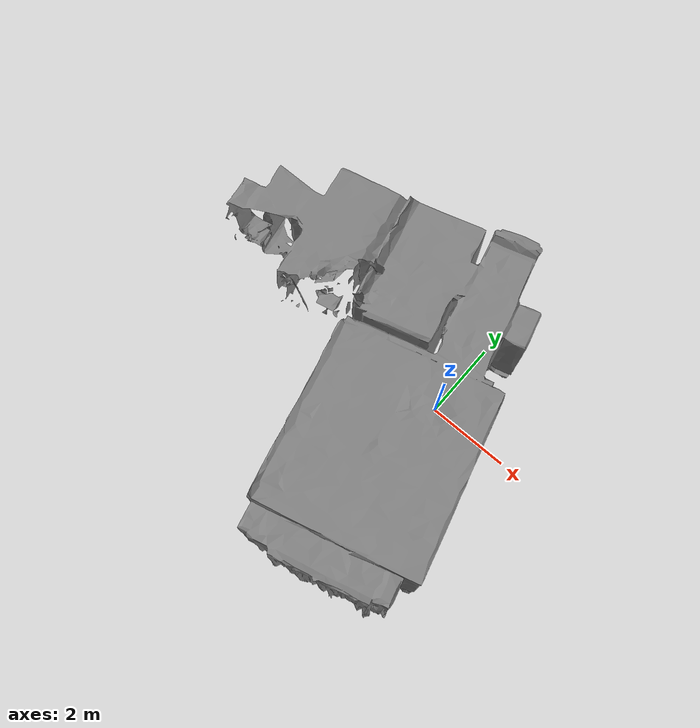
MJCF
<mujoco model="mesh_raw_prune_flat_sim">
  <option gravity="0 0 -9.81" />
  <compiler meshdir="../meshes" texturedir="../meshes/" />
  <asset>
    <mesh name="mesh" file="object/mesh/mesh.obj" />
    <mesh name="mesh_raw_prune_part_0" file="object/mesh_raw_prune/part_0.obj" />
    <mesh name="mesh_raw_prune_part_1" file="object/mesh_raw_prune/part_1.obj" />
    <mesh name="mesh_raw_prune_part_2" file="object/mesh_raw_prune/part_2.obj" />
    <mesh name="mesh_raw_prune_part_3" file="object/mesh_raw_prune/part_3.obj" />
    <mesh name="mesh_raw_prune_part_4" file="object/mesh_raw_prune/part_4.obj" />
    <mesh name="mesh_raw_prune_part_5" file="object/mesh_raw_prune/part_5.obj" />
    <mesh name="mesh_raw_prune_part_6" file="object/mesh_raw_prune/part_6.obj" />
    <mesh name="mesh_raw_prune_part_7" file="object/mesh_raw_prune/part_7.obj" />
    <mesh name="mesh_raw_prune_part_8" file="object/mesh_raw_prune/part_8.obj" />
    <mesh name="mesh_raw_prune_part_9" file="object/mesh_raw_prune/part_9.obj" />
    <mesh name="mesh_raw_prune_part_10" file="object/mesh_raw_prune/part_10.obj" />
    <mesh name="mesh_raw_prune_part_11" file="object/mesh_raw_prune/part_11.obj" />
    <mesh name="mesh_raw_prune_part_12" file="object/mesh_raw_prune/part_12.obj" />
    <mesh name="mesh_raw_prune_part_13" file="object/mesh_raw_prune/part_13.obj" />
    <mesh name="mesh_raw_prune_part_14" file="object/mesh_raw_prune/part_14.obj" />
    <mesh name="mesh_raw_prune_part_15" file="object/mesh_raw_prune/part_15.obj" />
    <mesh name="mesh_raw_prune_part_16" file="object/mesh_raw_prune/part_16.obj" />
    <mesh name="mesh_raw_prune_part_17" file="object/mesh_raw_prune/part_17.obj" />
    <mesh name="mesh_raw_prune_part_18" file="object/mesh_raw_prune/part_18.obj" />
    <mesh name="mesh_raw_prune_part_19" file="object/mesh_raw_prune/part_19.obj" />
    <mesh name="mesh_raw_prune_part_20" file="object/mesh_raw_prune/part_20.obj" />
    <mesh name="mesh_raw_prune_part_21" file="object/mesh_raw_prune/part_21.obj" />
    <mesh name="mesh_raw_prune_part_22" file="object/mesh_raw_prune/part_22.obj" />
    <mesh name="mesh_raw_prune_part_23" file="object/mesh_raw_prune/part_23.obj" />
    <mesh name="mesh_raw_prune_part_24" file="object/mesh_raw_prune/part_24.obj" />
    <mesh name="mesh_raw_prune_part_25" file="object/mesh_raw_prune/part_25.obj" />
    <mesh name="mesh_raw_prune_part_26" file="object/mesh_raw_prune/part_26.obj" />
    <mesh name="mesh_raw_prune_part_27" file="object/mesh_raw_prune/part_27.obj" />
    <mesh name="mesh_raw_prune_part_28" file="object/mesh_raw_prune/part_28.obj" />
    <mesh name="mesh_raw_prune_part_29" file="object/mesh_raw_prune/part_29.obj" />
    <mesh name="mesh_raw_prune_part_30" file="object/mesh_raw_prune/part_30.obj" />
    <mesh name="mesh_raw_prune_part_31" file="object/mesh_raw_prune/part_31.obj" />
    <mesh name="mesh_raw_prune_part_32" file="object/mesh_raw_prune/part_32.obj" />
    <mesh name="mesh_raw_prune_part_33" file="object/mesh_raw_prune/part_33.obj" />
    <mesh name="mesh_raw_prune_part_34" file="object/mesh_raw_prune/part_34.obj" />
    <mesh name="mesh_raw_prune_part_35" file="object/mesh_raw_prune/part_35.obj" />
    <mesh name="mesh_raw_prune_part_36" file="object/mesh_raw_prune/part_36.obj" />
    <mesh name="mesh_raw_prune_part_37" file="object/mesh_raw_prune/part_37.obj" />
    <mesh name="mesh_raw_prune_part_38" file="object/mesh_raw_prune/part_38.obj" />
    <mesh name="mesh_raw_prune_part_39" file="object/mesh_raw_prune/part_39.obj" />
    <mesh name="mesh_raw_prune_part_40" file="object/mesh_raw_prune/part_40.obj" />
    <mesh name="mesh_raw_prune_part_41" file="object/mesh_raw_prune/part_41.obj" />
    <mesh name="mesh_raw_prune_part_42" file="object/mesh_raw_prune/part_42.obj" />
    <mesh name="mesh_raw_prune_part_43" file="object/mesh_raw_prune/part_43.obj" />
    <mesh name="mesh_raw_prune_part_44" file="object/mesh_raw_prune/part_44.obj" />
    <mesh name="mesh_raw_prune_part_45" file="object/mesh_raw_prune/part_45.obj" />
    <mesh name="mesh_raw_prune_part_46" file="object/mesh_raw_prune/part_46.obj" />
    <mesh name="mesh_raw_prune_part_47" file="object/mesh_raw_prune/part_47.obj" />
    <mesh name="mesh_raw_prune_part_48" file="object/mesh_raw_prune/part_48.obj" />
    <mesh name="mesh_raw_prune_part_49" file="object/mesh_raw_prune/part_49.obj" />
    <mesh name="mesh_raw_prune_part_50" file="object/mesh_raw_prune/part_50.obj" />
    <mesh name="mesh_raw_prune_part_51" file="object/mesh_raw_prune/part_51.obj" />
    <mesh name="mesh_raw_prune_part_52" file="object/mesh_raw_prune/part_52.obj" />
    <mesh name="mesh_raw_prune_part_53" file="object/mesh_raw_prune/part_53.obj" />
    <mesh name="mesh_raw_prune_part_54" file="object/mesh_raw_prune/part_54.obj" />
    <mesh name="mesh_raw_prune_part_55" file="object/mesh_raw_prune/part_55.obj" />
    <mesh name="mesh_raw_prune_part_56" file="object/mesh_raw_prune/part_56.obj" />
    <mesh name="mesh_raw_prune_part_57" file="object/mesh_raw_prune/part_57.obj" />
    <mesh name="mesh_raw_prune_part_58" file="object/mesh_raw_prune/part_58.obj" />
    <mesh name="mesh_raw_prune_part_59" file="object/mesh_raw_prune/part_59.obj" />
    <mesh name="mesh_raw_prune_part_60" file="object/mesh_raw_prune/part_60.obj" />
    <mesh name="mesh_raw_prune_part_61" file="object/mesh_raw_prune/part_61.obj" />
    <mesh name="mesh_raw_prune_part_62" file="object/mesh_raw_prune/part_62.obj" />
    <mesh name="mesh_raw_prune_part_63" file="object/mesh_raw_prune/part_63.obj" />
    <mesh name="mesh_raw_prune_part_64" file="object/mesh_raw_prune/part_64.obj" />
    <mesh name="mesh_raw_prune_part_65" file="object/mesh_raw_prune/part_65.obj" />
    <mesh name="mesh_raw_prune_part_66" file="object/mesh_raw_prune/part_66.obj" />
    <mesh name="mesh_raw_prune_part_67" file="object/mesh_raw_prune/part_67.obj" />
    <mesh name="mesh_raw_prune_part_68" file="object/mesh_raw_prune/part_68.obj" />
    <mesh name="mesh_raw_prune_part_69" file="object/mesh_raw_prune/part_69.obj" />
    <mesh name="mesh_raw_prune_part_70" file="object/mesh_raw_prune/part_70.obj" />
    <mesh name="mesh_raw_prune_part_71" file="object/mesh_raw_prune/part_71.obj" />
    <mesh name="mesh_raw_prune_part_72" file="object/mesh_raw_prune/part_72.obj" />
    <mesh name="mesh_raw_prune_part_73" file="object/mesh_raw_prune/part_73.obj" />
    <mesh name="mesh_raw_prune_part_74" file="object/mesh_raw_prune/part_74.obj" />
    <mesh name="mesh_raw_prune_part_75" file="object/mesh_raw_prune/part_75.obj" />
    <mesh name="mesh_raw_prune_part_76" file="object/mesh_raw_prune/part_76.obj" />
    <mesh name="mesh_raw_prune_part_77" file="object/mesh_raw_prune/part_77.obj" />
    <mesh name="mesh_raw_prune_part_78" file="object/mesh_raw_prune/part_78.obj" />
    <mesh name="mesh_raw_prune_part_79" file="object/mesh_raw_prune/part_79.obj" />
    <mesh name="mesh_raw_prune_part_80" file="object/mesh_raw_prune/part_80.obj" />
    <mesh name="mesh_raw_prune_part_81" file="object/mesh_raw_prune/part_81.obj" />
    <mesh name="mesh_raw_prune_part_82" file="object/mesh_raw_prune/part_82.obj" />
    <mesh name="mesh_raw_prune_part_83" file="object/mesh_raw_prune/part_83.obj" />
    <mesh name="mesh_raw_prune_part_84" file="object/mesh_raw_prune/part_84.obj" />
    <mesh name="mesh_raw_prune_part_85" file="object/mesh_raw_prune/part_85.obj" />
    <mesh name="mesh_raw_prune_part_86" file="object/mesh_raw_prune/part_86.obj" />
    <mesh name="mesh_raw_prune_part_87" file="object/mesh_raw_prune/part_87.obj" />
    <mesh name="mesh_raw_prune_part_88" file="object/mesh_raw_prune/part_88.obj" />
    <mesh name="mesh_raw_prune_part_89" file="object/mesh_raw_prune/part_89.obj" />
    <mesh name="mesh_raw_prune_part_90" file="object/mesh_raw_prune/part_90.obj" />
    <mesh name="mesh_raw_prune_part_91" file="object/mesh_raw_prune/part_91.obj" />
    <mesh name="mesh_raw_prune_part_92" file="object/mesh_raw_prune/part_92.obj" />
    <mesh name="mesh_raw_prune_part_93" file="object/mesh_raw_prune/part_93.obj" />
    <mesh name="mesh_raw_prune_part_94" file="object/mesh_raw_prune/part_94.obj" />
    <mesh name="mesh_raw_prune_part_95" file="object/mesh_raw_prune/part_95.obj" />
    <mesh name="mesh_raw_prune_part_96" file="object/mesh_raw_prune/part_96.obj" />
    <mesh name="mesh_raw_prune_part_97" file="object/mesh_raw_prune/part_97.obj" />
    <mesh name="mesh_raw_prune_part_98" file="object/mesh_raw_prune/part_98.obj" />
    <mesh name="mesh_raw_prune_part_99" file="object/mesh_raw_prune/part_99.obj" />
    <mesh name="mesh_raw_prune_part_100" file="object/mesh_raw_prune/part_100.obj" />
    <mesh name="mesh_raw_prune_part_101" file="object/mesh_raw_prune/part_101.obj" />
    <mesh name="mesh_raw_prune_part_102" file="object/mesh_raw_prune/part_102.obj" />
    <mesh name="mesh_raw_prune_part_103" file="object/mesh_raw_prune/part_103.obj" />
    <mesh name="mesh_raw_prune_part_104" file="object/mesh_raw_prune/part_104.obj" />
    <mesh name="mesh_raw_prune_part_105" file="object/mesh_raw_prune/part_105.obj" />
    <mesh name="mesh_raw_prune_part_106" file="object/mesh_raw_prune/part_106.obj" />
    <mesh name="mesh_raw_prune_part_107" file="object/mesh_raw_prune/part_107.obj" />
    <mesh name="mesh_raw_prune_part_108" file="object/mesh_raw_prune/part_108.obj" />
    <mesh name="mesh_raw_prune_part_109" file="object/mesh_raw_prune/part_109.obj" />
    <mesh name="mesh_raw_prune_part_110" file="object/mesh_raw_prune/part_110.obj" />
    <mesh name="mesh_raw_prune_part_111" file="object/mesh_raw_prune/part_111.obj" />
    <mesh name="mesh_raw_prune_part_112" file="object/mesh_raw_prune/part_112.obj" />
    <mesh name="mesh_raw_prune_part_113" file="object/mesh_raw_prune/part_113.obj" />
    <mesh name="mesh_raw_prune_part_114" file="object/mesh_raw_prune/part_114.obj" />
    <mesh name="mesh_raw_prune_part_115" file="object/mesh_raw_prune/part_115.obj" />
    <mesh name="mesh_raw_prune_part_116" file="object/mesh_raw_prune/part_116.obj" />
    <mesh name="mesh_raw_prune_part_117" file="object/mesh_raw_prune/part_117.obj" />
    <mesh name="mesh_raw_prune_part_118" file="object/mesh_raw_prune/part_118.obj" />
    <mesh name="mesh_raw_prune_part_119" file="object/mesh_raw_prune/part_119.obj" />
    <mesh name="mesh_raw_prune_part_120" file="object/mesh_raw_prune/part_120.obj" />
    <mesh name="mesh_raw_prune_part_121" file="object/mesh_raw_prune/part_121.obj" />
    <mesh name="mesh_raw_prune_part_122" file="object/mesh_raw_prune/part_122.obj" />
    <mesh name="mesh_raw_prune_part_123" file="object/mesh_raw_prune/part_123.obj" />
    <mesh name="mesh_raw_prune_part_124" file="object/mesh_raw_prune/part_124.obj" />
    <mesh name="mesh_raw_prune_part_125" file="object/mesh_raw_prune/part_125.obj" />
    <mesh name="mesh_raw_prune_part_126" file="object/mesh_raw_prune/part_126.obj" />
    <mesh name="mesh_raw_prune_part_127" file="object/mesh_raw_prune/part_127.obj" />
    <mesh name="mesh_raw_prune_part_128" file="object/mesh_raw_prune/part_128.obj" />
    <mesh name="mesh_raw_prune_part_129" file="object/mesh_raw_prune/part_129.obj" />
    <mesh name="mesh_raw_prune_part_130" file="object/mesh_raw_prune/part_130.obj" />
    <mesh name="mesh_raw_prune_part_131" file="object/mesh_raw_prune/part_131.obj" />
    <mesh name="mesh_raw_prune_part_132" file="object/mesh_raw_prune/part_132.obj" />
    <mesh name="mesh_raw_prune_part_133" file="object/mesh_raw_prune/part_133.obj" />
    <mesh name="mesh_raw_prune_part_134" file="object/mesh_raw_prune/part_134.obj" />
    <mesh name="mesh_raw_prune_part_135" file="object/mesh_raw_prune/part_135.obj" />
    <mesh name="mesh_raw_prune_part_136" file="object/mesh_raw_prune/part_136.obj" />
    <mesh name="mesh_raw_prune_part_137" file="object/mesh_raw_prune/part_137.obj" />
    <mesh name="mesh_raw_prune_part_138" file="object/mesh_raw_prune/part_138.obj" />
    <mesh name="mesh_raw_prune_part_139" file="object/mesh_raw_prune/part_139.obj" />
    <mesh name="mesh_raw_prune_part_140" file="object/mesh_raw_prune/part_140.obj" />
    <mesh name="mesh_raw_prune_part_141" file="object/mesh_raw_prune/part_141.obj" />
    <mesh name="mesh_raw_prune_part_142" file="object/mesh_raw_prune/part_142.obj" />
    <mesh name="mesh_raw_prune_part_143" file="object/mesh_raw_prune/part_143.obj" />
    <mesh name="mesh_raw_prune_part_144" file="object/mesh_raw_prune/part_144.obj" />
    <mesh name="mesh_raw_prune_part_145" file="object/mesh_raw_prune/part_145.obj" />
    <mesh name="mesh_raw_prune_part_146" file="object/mesh_raw_prune/part_146.obj" />
    <mesh name="mesh_raw_prune_part_147" file="object/mesh_raw_prune/part_147.obj" />
    <mesh name="mesh_raw_prune_part_148" file="object/mesh_raw_prune/part_148.obj" />
    <mesh name="mesh_raw_prune_part_149" file="object/mesh_raw_prune/part_149.obj" />
    <mesh name="mesh_raw_prune_part_150" file="object/mesh_raw_prune/part_150.obj" />
    <mesh name="mesh_raw_prune_part_151" file="object/mesh_raw_prune/part_151.obj" />
    <mesh name="mesh_raw_prune_part_152" file="object/mesh_raw_prune/part_152.obj" />
    <mesh name="mesh_raw_prune_part_153" file="object/mesh_raw_prune/part_153.obj" />
    <mesh name="mesh_raw_prune_part_154" file="object/mesh_raw_prune/part_154.obj" />
    <mesh name="mesh_raw_prune_part_155" file="object/mesh_raw_prune/part_155.obj" />
    <mesh name="mesh_raw_prune_part_156" file="object/mesh_raw_prune/part_156.obj" />
    <mesh name="mesh_raw_prune_part_157" file="object/mesh_raw_prune/part_157.obj" />
    <mesh name="mesh_raw_prune_part_158" file="object/mesh_raw_prune/part_158.obj" />
    <mesh name="mesh_raw_prune_part_159" file="object/mesh_raw_prune/part_159.obj" />
    <mesh name="mesh_raw_prune_part_160" file="object/mesh_raw_prune/part_160.obj" />
    <mesh name="mesh_raw_prune_part_161" file="object/mesh_raw_prune/part_161.obj" />
    <mesh name="mesh_raw_prune_part_162" file="object/mesh_raw_prune/part_162.obj" />
    <mesh name="mesh_raw_prune_part_163" file="object/mesh_raw_prune/part_163.obj" />
    <mesh name="mesh_raw_prune_part_164" file="object/mesh_raw_prune/part_164.obj" />
    <mesh name="mesh_raw_prune_part_165" file="object/mesh_raw_prune/part_165.obj" />
    <mesh name="mesh_raw_prune_part_166" file="object/mesh_raw_prune/part_166.obj" />
    <mesh name="mesh_raw_prune_part_167" file="object/mesh_raw_prune/part_167.obj" />
    <mesh name="mesh_raw_prune_part_168" file="object/mesh_raw_prune/part_168.obj" />
    <mesh name="mesh_raw_prune_part_169" file="object/mesh_raw_prune/part_169.obj" />
    <mesh name="mesh_raw_prune_part_170" file="object/mesh_raw_prune/part_170.obj" />
    <mesh name="mesh_raw_prune_part_171" file="object/mesh_raw_prune/part_171.obj" />
    <mesh name="mesh_raw_prune_part_172" file="object/mesh_raw_prune/part_172.obj" />
    <mesh name="mesh_raw_prune_part_173" file="object/mesh_raw_prune/part_173.obj" />
    <mesh name="mesh_raw_prune_part_174" file="object/mesh_raw_prune/part_174.obj" />
    <mesh name="mesh_raw_prune_part_175" file="object/mesh_raw_prune/part_175.obj" />
    <mesh name="mesh_raw_prune_part_176" file="object/mesh_raw_prune/part_176.obj" />
    <mesh name="mesh_raw_prune_part_177" file="object/mesh_raw_prune/part_177.obj" />
    <mesh name="mesh_raw_prune_part_178" file="object/mesh_raw_prune/part_178.obj" />
    <mesh name="mesh_raw_prune_part_179" file="object/mesh_raw_prune/part_179.obj" />
    <mesh name="mesh_raw_prune_part_180" file="object/mesh_raw_prune/part_180.obj" />
    <mesh name="mesh_raw_prune_part_181" file="object/mesh_raw_prune/part_181.obj" />
    <mesh name="mesh_raw_prune_part_182" file="object/mesh_raw_prune/part_182.obj" />
    <mesh name="mesh_raw_prune_part_183" file="object/mesh_raw_prune/part_183.obj" />
    <mesh name="mesh_raw_prune_part_184" file="object/mesh_raw_prune/part_184.obj" />
    <mesh name="mesh_raw_prune_part_185" file="object/mesh_raw_prune/part_185.obj" />
    <mesh name="mesh_raw_prune_part_186" file="object/mesh_raw_prune/part_186.obj" />
    <mesh name="mesh_raw_prune_part_187" file="object/mesh_raw_prune/part_187.obj" />
    <mesh name="mesh_raw_prune_part_188" file="object/mesh_raw_prune/part_188.obj" />
    <mesh name="mesh_raw_prune_part_189" file="object/mesh_raw_prune/part_189.obj" />
    <mesh name="mesh_raw_prune_part_190" file="object/mesh_raw_prune/part_190.obj" />
    <mesh name="mesh_raw_prune_part_191" file="object/mesh_raw_prune/part_191.obj" />
    <mesh name="mesh_raw_prune_part_192" file="object/mesh_raw_prune/part_192.obj" />
    <mesh name="mesh_raw_prune_part_193" file="object/mesh_raw_prune/part_193.obj" />
    <mesh name="mesh_raw_prune_part_194" file="object/mesh_raw_prune/part_194.obj" />
    <mesh name="mesh_raw_prune_part_195" file="object/mesh_raw_prune/part_195.obj" />
    <mesh name="mesh_raw_prune_part_196" file="object/mesh_raw_prune/part_196.obj" />
    <mesh name="mesh_raw_prune_part_197" file="object/mesh_raw_prune/part_197.obj" />
    <mesh name="mesh_raw_prune_part_198" file="object/mesh_raw_prune/part_198.obj" />
    <mesh name="mesh_raw_prune_part_199" file="object/mesh_raw_prune/part_199.obj" />
    <mesh name="mesh_raw_prune_part_200" file="object/mesh_raw_prune/part_200.obj" />
    <mesh name="mesh_raw_prune_part_201" file="object/mesh_raw_prune/part_201.obj" />
    <mesh name="mesh_raw_prune_part_202" file="object/mesh_raw_prune/part_202.obj" />
    <mesh name="mesh_raw_prune_part_203" file="object/mesh_raw_prune/part_203.obj" />
    <mesh name="mesh_raw_prune_part_204" file="object/mesh_raw_prune/part_204.obj" />
    <mesh name="mesh_raw_prune_part_205" file="object/mesh_raw_prune/part_205.obj" />
    <mesh name="mesh_raw_prune_part_206" file="object/mesh_raw_prune/part_206.obj" />
    <mesh name="mesh_raw_prune_part_207" file="object/mesh_raw_prune/part_207.obj" />
    <mesh name="mesh_raw_prune_part_208" file="object/mesh_raw_prune/part_208.obj" />
    <mesh name="mesh_raw_prune_part_209" file="object/mesh_raw_prune/part_209.obj" />
    <mesh name="mesh_raw_prune_part_210" file="object/mesh_raw_prune/part_210.obj" />
    <mesh name="mesh_raw_prune_part_211" file="object/mesh_raw_prune/part_211.obj" />
    <mesh name="mesh_raw_prune_part_212" file="object/mesh_raw_prune/part_212.obj" />
    <mesh name="mesh_raw_prune_part_213" file="object/mesh_raw_prune/part_213.obj" />
    <mesh name="mesh_raw_prune_part_214" file="object/mesh_raw_prune/part_214.obj" />
    <mesh name="mesh_raw_prune_part_215" file="object/mesh_raw_prune/part_215.obj" />
    <mesh name="mesh_raw_prune_part_216" file="object/mesh_raw_prune/part_216.obj" />
    <mesh name="mesh_raw_prune_part_217" file="object/mesh_raw_prune/part_217.obj" />
    <mesh name="mesh_raw_prune_part_218" file="object/mesh_raw_prune/part_218.obj" />
    <mesh name="mesh_raw_prune_part_219" file="object/mesh_raw_prune/part_219.obj" />
    <mesh name="mesh_raw_prune_part_220" file="object/mesh_raw_prune/part_220.obj" />
    <mesh name="mesh_raw_prune_part_221" file="object/mesh_raw_prune/part_221.obj" />
    <mesh name="mesh_raw_prune_part_222" file="object/mesh_raw_prune/part_222.obj" />
    <mesh name="mesh_raw_prune_part_223" file="object/mesh_raw_prune/part_223.obj" />
    <mesh name="mesh_raw_prune_part_224" file="object/mesh_raw_prune/part_224.obj" />
    <mesh name="mesh_raw_prune_part_225" file="object/mesh_raw_prune/part_225.obj" />
    <mesh name="mesh_raw_prune_part_226" file="object/mesh_raw_prune/part_226.obj" />
    <mesh name="mesh_raw_prune_part_227" file="object/mesh_raw_prune/part_227.obj" />
    <mesh name="mesh_raw_prune_part_228" file="object/mesh_raw_prune/part_228.obj" />
    <mesh name="mesh_raw_prune_part_229" file="object/mesh_raw_prune/part_229.obj" />
    <mesh name="mesh_raw_prune_part_230" file="object/mesh_raw_prune/part_230.obj" />
    <mesh name="mesh_raw_prune_part_231" file="object/mesh_raw_prune/part_231.obj" />
    <mesh name="mesh_raw_prune_part_232" file="object/mesh_raw_prune/part_232.obj" />
    <mesh name="mesh_raw_prune_part_233" file="object/mesh_raw_prune/part_233.obj" />
    <mesh name="mesh_raw_prune_part_234" file="object/mesh_raw_prune/part_234.obj" />
    <mesh name="mesh_raw_prune_part_235" file="object/mesh_raw_prune/part_235.obj" />
    <mesh name="mesh_raw_prune_part_236" file="object/mesh_raw_prune/part_236.obj" />
    <mesh name="mesh_raw_prune_part_237" file="object/mesh_raw_prune/part_237.obj" />
    <mesh name="mesh_raw_prune_part_238" file="object/mesh_raw_prune/part_238.obj" />
    <mesh name="mesh_raw_prune_part_239" file="object/mesh_raw_prune/part_239.obj" />
    <mesh name="mesh_raw_prune_part_240" file="object/mesh_raw_prune/part_240.obj" />
    <mesh name="mesh_raw_prune_part_241" file="object/mesh_raw_prune/part_241.obj" />
    <mesh name="mesh_raw_prune_part_242" file="object/mesh_raw_prune/part_242.obj" />
    <mesh name="mesh_raw_prune_part_243" file="object/mesh_raw_prune/part_243.obj" />
    <mesh name="mesh_raw_prune_part_244" file="object/mesh_raw_prune/part_244.obj" />
    <mesh name="mesh_raw_prune_part_245" file="object/mesh_raw_prune/part_245.obj" />
    <mesh name="mesh_raw_prune_part_246" file="object/mesh_raw_prune/part_246.obj" />
    <mesh name="mesh_raw_prune_part_247" file="object/mesh_raw_prune/part_247.obj" />
    <mesh name="mesh_raw_prune_part_248" file="object/mesh_raw_prune/part_248.obj" />
    <mesh name="mesh_raw_prune_part_249" file="object/mesh_raw_prune/part_249.obj" />
    <mesh name="mesh_raw_prune_part_250" file="object/mesh_raw_prune/part_250.obj" />
    <mesh name="mesh_raw_prune_part_251" file="object/mesh_raw_prune/part_251.obj" />
    <mesh name="mesh_raw_prune_part_252" file="object/mesh_raw_prune/part_252.obj" />
    <mesh name="mesh_raw_prune_part_253" file="object/mesh_raw_prune/part_253.obj" />
    <mesh name="mesh_raw_prune_part_254" file="object/mesh_raw_prune/part_254.obj" />
    <mesh name="mesh_raw_prune_part_255" file="object/mesh_raw_prune/part_255.obj" />
    <mesh name="mesh_raw_prune_part_256" file="object/mesh_raw_prune/part_256.obj" />
    <mesh name="mesh_raw_prune_part_257" file="object/mesh_raw_prune/part_257.obj" />
    <mesh name="mesh_raw_prune_part_258" file="object/mesh_raw_prune/part_258.obj" />
    <mesh name="mesh_raw_prune_part_259" file="object/mesh_raw_prune/part_259.obj" />
    <mesh name="mesh_raw_prune_part_260" file="object/mesh_raw_prune/part_260.obj" />
    <mesh name="mesh_raw_prune_part_261" file="object/mesh_raw_prune/part_261.obj" />
    <mesh name="mesh_raw_prune_part_262" file="object/mesh_raw_prune/part_262.obj" />
    <mesh name="mesh_raw_prune_part_263" file="object/mesh_raw_prune/part_263.obj" />
    <mesh name="mesh_raw_prune_part_264" file="object/mesh_raw_prune/part_264.obj" />
    <mesh name="mesh_raw_prune_part_265" file="object/mesh_raw_prune/part_265.obj" />
    <mesh name="mesh_raw_prune_part_266" file="object/mesh_raw_prune/part_266.obj" />
    <mesh name="mesh_raw_prune_part_267" file="object/mesh_raw_prune/part_267.obj" />
    <mesh name="mesh_raw_prune_part_268" file="object/mesh_raw_prune/part_268.obj" />
    <mesh name="mesh_raw_prune_part_269" file="object/mesh_raw_prune/part_269.obj" />
    <mesh name="mesh_raw_prune_part_270" file="object/mesh_raw_prune/part_270.obj" />
    <mesh name="mesh_raw_prune_part_271" file="object/mesh_raw_prune/part_271.obj" />
    <mesh name="mesh_raw_prune_part_272" file="object/mesh_raw_prune/part_272.obj" />
    <mesh name="mesh_raw_prune_part_273" file="object/mesh_raw_prune/part_273.obj" />
    <mesh name="mesh_raw_prune_part_274" file="object/mesh_raw_prune/part_274.obj" />
    <mesh name="mesh_raw_prune_part_275" file="object/mesh_raw_prune/part_275.obj" />
    <mesh name="mesh_raw_prune_part_276" file="object/mesh_raw_prune/part_276.obj" />
    <mesh name="mesh_raw_prune_part_277" file="object/mesh_raw_prune/part_277.obj" />
    <mesh name="mesh_raw_prune_part_278" file="object/mesh_raw_prune/part_278.obj" />
    <mesh name="mesh_raw_prune_part_279" file="object/mesh_raw_prune/part_279.obj" />
    <mesh name="mesh_raw_prune_part_280" file="object/mesh_raw_prune/part_280.obj" />
    <mesh name="mesh_raw_prune_part_281" file="object/mesh_raw_prune/part_281.obj" />
    <mesh name="mesh_raw_prune_part_282" file="object/mesh_raw_prune/part_282.obj" />
    <mesh name="mesh_raw_prune_part_283" file="object/mesh_raw_prune/part_283.obj" />
    <mesh name="mesh_raw_prune_part_284" file="object/mesh_raw_prune/part_284.obj" />
    <mesh name="mesh_raw_prune_part_285" file="object/mesh_raw_prune/part_285.obj" />
    <mesh name="mesh_raw_prune_part_286" file="object/mesh_raw_prune/part_286.obj" />
    <mesh name="mesh_raw_prune_part_287" file="object/mesh_raw_prune/part_287.obj" />
    <mesh name="mesh_raw_prune_part_288" file="object/mesh_raw_prune/part_288.obj" />
    <mesh name="mesh_raw_prune_part_289" file="object/mesh_raw_prune/part_289.obj" />
    <mesh name="mesh_raw_prune_part_290" file="object/mesh_raw_prune/part_290.obj" />
    <mesh name="mesh_raw_prune_part_291" file="object/mesh_raw_prune/part_291.obj" />
    <mesh name="mesh_raw_prune_part_292" file="object/mesh_raw_prune/part_292.obj" />
    <mesh name="mesh_raw_prune_part_293" file="object/mesh_raw_prune/part_293.obj" />
    <mesh name="mesh_raw_prune_part_294" file="object/mesh_raw_prune/part_294.obj" />
    <mesh name="mesh_raw_prune_part_295" file="object/mesh_raw_prune/part_295.obj" />
    <mesh name="mesh_raw_prune_part_296" file="object/mesh_raw_prune/part_296.obj" />
    <mesh name="mesh_raw_prune_part_297" file="object/mesh_raw_prune/part_297.obj" />
    <mesh name="mesh_raw_prune_part_298" file="object/mesh_raw_prune/part_298.obj" />
    <mesh name="mesh_raw_prune_part_299" file="object/mesh_raw_prune/part_299.obj" />
    <mesh name="mesh_raw_prune_part_300" file="object/mesh_raw_prune/part_300.obj" />
    <mesh name="mesh_raw_prune_part_301" file="object/mesh_raw_prune/part_301.obj" />
    <mesh name="mesh_raw_prune_part_302" file="object/mesh_raw_prune/part_302.obj" />
    <mesh name="mesh_raw_prune_part_303" file="object/mesh_raw_prune/part_303.obj" />
    <mesh name="mesh_raw_prune_part_304" file="object/mesh_raw_prune/part_304.obj" />
    <mesh name="mesh_raw_prune_part_305" file="object/mesh_raw_prune/part_305.obj" />
    <mesh name="mesh_raw_prune_part_306" file="object/mesh_raw_prune/part_306.obj" />
    <mesh name="mesh_raw_prune_part_307" file="object/mesh_raw_prune/part_307.obj" />
    <mesh name="mesh_raw_prune_part_308" file="object/mesh_raw_prune/part_308.obj" />
    <mesh name="mesh_raw_prune_part_309" file="object/mesh_raw_prune/part_309.obj" />
    <mesh name="mesh_raw_prune_part_310" file="object/mesh_raw_prune/part_310.obj" />
    <mesh name="mesh_raw_prune_part_311" file="object/mesh_raw_prune/part_311.obj" />
    <mesh name="mesh_raw_prune_part_312" file="object/mesh_raw_prune/part_312.obj" />
    <mesh name="mesh_raw_prune_part_313" file="object/mesh_raw_prune/part_313.obj" />
    <mesh name="mesh_raw_prune_part_314" file="object/mesh_raw_prune/part_314.obj" />
    <mesh name="mesh_raw_prune_part_315" file="object/mesh_raw_prune/part_315.obj" />
    <mesh name="mesh_raw_prune_part_316" file="object/mesh_raw_prune/part_316.obj" />
    <mesh name="mesh_raw_prune_part_317" file="object/mesh_raw_prune/part_317.obj" />
    <mesh name="mesh_raw_prune_part_318" file="object/mesh_raw_prune/part_318.obj" />
    <mesh name="mesh_raw_prune_part_319" file="object/mesh_raw_prune/part_319.obj" />
    <mesh name="mesh_raw_prune_part_320" file="object/mesh_raw_prune/part_320.obj" />
    <mesh name="mesh_raw_prune_part_321" file="object/mesh_raw_prune/part_321.obj" />
    <mesh name="mesh_raw_prune_part_322" file="object/mesh_raw_prune/part_322.obj" />
    <mesh name="mesh_raw_prune_part_323" file="object/mesh_raw_prune/part_323.obj" />
    <mesh name="mesh_raw_prune_part_324" file="object/mesh_raw_prune/part_324.obj" />
    <mesh name="mesh_raw_prune_part_325" file="object/mesh_raw_prune/part_325.obj" />
    <mesh name="mesh_raw_prune_part_326" file="object/mesh_raw_prune/part_326.obj" />
    <mesh name="mesh_raw_prune_part_327" file="object/mesh_raw_prune/part_327.obj" />
    <mesh name="mesh_raw_prune_part_328" file="object/mesh_raw_prune/part_328.obj" />
    <mesh name="mesh_raw_prune_part_329" file="object/mesh_raw_prune/part_329.obj" />
    <mesh name="mesh_raw_prune_part_330" file="object/mesh_raw_prune/part_330.obj" />
    <mesh name="mesh_raw_prune_part_331" file="object/mesh_raw_prune/part_331.obj" />
    <mesh name="mesh_raw_prune_part_332" file="object/mesh_raw_prune/part_332.obj" />
    <mesh name="mesh_raw_prune_part_333" file="object/mesh_raw_prune/part_333.obj" />
    <mesh name="mesh_raw_prune_part_334" file="object/mesh_raw_prune/part_334.obj" />
    <mesh name="mesh_raw_prune_part_335" file="object/mesh_raw_prune/part_335.obj" />
    <mesh name="mesh_raw_prune_part_336" file="object/mesh_raw_prune/part_336.obj" />
    <mesh name="mesh_raw_prune_part_337" file="object/mesh_raw_prune/part_337.obj" />
    <mesh name="mesh_raw_prune_part_338" file="object/mesh_raw_prune/part_338.obj" />
    <mesh name="mesh_raw_prune_part_339" file="object/mesh_raw_prune/part_339.obj" />
    <mesh name="mesh_raw_prune_part_340" file="object/mesh_raw_prune/part_340.obj" />
    <mesh name="mesh_raw_prune_part_341" file="object/mesh_raw_prune/part_341.obj" />
    <mesh name="mesh_raw_prune_part_342" file="object/mesh_raw_prune/part_342.obj" />
    <mesh name="mesh_raw_prune_part_343" file="object/mesh_raw_prune/part_343.obj" />
    <mesh name="mesh_raw_prune_part_344" file="object/mesh_raw_prune/part_344.obj" />
    <mesh name="mesh_raw_prune_part_345" file="object/mesh_raw_prune/part_345.obj" />
    <mesh name="mesh_raw_prune_part_346" file="object/mesh_raw_prune/part_346.obj" />
    <mesh name="mesh_raw_prune_part_347" file="object/mesh_raw_prune/part_347.obj" />
    <mesh name="mesh_raw_prune_part_348" file="object/mesh_raw_prune/part_348.obj" />
    <mesh name="mesh_raw_prune_part_349" file="object/mesh_raw_prune/part_349.obj" />
    <mesh name="mesh_raw_prune_part_350" file="object/mesh_raw_prune/part_350.obj" />
    <mesh name="mesh_raw_prune_part_351" file="object/mesh_raw_prune/part_351.obj" />
    <mesh name="mesh_raw_prune_part_352" file="object/mesh_raw_prune/part_352.obj" />
    <mesh name="mesh_raw_prune_part_353" file="object/mesh_raw_prune/part_353.obj" />
    <mesh name="mesh_raw_prune_part_354" file="object/mesh_raw_prune/part_354.obj" />
    <mesh name="mesh_raw_prune_part_355" file="object/mesh_raw_prune/part_355.obj" />
    <mesh name="mesh_raw_prune_part_356" file="object/mesh_raw_prune/part_356.obj" />
    <mesh name="mesh_raw_prune_part_357" file="object/mesh_raw_prune/part_357.obj" />
    <mesh name="mesh_raw_prune_part_358" file="object/mesh_raw_prune/part_358.obj" />
    <mesh name="mesh_raw_prune_part_359" file="object/mesh_raw_prune/part_359.obj" />
    <mesh name="mesh_raw_prune_part_360" file="object/mesh_raw_prune/part_360.obj" />
    <mesh name="mesh_raw_prune_part_361" file="object/mesh_raw_prune/part_361.obj" />
    <mesh name="mesh_raw_prune_part_362" file="object/mesh_raw_prune/part_362.obj" />
    <mesh name="mesh_raw_prune_part_363" file="object/mesh_raw_prune/part_363.obj" />
    <mesh name="mesh_raw_prune_part_364" file="object/mesh_raw_prune/part_364.obj" />
    <mesh name="mesh_raw_prune_part_365" file="object/mesh_raw_prune/part_365.obj" />
    <mesh name="mesh_raw_prune_part_366" file="object/mesh_raw_prune/part_366.obj" />
    <mesh name="mesh_raw_prune_part_367" file="object/mesh_raw_prune/part_367.obj" />
    <mesh name="mesh_raw_prune_part_368" file="object/mesh_raw_prune/part_368.obj" />
    <mesh name="mesh_raw_prune_part_369" file="object/mesh_raw_prune/part_369.obj" />
    <mesh name="mesh_raw_prune_part_370" file="object/mesh_raw_prune/part_370.obj" />
    <mesh name="mesh_raw_prune_part_371" file="object/mesh_raw_prune/part_371.obj" />
    <mesh name="mesh_raw_prune_part_372" file="object/mesh_raw_prune/part_372.obj" />
    <mesh name="mesh_raw_prune_part_373" file="object/mesh_raw_prune/part_373.obj" />
    <mesh name="mesh_raw_prune_part_374" file="object/mesh_raw_prune/part_374.obj" />
    <mesh name="mesh_raw_prune_part_375" file="object/mesh_raw_prune/part_375.obj" />
    <mesh name="mesh_raw_prune_part_376" file="object/mesh_raw_prune/part_376.obj" />
    <mesh name="mesh_raw_prune_part_377" file="object/mesh_raw_prune/part_377.obj" />
    <mesh name="mesh_raw_prune_part_378" file="object/mesh_raw_prune/part_378.obj" />
    <mesh name="mesh_raw_prune_part_379" file="object/mesh_raw_prune/part_379.obj" />
    <mesh name="mesh_raw_prune_part_380" file="object/mesh_raw_prune/part_380.obj" />
    <mesh name="mesh_raw_prune_part_381" file="object/mesh_raw_prune/part_381.obj" />
    <mesh name="mesh_raw_prune_part_382" file="object/mesh_raw_prune/part_382.obj" />
    <mesh name="mesh_raw_prune_part_383" file="object/mesh_raw_prune/part_383.obj" />
    <mesh name="mesh_raw_prune_part_384" file="object/mesh_raw_prune/part_384.obj" />
    <mesh name="mesh_raw_prune_part_385" file="object/mesh_raw_prune/part_385.obj" />
    <mesh name="mesh_raw_prune_part_386" file="object/mesh_raw_prune/part_386.obj" />
    <mesh name="mesh_raw_prune_part_387" file="object/mesh_raw_prune/part_387.obj" />
    <mesh name="mesh_raw_prune_part_388" file="object/mesh_raw_prune/part_388.obj" />
    <mesh name="mesh_raw_prune_part_389" file="object/mesh_raw_prune/part_389.obj" />
    <mesh name="mesh_raw_prune_part_390" file="object/mesh_raw_prune/part_390.obj" />
    <mesh name="mesh_raw_prune_part_391" file="object/mesh_raw_prune/part_391.obj" />
    <mesh name="mesh_raw_prune_part_392" file="object/mesh_raw_prune/part_392.obj" />
    <mesh name="mesh_raw_prune_part_393" file="object/mesh_raw_prune/part_393.obj" />
    <mesh name="mesh_raw_prune_part_394" file="object/mesh_raw_prune/part_394.obj" />
    <mesh name="mesh_raw_prune_part_395" file="object/mesh_raw_prune/part_395.obj" />
    <mesh name="mesh_raw_prune_part_396" file="object/mesh_raw_prune/part_396.obj" />
    <mesh name="mesh_raw_prune_part_397" file="object/mesh_raw_prune/part_397.obj" />
    <mesh name="mesh_raw_prune_part_398" file="object/mesh_raw_prune/part_398.obj" />
    <mesh name="mesh_raw_prune_part_399" file="object/mesh_raw_prune/part_399.obj" />
    <mesh name="mesh_raw_prune_part_400" file="object/mesh_raw_prune/part_400.obj" />
    <mesh name="mesh_raw_prune_part_401" file="object/mesh_raw_prune/part_401.obj" />
    <mesh name="mesh_raw_prune_part_402" file="object/mesh_raw_prune/part_402.obj" />
    <mesh name="mesh_raw_prune_part_403" file="object/mesh_raw_prune/part_403.obj" />
    <mesh name="mesh_raw_prune_part_404" file="object/mesh_raw_prune/part_404.obj" />
    <mesh name="mesh_raw_prune_part_405" file="object/mesh_raw_prune/part_405.obj" />
    <mesh name="mesh_raw_prune_part_406" file="object/mesh_raw_prune/part_406.obj" />
    <mesh name="mesh_raw_prune_part_407" file="object/mesh_raw_prune/part_407.obj" />
    <mesh name="mesh_raw_prune_part_408" file="object/mesh_raw_prune/part_408.obj" />
    <mesh name="mesh_raw_prune_part_409" file="object/mesh_raw_prune/part_409.obj" />
    <mesh name="mesh_raw_prune_part_410" file="object/mesh_raw_prune/part_410.obj" />
    <mesh name="mesh_raw_prune_part_411" file="object/mesh_raw_prune/part_411.obj" />
    <mesh name="mesh_raw_prune_part_412" file="object/mesh_raw_prune/part_412.obj" />
    <mesh name="mesh_raw_prune_part_413" file="object/mesh_raw_prune/part_413.obj" />
    <mesh name="mesh_raw_prune_part_414" file="object/mesh_raw_prune/part_414.obj" />
    <mesh name="mesh_raw_prune_part_415" file="object/mesh_raw_prune/part_415.obj" />
    <mesh name="mesh_raw_prune_part_416" file="object/mesh_raw_prune/part_416.obj" />
    <mesh name="mesh_raw_prune_part_417" file="object/mesh_raw_prune/part_417.obj" />
    <mesh name="mesh_raw_prune_part_418" file="object/mesh_raw_prune/part_418.obj" />
    <mesh name="mesh_raw_prune_part_419" file="object/mesh_raw_prune/part_419.obj" />
    <mesh name="mesh_raw_prune_part_420" file="object/mesh_raw_prune/part_420.obj" />
    <mesh name="mesh_raw_prune_part_421" file="object/mesh_raw_prune/part_421.obj" />
    <mesh name="mesh_raw_prune_part_422" file="object/mesh_raw_prune/part_422.obj" />
    <mesh name="mesh_raw_prune_part_423" file="object/mesh_raw_prune/part_423.obj" />
    <mesh name="mesh_raw_prune_part_424" file="object/mesh_raw_prune/part_424.obj" />
    <mesh name="mesh_raw_prune_part_425" file="object/mesh_raw_prune/part_425.obj" />
    <mesh name="mesh_raw_prune_part_426" file="object/mesh_raw_prune/part_426.obj" />
    <mesh name="mesh_raw_prune_part_427" file="object/mesh_raw_prune/part_427.obj" />
    <mesh name="mesh_raw_prune_part_428" file="object/mesh_raw_prune/part_428.obj" />
    <mesh name="mesh_raw_prune_part_429" file="object/mesh_raw_prune/part_429.obj" />
    <mesh name="mesh_raw_prune_part_430" file="object/mesh_raw_prune/part_430.obj" />
    <mesh name="mesh_raw_prune_part_431" file="object/mesh_raw_prune/part_431.obj" />
    <mesh name="mesh_raw_prune_part_432" file="object/mesh_raw_prune/part_432.obj" />
    <mesh name="mesh_raw_prune_part_433" file="object/mesh_raw_prune/part_433.obj" />
    <mesh name="mesh_raw_prune_part_434" file="object/mesh_raw_prune/part_434.obj" />
    <mesh name="mesh_raw_prune_part_435" file="object/mesh_raw_prune/part_435.obj" />
    <mesh name="mesh_raw_prune_part_436" file="object/mesh_raw_prune/part_436.obj" />
    <mesh name="mesh_raw_prune_part_437" file="object/mesh_raw_prune/part_437.obj" />
    <mesh name="mesh_raw_prune_part_438" file="object/mesh_raw_prune/part_438.obj" />
    <mesh name="mesh_raw_prune_part_439" file="object/mesh_raw_prune/part_439.obj" />
    <mesh name="mesh_raw_prune_part_440" file="object/mesh_raw_prune/part_440.obj" />
    <mesh name="mesh_raw_prune_part_441" file="object/mesh_raw_prune/part_441.obj" />
    <mesh name="mesh_raw_prune_part_442" file="object/mesh_raw_prune/part_442.obj" />
    <mesh name="mesh_raw_prune_part_443" file="object/mesh_raw_prune/part_443.obj" />
    <mesh name="mesh_raw_prune_part_444" file="object/mesh_raw_prune/part_444.obj" />
    <mesh name="mesh_raw_prune_part_445" file="object/mesh_raw_prune/part_445.obj" />
    <mesh name="mesh_raw_prune_part_446" file="object/mesh_raw_prune/part_446.obj" />
    <mesh name="mesh_raw_prune_part_447" file="object/mesh_raw_prune/part_447.obj" />
    <mesh name="mesh_raw_prune_part_448" file="object/mesh_raw_prune/part_448.obj" />
    <mesh name="mesh_raw_prune_part_449" file="object/mesh_raw_prune/part_449.obj" />
    <mesh name="mesh_raw_prune_part_450" file="object/mesh_raw_prune/part_450.obj" />
    <mesh name="mesh_raw_prune_part_451" file="object/mesh_raw_prune/part_451.obj" />
    <mesh name="mesh_raw_prune_part_452" file="object/mesh_raw_prune/part_452.obj" />
    <mesh name="mesh_raw_prune_part_453" file="object/mesh_raw_prune/part_453.obj" />
    <mesh name="mesh_raw_prune_part_454" file="object/mesh_raw_prune/part_454.obj" />
    <mesh name="mesh_raw_prune_part_455" file="object/mesh_raw_prune/part_455.obj" />
    <mesh name="mesh_raw_prune_part_456" file="object/mesh_raw_prune/part_456.obj" />
    <mesh name="mesh_raw_prune_part_457" file="object/mesh_raw_prune/part_457.obj" />
    <mesh name="mesh_raw_prune_part_458" file="object/mesh_raw_prune/part_458.obj" />
    <mesh name="mesh_raw_prune_part_459" file="object/mesh_raw_prune/part_459.obj" />
    <mesh name="mesh_raw_prune_part_460" file="object/mesh_raw_prune/part_460.obj" />
    <mesh name="mesh_raw_prune_part_461" file="object/mesh_raw_prune/part_461.obj" />
    <mesh name="mesh_raw_prune_part_462" file="object/mesh_raw_prune/part_462.obj" />
    <mesh name="mesh_raw_prune_part_463" file="object/mesh_raw_prune/part_463.obj" />
    <mesh name="mesh_raw_prune_part_464" file="object/mesh_raw_prune/part_464.obj" />
    <mesh name="mesh_raw_prune_part_465" file="object/mesh_raw_prune/part_465.obj" />
    <mesh name="mesh_raw_prune_part_466" file="object/mesh_raw_prune/part_466.obj" />
    <mesh name="mesh_raw_prune_part_467" file="object/mesh_raw_prune/part_467.obj" />
    <mesh name="mesh_raw_prune_part_468" file="object/mesh_raw_prune/part_468.obj" />
    <mesh name="mesh_raw_prune_part_469" file="object/mesh_raw_prune/part_469.obj" />
    <mesh name="mesh_raw_prune_part_470" file="object/mesh_raw_prune/part_470.obj" />
    <mesh name="mesh_raw_prune_part_471" file="object/mesh_raw_prune/part_471.obj" />
    <mesh name="mesh_raw_prune_part_472" file="object/mesh_raw_prune/part_472.obj" />
    <mesh name="mesh_raw_prune_part_473" file="object/mesh_raw_prune/part_473.obj" />
    <mesh name="mesh_raw_prune_part_474" file="object/mesh_raw_prune/part_474.obj" />
    <mesh name="mesh_raw_prune_part_475" file="object/mesh_raw_prune/part_475.obj" />
    <mesh name="mesh_raw_prune_part_476" file="object/mesh_raw_prune/part_476.obj" />
    <mesh name="mesh_raw_prune_part_477" file="object/mesh_raw_prune/part_477.obj" />
    <mesh name="mesh_raw_prune_part_478" file="object/mesh_raw_prune/part_478.obj" />
    <mesh name="mesh_raw_prune_part_479" file="object/mesh_raw_prune/part_479.obj" />
    <mesh name="mesh_raw_prune_part_480" file="object/mesh_raw_prune/part_480.obj" />
  </asset>
  <default>
    <default class="obj_visual">
      <geom group="0" type="mesh" contype="0" conaffinity="0" />
    </default>
  </default>
  <worldbody>
    <light pos="0 0 5" dir="0 0 -1" />
    <body name="mesh" pos="0 0 1.442">
      <inertial pos="0 0 0" mass="0.001" diaginertia="2e-05 2e-05 2e-05" />
      <geom rgba="0.5 0.5 0.5 1" mesh="mesh" class="obj_visual" />
      <geom name="mesh_raw_prune_tile_0" type="box" pos="-0.29999995 0.30000019 -1.44961534" size="0.125 0.125 0.0125" quat="1 0 0 0" rgba="0 1 0 0" group="3" contype="1" conaffinity="1" />
      <geom name="mesh_raw_prune_tile_1" type="box" pos="-0.54999995 -0.19999981 -1.45649135" size="0.125 0.125 0.0125" quat="1 0 0 0" rgba="0 1 0 0" group="3" contype="1" conaffinity="1" />
      <geom name="mesh_raw_prune_tile_2" type="box" pos="-1.29999995 -1.94999981 -0.820625281" size="0.125 0.125 0.0125" quat="1 0 0 0" rgba="0 1 0 0" group="3" contype="1" conaffinity="1" />
      <geom name="mesh_raw_prune_tile_3" type="box" pos="0.70000005 1.80000019 -0.866164712" size="0.125 0.125 0.0125" quat="1 0 0 0" rgba="0 1 0 0" group="3" contype="1" conaffinity="1" />
      <geom name="mesh_raw_prune_tile_4" type="box" pos="-0.04999995 0.30000019 -1.45424123" size="0.125 0.125 0.0125" quat="1 0 0 0" rgba="0 1 0 0" group="3" contype="1" conaffinity="1" />
      <geom name="mesh_raw_prune_tile_5" type="box" pos="-0.79999995 -0.69999981 -0.811425671" size="0.125 0.125 0.0125" quat="1 0 0 0" rgba="0 1 0 0" group="3" contype="1" conaffinity="1" />
      <geom name="mesh_raw_prune_tile_6" type="box" pos="0.70000005 -4.44999981 -0.987802262" size="0.125 0.125 0.0125" quat="1 0 0 0" rgba="0 1 0 0" group="3" contype="1" conaffinity="1" />
      <geom name="mesh_raw_prune_tile_7" type="box" pos="-1.54999995 -1.69999981 -0.812040634" size="0.125 0.125 0.0125" quat="1 0 0 0" rgba="0 1 0 0" group="3" contype="1" conaffinity="1" />
      <geom name="mesh_raw_prune_tile_8" type="box" pos="-0.29999995 -1.94999981 -0.806957944" size="0.125 0.125 0.0125" quat="1 0 0 0" rgba="0 1 0 0" group="3" contype="1" conaffinity="1" />
      <geom name="mesh_raw_prune_tile_9" type="box" pos="0.95000005 -2.44999981 -1.43986826" size="0.125 0.125 0.0125" quat="1 0 0 0" rgba="0 1 0 0" group="3" contype="1" conaffinity="1" />
      <geom name="mesh_raw_prune_tile_10" type="box" pos="0.20000005 0.55000019 -1.45323599" size="0.125 0.125 0.0125" quat="1 0 0 0" rgba="0 1 0 0" group="3" contype="1" conaffinity="1" />
      <geom name="mesh_raw_prune_tile_11" type="box" pos="0.70000005 -2.44999981 -1.44094517" size="0.125 0.125 0.0125" quat="1 0 0 0" rgba="0 1 0 0" group="3" contype="1" conaffinity="1" />
      <geom name="mesh_raw_prune_tile_12" type="box" pos="1.70000005 -3.19999981 -1.43657306" size="0.125 0.125 0.0125" quat="1 0 0 0" rgba="0 1 0 0" group="3" contype="1" conaffinity="1" />
      <geom name="mesh_raw_prune_tile_13" type="box" pos="0.20000005 -2.44999981 -1.44396601" size="0.125 0.125 0.0125" quat="1 0 0 0" rgba="0 1 0 0" group="3" contype="1" conaffinity="1" />
      <geom name="mesh_raw_prune_tile_14" type="box" pos="0.70000005 -4.19999981 -0.988199217" size="0.125 0.125 0.0125" quat="1 0 0 0" rgba="0 1 0 0" group="3" contype="1" conaffinity="1" />
      <geom name="mesh_raw_prune_tile_15" type="box" pos="-0.04999995 -2.44999981 -1.44940227" size="0.125 0.125 0.0125" quat="1 0 0 0" rgba="0 1 0 0" group="3" contype="1" conaffinity="1" />
      <geom name="mesh_raw_prune_tile_16" type="box" pos="1.20000005 -0.94999981 -1.4444339" size="0.125 0.125 0.0125" quat="1 0 0 0" rgba="0 1 0 0" group="3" contype="1" conaffinity="1" />
      <geom name="mesh_raw_prune_tile_17" type="box" pos="1.45000005 -1.94999981 -1.44187474" size="0.125 0.125 0.0125" quat="1 0 0 0" rgba="0 1 0 0" group="3" contype="1" conaffinity="1" />
      <geom name="mesh_raw_prune_tile_18" type="box" pos="0.95000005 -1.94999981 -1.44427083" size="0.125 0.125 0.0125" quat="1 0 0 0" rgba="0 1 0 0" group="3" contype="1" conaffinity="1" />
      <geom name="mesh_raw_prune_tile_19" type="box" pos="-0.04999995 0.55000019 -1.45073712" size="0.125 0.125 0.0125" quat="1 0 0 0" rgba="0 1 0 0" group="3" contype="1" conaffinity="1" />
      <geom name="mesh_raw_prune_tile_20" type="box" pos="0.20000005 -2.94999981 -1.4430927" size="0.125 0.125 0.0125" quat="1 0 0 0" rgba="0 1 0 0" group="3" contype="1" conaffinity="1" />
      <geom name="mesh_raw_prune_tile_21" type="box" pos="1.45000005 -2.19999981 -1.43896923" size="0.125 0.125 0.0125" quat="1 0 0 0" rgba="0 1 0 0" group="3" contype="1" conaffinity="1" />
      <geom name="mesh_raw_prune_tile_22" type="box" pos="1.20000005 -2.44999981 -1.44152811" size="0.125 0.125 0.0125" quat="1 0 0 0" rgba="0 1 0 0" group="3" contype="1" conaffinity="1" />
      <geom name="mesh_raw_prune_tile_23" type="box" pos="1.20000005 -0.69999981 -1.44782288" size="0.125 0.125 0.0125" quat="1 0 0 0" rgba="0 1 0 0" group="3" contype="1" conaffinity="1" />
      <geom name="mesh_raw_prune_tile_24" type="box" pos="-0.79999995 -1.94999981 -0.823270652" size="0.125 0.125 0.0125" quat="1 0 0 0" rgba="0 1 0 0" group="3" contype="1" conaffinity="1" />
      <geom name="mesh_raw_prune_tile_25" type="box" pos="-1.54999995 -0.44999981 -1.47240116" size="0.125 0.125 0.0125" quat="1 0 0 0" rgba="0 1 0 0" group="3" contype="1" conaffinity="1" />
      <geom name="mesh_raw_prune_tile_26" type="box" pos="-0.54999995 0.05000019 -1.45427747" size="0.125 0.125 0.0125" quat="1 0 0 0" rgba="0 1 0 0" group="3" contype="1" conaffinity="1" />
      <geom name="mesh_raw_prune_tile_27" type="box" pos="0.45000005 1.80000019 -0.861609405" size="0.125 0.125 0.0125" quat="1 0 0 0" rgba="0 1 0 0" group="3" contype="1" conaffinity="1" />
      <geom name="mesh_raw_prune_tile_28" type="box" pos="-0.29999995 -4.69999981 -0.999125985" size="0.125 0.125 0.0125" quat="1 0 0 0" rgba="0 1 0 0" group="3" contype="1" conaffinity="1" />
      <geom name="mesh_raw_prune_tile_29" type="box" pos="1.20000005 -1.19999981 -1.44404709" size="0.125 0.125 0.0125" quat="1 0 0 0" rgba="0 1 0 0" group="3" contype="1" conaffinity="1" />
      <geom name="mesh_raw_prune_tile_30" type="box" pos="-1.04999995 -2.19999981 -0.818734502" size="0.125 0.125 0.0125" quat="1 0 0 0" rgba="0 1 0 0" group="3" contype="1" conaffinity="1" />
      <geom name="mesh_raw_prune_tile_31" type="box" pos="-0.29999995 -2.44999981 -1.45397741" size="0.125 0.125 0.0125" quat="1 0 0 0" rgba="0 1 0 0" group="3" contype="1" conaffinity="1" />
      <geom name="mesh_raw_prune_tile_32" type="box" pos="-0.29999995 0.55000019 -1.45024915" size="0.125 0.125 0.0125" quat="1 0 0 0" rgba="0 1 0 0" group="3" contype="1" conaffinity="1" />
      <geom name="mesh_raw_prune_tile_33" type="box" pos="-1.04999995 -3.94999981 -1.44293945" size="0.125 0.125 0.0125" quat="1 0 0 0" rgba="0 1 0 0" group="3" contype="1" conaffinity="1" />
      <geom name="mesh_raw_prune_tile_34" type="box" pos="-1.04999995 -3.69999981 -1.44941482" size="0.125 0.125 0.0125" quat="1 0 0 0" rgba="0 1 0 0" group="3" contype="1" conaffinity="1" />
      <geom name="mesh_raw_prune_tile_35" type="box" pos="0.20000005 -3.19999981 -1.44012689" size="0.125 0.125 0.0125" quat="1 0 0 0" rgba="0 1 0 0" group="3" contype="1" conaffinity="1" />
      <geom name="mesh_raw_prune_tile_36" type="box" pos="0.45000005 -2.44999981 -1.44789112" size="0.125 0.125 0.0125" quat="1 0 0 0" rgba="0 1 0 0" group="3" contype="1" conaffinity="1" />
      <geom name="mesh_raw_prune_tile_37" type="box" pos="0.70000005 -2.69999981 -1.44296446" size="0.125 0.125 0.0125" quat="1 0 0 0" rgba="0 1 0 0" group="3" contype="1" conaffinity="1" />
      <geom name="mesh_raw_prune_tile_38" type="box" pos="0.20000005 -4.44999981 -0.997619392" size="0.125 0.125 0.0125" quat="1 0 0 0" rgba="0 1 0 0" group="3" contype="1" conaffinity="1" />
      <geom name="mesh_raw_prune_tile_39" type="box" pos="-1.79999995 -0.44999981 -1.46922031" size="0.125 0.125 0.0125" quat="1 0 0 0" rgba="0 1 0 0" group="3" contype="1" conaffinity="1" />
      <geom name="mesh_raw_prune_tile_40" type="box" pos="1.20000005 -1.94999981 -1.44286141" size="0.125 0.125 0.0125" quat="1 0 0 0" rgba="0 1 0 0" group="3" contype="1" conaffinity="1" />
      <geom name="mesh_raw_prune_tile_41" type="box" pos="1.20000005 -1.44999981 -1.43899754" size="0.125 0.125 0.0125" quat="1 0 0 0" rgba="0 1 0 0" group="3" contype="1" conaffinity="1" />
      <geom name="mesh_raw_prune_tile_42" type="box" pos="-0.79999995 -1.44999981 -0.824971553" size="0.125 0.125 0.0125" quat="1 0 0 0" rgba="0 1 0 0" group="3" contype="1" conaffinity="1" />
      <geom name="mesh_raw_prune_tile_43" type="box" pos="0.20000005 -1.94999981 -1.44820699" size="0.125 0.125 0.0125" quat="1 0 0 0" rgba="0 1 0 0" group="3" contype="1" conaffinity="1" />
      <geom name="mesh_raw_prune_tile_44" type="box" pos="0.20000005 -3.44999981 -1.44275916" size="0.125 0.125 0.0125" quat="1 0 0 0" rgba="0 1 0 0" group="3" contype="1" conaffinity="1" />
      <geom name="mesh_raw_prune_tile_45" type="box" pos="0.45000005 -3.19999981 -1.43748859" size="0.125 0.125 0.0125" quat="1 0 0 0" rgba="0 1 0 0" group="3" contype="1" conaffinity="1" />
      <geom name="mesh_raw_prune_tile_46" type="box" pos="0.45000005 -1.69999981 -1.44672747" size="0.125 0.125 0.0125" quat="1 0 0 0" rgba="0 1 0 0" group="3" contype="1" conaffinity="1" />
      <geom name="mesh_raw_prune_tile_47" type="box" pos="0.70000005 -0.44999981 -1.45040351" size="0.125 0.125 0.0125" quat="1 0 0 0" rgba="0 1 0 0" group="3" contype="1" conaffinity="1" />
      <geom name="mesh_raw_prune_tile_48" type="box" pos="0.45000005 -3.44999981 -1.44131822" size="0.125 0.125 0.0125" quat="1 0 0 0" rgba="0 1 0 0" group="3" contype="1" conaffinity="1" />
      <geom name="mesh_raw_prune_tile_49" type="box" pos="-1.04999995 -0.19999981 -1.47015163" size="0.125 0.125 0.0125" quat="1 0 0 0" rgba="0 1 0 0" group="3" contype="1" conaffinity="1" />
      <geom name="mesh_raw_prune_tile_50" type="box" pos="0.45000005 -1.44999981 -1.44903907" size="0.125 0.125 0.0125" quat="1 0 0 0" rgba="0 1 0 0" group="3" contype="1" conaffinity="1" />
      <geom name="mesh_raw_prune_tile_51" type="box" pos="-0.04999995 2.30000019 -1.45944051" size="0.125 0.125 0.0125" quat="1 0 0 0" rgba="0 1 0 0" group="3" contype="1" conaffinity="1" />
      <geom name="mesh_raw_prune_tile_52" type="box" pos="-1.04999995 -1.19999981 -0.827570385" size="0.125 0.125 0.0125" quat="1 0 0 0" rgba="0 1 0 0" group="3" contype="1" conaffinity="1" />
      <geom name="mesh_raw_prune_tile_53" type="box" pos="0.95000005 -2.19999981 -1.44288854" size="0.125 0.125 0.0125" quat="1 0 0 0" rgba="0 1 0 0" group="3" contype="1" conaffinity="1" />
      <geom name="mesh_raw_prune_tile_54" type="box" pos="-1.54999995 -2.94999981 -1.45539213" size="0.125 0.125 0.0125" quat="1 0 0 0" rgba="0 1 0 0" group="3" contype="1" conaffinity="1" />
      <geom name="mesh_raw_prune_tile_55" type="box" pos="0.45000005 -4.44999981 -0.990182737" size="0.125 0.125 0.0125" quat="1 0 0 0" rgba="0 1 0 0" group="3" contype="1" conaffinity="1" />
      <geom name="mesh_raw_prune_tile_56" type="box" pos="0.45000005 -2.19999981 -1.45011764" size="0.125 0.125 0.0125" quat="1 0 0 0" rgba="0 1 0 0" group="3" contype="1" conaffinity="1" />
      <geom name="mesh_raw_prune_tile_57" type="box" pos="0.95000005 -0.94999981 -1.44843768" size="0.125 0.125 0.0125" quat="1 0 0 0" rgba="0 1 0 0" group="3" contype="1" conaffinity="1" />
      <geom name="mesh_raw_prune_tile_58" type="box" pos="0.70000005 -1.44999981 -1.44458021" size="0.125 0.125 0.0125" quat="1 0 0 0" rgba="0 1 0 0" group="3" contype="1" conaffinity="1" />
      <geom name="mesh_raw_prune_tile_59" type="box" pos="-0.29999995 -3.44999981 -1.44514881" size="0.125 0.125 0.0125" quat="1 0 0 0" rgba="0 1 0 0" group="3" contype="1" conaffinity="1" />
      <geom name="mesh_raw_prune_tile_60" type="box" pos="-0.04999995 -2.69999981 -1.44823633" size="0.125 0.125 0.0125" quat="1 0 0 0" rgba="0 1 0 0" group="3" contype="1" conaffinity="1" />
      <geom name="mesh_raw_prune_tile_61" type="box" pos="-0.54999995 -1.69999981 -0.813600386" size="0.125 0.125 0.0125" quat="1 0 0 0" rgba="0 1 0 0" group="3" contype="1" conaffinity="1" />
      <geom name="mesh_raw_prune_tile_62" type="box" pos="0.20000005 -2.19999981 -1.44751846" size="0.125 0.125 0.0125" quat="1 0 0 0" rgba="0 1 0 0" group="3" contype="1" conaffinity="1" />
      <geom name="mesh_raw_prune_tile_63" type="box" pos="0.95000005 -1.19999981 -1.44774" size="0.125 0.125 0.0125" quat="1 0 0 0" rgba="0 1 0 0" group="3" contype="1" conaffinity="1" />
      <geom name="mesh_raw_prune_tile_64" type="box" pos="1.45000005 -1.44999981 -1.44274764" size="0.125 0.125 0.0125" quat="1 0 0 0" rgba="0 1 0 0" group="3" contype="1" conaffinity="1" />
      <geom name="mesh_raw_prune_tile_65" type="box" pos="0.45000005 2.05000019 -0.862290924" size="0.125 0.125 0.0125" quat="1 0 0 0" rgba="0 1 0 0" group="3" contype="1" conaffinity="1" />
      <geom name="mesh_raw_prune_tile_66" type="box" pos="-0.54999995 -3.19999981 -1.44862886" size="0.125 0.125 0.0125" quat="1 0 0 0" rgba="0 1 0 0" group="3" contype="1" conaffinity="1" />
      <geom name="mesh_raw_prune_tile_67" type="box" pos="1.20000005 -2.19999981 -1.44265188" size="0.125 0.125 0.0125" quat="1 0 0 0" rgba="0 1 0 0" group="3" contype="1" conaffinity="1" />
      <geom name="mesh_raw_prune_tile_68" type="box" pos="-2.29999995 -0.44999981 -1.45860787" size="0.125 0.125 0.0125" quat="1 0 0 0" rgba="0 1 0 0" group="3" contype="1" conaffinity="1" />
      <geom name="mesh_raw_prune_tile_69" type="box" pos="-1.29999995 -3.94999981 -1.44286001" size="0.125 0.125 0.0125" quat="1 0 0 0" rgba="0 1 0 0" group="3" contype="1" conaffinity="1" />
      <geom name="mesh_raw_prune_tile_70" type="box" pos="0.70000005 -2.19999981 -1.44708416" size="0.125 0.125 0.0125" quat="1 0 0 0" rgba="0 1 0 0" group="3" contype="1" conaffinity="1" />
      <geom name="mesh_raw_prune_tile_71" type="box" pos="-0.04999995 -3.69999981 -1.44310703" size="0.125 0.125 0.0125" quat="1 0 0 0" rgba="0 1 0 0" group="3" contype="1" conaffinity="1" />
      <geom name="mesh_raw_prune_tile_72" type="box" pos="-1.54999995 -3.44999981 -1.4541491" size="0.125 0.125 0.0125" quat="1 0 0 0" rgba="0 1 0 0" group="3" contype="1" conaffinity="1" />
      <geom name="mesh_raw_prune_tile_73" type="box" pos="0.45000005 -1.19999981 -1.44951692" size="0.125 0.125 0.0125" quat="1 0 0 0" rgba="0 1 0 0" group="3" contype="1" conaffinity="1" />
      <geom name="mesh_raw_prune_tile_74" type="box" pos="-0.04999995 -3.44999981 -1.4439842" size="0.125 0.125 0.0125" quat="1 0 0 0" rgba="0 1 0 0" group="3" contype="1" conaffinity="1" />
      <geom name="mesh_raw_prune_tile_75" type="box" pos="0.95000005 -4.44999981 -0.986290725" size="0.125 0.125 0.0125" quat="1 0 0 0" rgba="0 1 0 0" group="3" contype="1" conaffinity="1" />
      <geom name="mesh_raw_prune_tile_76" type="box" pos="0.45000005 -1.94999981 -1.44650639" size="0.125 0.125 0.0125" quat="1 0 0 0" rgba="0 1 0 0" group="3" contype="1" conaffinity="1" />
      <geom name="mesh_raw_prune_tile_77" type="box" pos="-0.29999995 3.30000019 -1.46084899" size="0.125 0.125 0.0125" quat="1 0 0 0" rgba="0 1 0 0" group="3" contype="1" conaffinity="1" />
      <geom name="mesh_raw_prune_tile_78" type="box" pos="-0.04999995 -4.69999981 -0.992937798" size="0.125 0.125 0.0125" quat="1 0 0 0" rgba="0 1 0 0" group="3" contype="1" conaffinity="1" />
      <geom name="mesh_raw_prune_tile_79" type="box" pos="0.95000005 -0.69999981 -1.44791939" size="0.125 0.125 0.0125" quat="1 0 0 0" rgba="0 1 0 0" group="3" contype="1" conaffinity="1" />
      <geom name="mesh_raw_prune_tile_80" type="box" pos="-0.04999995 0.80000019 -1.45493835" size="0.125 0.125 0.0125" quat="1 0 0 0" rgba="0 1 0 0" group="3" contype="1" conaffinity="1" />
      <geom name="mesh_raw_prune_tile_81" type="box" pos="0.20000005 -0.19999981 -1.45096178" size="0.125 0.125 0.0125" quat="1 0 0 0" rgba="0 1 0 0" group="3" contype="1" conaffinity="1" />
      <geom name="mesh_raw_prune_tile_82" type="box" pos="0.20000005 0.05000019 -1.45149674" size="0.125 0.125 0.0125" quat="1 0 0 0" rgba="0 1 0 0" group="3" contype="1" conaffinity="1" />
      <geom name="mesh_raw_prune_tile_83" type="box" pos="0.45000005 -0.94999981 -1.4520955" size="0.125 0.125 0.0125" quat="1 0 0 0" rgba="0 1 0 0" group="3" contype="1" conaffinity="1" />
      <geom name="mesh_raw_prune_tile_84" type="box" pos="0.20000005 -1.69999981 -1.44979416" size="0.125 0.125 0.0125" quat="1 0 0 0" rgba="0 1 0 0" group="3" contype="1" conaffinity="1" />
      <geom name="mesh_raw_prune_tile_85" type="box" pos="-0.79999995 -0.94999981 -0.811699894" size="0.125 0.125 0.0125" quat="1 0 0 0" rgba="0 1 0 0" group="3" contype="1" conaffinity="1" />
      <geom name="mesh_raw_prune_tile_86" type="box" pos="0.45000005 0.30000019 -1.45106187" size="0.125 0.125 0.0125" quat="1 0 0 0" rgba="0 1 0 0" group="3" contype="1" conaffinity="1" />
      <geom name="mesh_raw_prune_tile_87" type="box" pos="-0.54999995 -1.94999981 -0.810831463" size="0.125 0.125 0.0125" quat="1 0 0 0" rgba="0 1 0 0" group="3" contype="1" conaffinity="1" />
      <geom name="mesh_raw_prune_tile_88" type="box" pos="-0.54999995 -2.94999981 -1.45228418" size="0.125 0.125 0.0125" quat="1 0 0 0" rgba="0 1 0 0" group="3" contype="1" conaffinity="1" />
      <geom name="mesh_raw_prune_tile_89" type="box" pos="-0.29999995 -0.19999981 -1.45489373" size="0.125 0.125 0.0125" quat="1 0 0 0" rgba="0 1 0 0" group="3" contype="1" conaffinity="1" />
      <geom name="mesh_raw_prune_tile_90" type="box" pos="0.95000005 -1.69999981 -1.44329876" size="0.125 0.125 0.0125" quat="1 0 0 0" rgba="0 1 0 0" group="3" contype="1" conaffinity="1" />
      <geom name="mesh_raw_prune_tile_91" type="box" pos="-0.04999995 0.05000019 -1.45447805" size="0.125 0.125 0.0125" quat="1 0 0 0" rgba="0 1 0 0" group="3" contype="1" conaffinity="1" />
      <geom name="mesh_raw_prune_tile_92" type="box" pos="-0.79999995 -2.94999981 -1.45351849" size="0.125 0.125 0.0125" quat="1 0 0 0" rgba="0 1 0 0" group="3" contype="1" conaffinity="1" />
      <geom name="mesh_raw_prune_tile_93" type="box" pos="-0.54999995 -3.44999981 -1.44607373" size="0.125 0.125 0.0125" quat="1 0 0 0" rgba="0 1 0 0" group="3" contype="1" conaffinity="1" />
      <geom name="mesh_raw_prune_tile_94" type="box" pos="0.20000005 0.30000019 -1.45543287" size="0.125 0.125 0.0125" quat="1 0 0 0" rgba="0 1 0 0" group="3" contype="1" conaffinity="1" />
      <geom name="mesh_raw_prune_tile_95" type="box" pos="1.20000005 -4.19999981 -0.994546699" size="0.125 0.125 0.0125" quat="1 0 0 0" rgba="0 1 0 0" group="3" contype="1" conaffinity="1" />
      <geom name="mesh_raw_prune_tile_96" type="box" pos="0.70000005 -1.94999981 -1.44698854" size="0.125 0.125 0.0125" quat="1 0 0 0" rgba="0 1 0 0" group="3" contype="1" conaffinity="1" />
      <geom name="mesh_raw_prune_tile_97" type="box" pos="0.70000005 -1.19999981 -1.44503818" size="0.125 0.125 0.0125" quat="1 0 0 0" rgba="0 1 0 0" group="3" contype="1" conaffinity="1" />
      <geom name="mesh_raw_prune_tile_98" type="box" pos="1.45000005 -1.69999981 -1.4442387" size="0.125 0.125 0.0125" quat="1 0 0 0" rgba="0 1 0 0" group="3" contype="1" conaffinity="1" />
      <geom name="mesh_raw_prune_tile_99" type="box" pos="0.45000005 -0.44999981 -1.45000495" size="0.125 0.125 0.0125" quat="1 0 0 0" rgba="0 1 0 0" group="3" contype="1" conaffinity="1" />
      <geom name="mesh_raw_prune_tile_100" type="box" pos="-0.54999995 -2.69999981 -1.45428188" size="0.125 0.125 0.0125" quat="1 0 0 0" rgba="0 1 0 0" group="3" contype="1" conaffinity="1" />
      <geom name="mesh_raw_prune_tile_101" type="box" pos="-1.29999995 -3.69999981 -1.44855718" size="0.125 0.125 0.0125" quat="1 0 0 0" rgba="0 1 0 0" group="3" contype="1" conaffinity="1" />
      <geom name="mesh_raw_prune_tile_102" type="box" pos="0.45000005 -0.19999981 -1.44907659" size="0.125 0.125 0.0125" quat="1 0 0 0" rgba="0 1 0 0" group="3" contype="1" conaffinity="1" />
      <geom name="mesh_raw_prune_tile_103" type="box" pos="-1.29999995 -3.19999981 -1.45344984" size="0.125 0.125 0.0125" quat="1 0 0 0" rgba="0 1 0 0" group="3" contype="1" conaffinity="1" />
      <geom name="mesh_raw_prune_tile_104" type="box" pos="-0.79999995 -3.44999981 -1.45066937" size="0.125 0.125 0.0125" quat="1 0 0 0" rgba="0 1 0 0" group="3" contype="1" conaffinity="1" />
      <geom name="mesh_raw_prune_tile_105" type="box" pos="-0.04999995 -2.94999981 -1.44913649" size="0.125 0.125 0.0125" quat="1 0 0 0" rgba="0 1 0 0" group="3" contype="1" conaffinity="1" />
      <geom name="mesh_raw_prune_tile_106" type="box" pos="-0.79999995 -3.69999981 -1.44878008" size="0.125 0.125 0.0125" quat="1 0 0 0" rgba="0 1 0 0" group="3" contype="1" conaffinity="1" />
      <geom name="mesh_raw_prune_tile_107" type="box" pos="-0.29999995 -3.69999981 -1.44605245" size="0.125 0.125 0.0125" quat="1 0 0 0" rgba="0 1 0 0" group="3" contype="1" conaffinity="1" />
      <geom name="mesh_raw_prune_tile_108" type="box" pos="0.20000005 -2.69999981 -1.4420494" size="0.125 0.125 0.0125" quat="1 0 0 0" rgba="0 1 0 0" group="3" contype="1" conaffinity="1" />
      <geom name="mesh_raw_prune_tile_109" type="box" pos="-0.04999995 -3.19999981 -1.44455737" size="0.125 0.125 0.0125" quat="1 0 0 0" rgba="0 1 0 0" group="3" contype="1" conaffinity="1" />
      <geom name="mesh_raw_prune_tile_110" type="box" pos="-1.04999995 -3.19999981 -1.45473659" size="0.125 0.125 0.0125" quat="1 0 0 0" rgba="0 1 0 0" group="3" contype="1" conaffinity="1" />
      <geom name="mesh_raw_prune_tile_111" type="box" pos="-0.79999995 -2.69999981 -1.45739836" size="0.125 0.125 0.0125" quat="1 0 0 0" rgba="0 1 0 0" group="3" contype="1" conaffinity="1" />
      <geom name="mesh_raw_prune_tile_112" type="box" pos="-0.29999995 -2.69999981 -1.45264455" size="0.125 0.125 0.0125" quat="1 0 0 0" rgba="0 1 0 0" group="3" contype="1" conaffinity="1" />
      <geom name="mesh_raw_prune_tile_113" type="box" pos="0.20000005 0.80000019 -1.45409717" size="0.125 0.125 0.0125" quat="1 0 0 0" rgba="0 1 0 0" group="3" contype="1" conaffinity="1" />
      <geom name="mesh_raw_prune_tile_114" type="box" pos="-0.29999995 -3.19999981 -1.44794782" size="0.125 0.125 0.0125" quat="1 0 0 0" rgba="0 1 0 0" group="3" contype="1" conaffinity="1" />
      <geom name="mesh_raw_prune_tile_115" type="box" pos="-0.04999995 -0.44999981 -1.45282813" size="0.125 0.125 0.0125" quat="1 0 0 0" rgba="0 1 0 0" group="3" contype="1" conaffinity="1" />
      <geom name="mesh_raw_prune_tile_116" type="box" pos="-0.79999995 -1.19999981 -0.822001891" size="0.125 0.125 0.0125" quat="1 0 0 0" rgba="0 1 0 0" group="3" contype="1" conaffinity="1" />
      <geom name="mesh_raw_prune_tile_117" type="box" pos="-0.54999995 -1.19999981 -0.81625513" size="0.125 0.125 0.0125" quat="1 0 0 0" rgba="0 1 0 0" group="3" contype="1" conaffinity="1" />
      <geom name="mesh_raw_prune_tile_118" type="box" pos="0.95000005 -4.19999981 -0.988305475" size="0.125 0.125 0.0125" quat="1 0 0 0" rgba="0 1 0 0" group="3" contype="1" conaffinity="1" />
      <geom name="mesh_raw_prune_tile_119" type="box" pos="0.95000005 -1.44999981 -1.44339005" size="0.125 0.125 0.0125" quat="1 0 0 0" rgba="0 1 0 0" group="3" contype="1" conaffinity="1" />
      <geom name="mesh_raw_prune_tile_120" type="box" pos="0.45000005 -2.69999981 -1.44199364" size="0.125 0.125 0.0125" quat="1 0 0 0" rgba="0 1 0 0" group="3" contype="1" conaffinity="1" />
      <geom name="mesh_raw_prune_tile_121" type="box" pos="-1.54999995 -3.19999981 -1.45403572" size="0.125 0.125 0.0125" quat="1 0 0 0" rgba="0 1 0 0" group="3" contype="1" conaffinity="1" />
      <geom name="mesh_raw_prune_tile_122" type="box" pos="0.20000005 -4.19999981 -0.999199911" size="0.125 0.125 0.0125" quat="1 0 0 0" rgba="0 1 0 0" group="3" contype="1" conaffinity="1" />
      <geom name="mesh_raw_prune_tile_123" type="box" pos="-1.04999995 3.30000019 -1.46902642" size="0.125 0.125 0.0125" quat="1 0 0 0" rgba="0 1 0 0" group="3" contype="1" conaffinity="1" />
      <geom name="mesh_raw_prune_tile_124" type="box" pos="-1.04999995 -2.94999981 -1.45660797" size="0.125 0.125 0.0125" quat="1 0 0 0" rgba="0 1 0 0" group="3" contype="1" conaffinity="1" />
      <geom name="mesh_raw_prune_tile_125" type="box" pos="-0.79999995 2.05000019 -1.46030706" size="0.125 0.125 0.0125" quat="1 0 0 0" rgba="0 1 0 0" group="3" contype="1" conaffinity="1" />
      <geom name="mesh_raw_prune_tile_126" type="box" pos="-1.04999995 -3.44999981 -1.45412883" size="0.125 0.125 0.0125" quat="1 0 0 0" rgba="0 1 0 0" group="3" contype="1" conaffinity="1" />
      <geom name="mesh_raw_prune_tile_127" type="box" pos="-0.29999995 -2.94999981 -1.45147967" size="0.125 0.125 0.0125" quat="1 0 0 0" rgba="0 1 0 0" group="3" contype="1" conaffinity="1" />
      <geom name="mesh_raw_prune_tile_128" type="box" pos="-1.04999995 -2.69999981 -1.46011696" size="0.125 0.125 0.0125" quat="1 0 0 0" rgba="0 1 0 0" group="3" contype="1" conaffinity="1" />
      <geom name="mesh_raw_prune_tile_129" type="box" pos="0.45000005 -0.69999981 -1.45478729" size="0.125 0.125 0.0125" quat="1 0 0 0" rgba="0 1 0 0" group="3" contype="1" conaffinity="1" />
      <geom name="mesh_raw_prune_tile_130" type="box" pos="0.70000005 -0.94999981 -1.44920284" size="0.125 0.125 0.0125" quat="1 0 0 0" rgba="0 1 0 0" group="3" contype="1" conaffinity="1" />
      <geom name="mesh_raw_prune_tile_131" type="box" pos="1.20000005 -1.69999981 -1.44293722" size="0.125 0.125 0.0125" quat="1 0 0 0" rgba="0 1 0 0" group="3" contype="1" conaffinity="1" />
      <geom name="mesh_raw_prune_tile_132" type="box" pos="-0.54999995 1.05000019 -1.46165987" size="0.125 0.125 0.0125" quat="1 0 0 0" rgba="0 1 0 0" group="3" contype="1" conaffinity="1" />
      <geom name="mesh_raw_prune_tile_133" type="box" pos="0.70000005 -0.69999981 -1.45081043" size="0.125 0.125 0.0125" quat="1 0 0 0" rgba="0 1 0 0" group="3" contype="1" conaffinity="1" />
      <geom name="mesh_raw_prune_tile_134" type="box" pos="0.20000005 -1.44999981 -1.45316963" size="0.125 0.125 0.0125" quat="1 0 0 0" rgba="0 1 0 0" group="3" contype="1" conaffinity="1" />
      <geom name="mesh_raw_prune_tile_135" type="box" pos="-0.54999995 1.55000019 -1.4606728" size="0.125 0.125 0.0125" quat="1 0 0 0" rgba="0 1 0 0" group="3" contype="1" conaffinity="1" />
      <geom name="mesh_raw_prune_tile_136" type="box" pos="-0.79999995 3.55000019 -1.46829652" size="0.125 0.125 0.0125" quat="1 0 0 0" rgba="0 1 0 0" group="3" contype="1" conaffinity="1" />
      <geom name="mesh_raw_prune_tile_137" type="box" pos="-0.54999995 -3.69999981 -1.44750634" size="0.125 0.125 0.0125" quat="1 0 0 0" rgba="0 1 0 0" group="3" contype="1" conaffinity="1" />
      <geom name="mesh_raw_prune_tile_138" type="box" pos="-1.04999995 -0.94999981 -0.81807028" size="0.125 0.125 0.0125" quat="1 0 0 0" rgba="0 1 0 0" group="3" contype="1" conaffinity="1" />
      <geom name="mesh_raw_prune_tile_139" type="box" pos="0.45000005 -2.94999981 -1.43739367" size="0.125 0.125 0.0125" quat="1 0 0 0" rgba="0 1 0 0" group="3" contype="1" conaffinity="1" />
      <geom name="mesh_raw_prune_tile_140" type="box" pos="0.70000005 -1.69999981 -1.44727957" size="0.125 0.125 0.0125" quat="1 0 0 0" rgba="0 1 0 0" group="3" contype="1" conaffinity="1" />
      <geom name="mesh_raw_prune_tile_141" type="box" pos="0.20000005 -0.69999981 -1.45653505" size="0.125 0.125 0.0125" quat="1 0 0 0" rgba="0 1 0 0" group="3" contype="1" conaffinity="1" />
      <geom name="mesh_raw_prune_tile_142" type="box" pos="-0.29999995 1.55000019 -1.46253209" size="0.125 0.125 0.0125" quat="1 0 0 0" rgba="0 1 0 0" group="3" contype="1" conaffinity="1" />
      <geom name="mesh_raw_prune_tile_143" type="box" pos="-0.04999995 -0.19999981 -1.45286976" size="0.125 0.125 0.0125" quat="1 0 0 0" rgba="0 1 0 0" group="3" contype="1" conaffinity="1" />
      <geom name="mesh_raw_prune_tile_144" type="box" pos="-0.04999995 1.05000019 -1.46042087" size="0.125 0.125 0.0125" quat="1 0 0 0" rgba="0 1 0 0" group="3" contype="1" conaffinity="1" />
      <geom name="mesh_raw_prune_tile_145" type="box" pos="-0.54999995 -1.44999981 -0.810982212" size="0.125 0.125 0.0125" quat="1 0 0 0" rgba="0 1 0 0" group="3" contype="1" conaffinity="1" />
      <geom name="mesh_raw_prune_tile_146" type="box" pos="-0.29999995 2.30000019 -1.45852297" size="0.125 0.125 0.0125" quat="1 0 0 0" rgba="0 1 0 0" group="3" contype="1" conaffinity="1" />
      <geom name="mesh_raw_prune_tile_147" type="box" pos="0.20000005 1.05000019 -1.45895406" size="0.125 0.125 0.0125" quat="1 0 0 0" rgba="0 1 0 0" group="3" contype="1" conaffinity="1" />
      <geom name="mesh_raw_prune_tile_148" type="box" pos="-0.79999995 -3.19999981 -1.45223778" size="0.125 0.125 0.0125" quat="1 0 0 0" rgba="0 1 0 0" group="3" contype="1" conaffinity="1" />
      <geom name="mesh_raw_prune_tile_149" type="box" pos="0.45000005 0.05000019 -1.45053421" size="0.125 0.125 0.0125" quat="1 0 0 0" rgba="0 1 0 0" group="3" contype="1" conaffinity="1" />
      <geom name="mesh_raw_prune_tile_150" type="box" pos="-0.54999995 1.30000019 -1.46077389" size="0.125 0.125 0.0125" quat="1 0 0 0" rgba="0 1 0 0" group="3" contype="1" conaffinity="1" />
      <geom name="mesh_raw_prune_tile_151" type="box" pos="-0.29999995 0.80000019 -1.45859352" size="0.125 0.125 0.0125" quat="1 0 0 0" rgba="0 1 0 0" group="3" contype="1" conaffinity="1" />
      <geom name="mesh_raw_prune_tile_152" type="box" pos="-1.29999995 -0.94999981 -0.824090852" size="0.125 0.125 0.0125" quat="1 0 0 0" rgba="0 1 0 0" group="3" contype="1" conaffinity="1" />
      <geom name="mesh_raw_prune_tile_153" type="box" pos="-1.29999995 -3.44999981 -1.45360526" size="0.125 0.125 0.0125" quat="1 0 0 0" rgba="0 1 0 0" group="3" contype="1" conaffinity="1" />
      <geom name="mesh_raw_prune_tile_154" type="box" pos="0.20000005 -1.19999981 -1.45716419" size="0.125 0.125 0.0125" quat="1 0 0 0" rgba="0 1 0 0" group="3" contype="1" conaffinity="1" />
      <geom name="mesh_raw_prune_tile_155" type="box" pos="-0.79999995 2.80000019 -1.45831478" size="0.125 0.125 0.0125" quat="1 0 0 0" rgba="0 1 0 0" group="3" contype="1" conaffinity="1" />
      <geom name="mesh_raw_prune_tile_156" type="box" pos="-0.29999995 0.05000019 -1.45478004" size="0.125 0.125 0.0125" quat="1 0 0 0" rgba="0 1 0 0" group="3" contype="1" conaffinity="1" />
      <geom name="mesh_raw_prune_tile_157" type="box" pos="0.20000005 -0.44999981 -1.45249833" size="0.125 0.125 0.0125" quat="1 0 0 0" rgba="0 1 0 0" group="3" contype="1" conaffinity="1" />
      <geom name="mesh_raw_prune_tile_158" type="box" pos="-0.79999995 2.55000019 -1.45885518" size="0.125 0.125 0.0125" quat="1 0 0 0" rgba="0 1 0 0" group="3" contype="1" conaffinity="1" />
      <geom name="mesh_raw_prune_tile_159" type="box" pos="-1.29999995 -2.94999981 -1.45843229" size="0.125 0.125 0.0125" quat="1 0 0 0" rgba="0 1 0 0" group="3" contype="1" conaffinity="1" />
      <geom name="mesh_raw_prune_tile_160" type="box" pos="-0.04999995 -0.94999981 -1.45770248" size="0.125 0.125 0.0125" quat="1 0 0 0" rgba="0 1 0 0" group="3" contype="1" conaffinity="1" />
      <geom name="mesh_raw_prune_tile_161" type="box" pos="-0.29999995 1.05000019 -1.46185943" size="0.125 0.125 0.0125" quat="1 0 0 0" rgba="0 1 0 0" group="3" contype="1" conaffinity="1" />
      <geom name="mesh_raw_prune_tile_162" type="box" pos="-0.04999995 1.80000019 -1.4607214" size="0.125 0.125 0.0125" quat="1 0 0 0" rgba="0 1 0 0" group="3" contype="1" conaffinity="1" />
      <geom name="mesh_raw_prune_tile_163" type="box" pos="-0.29999995 1.30000019 -1.46203568" size="0.125 0.125 0.0125" quat="1 0 0 0" rgba="0 1 0 0" group="3" contype="1" conaffinity="1" />
      <geom name="mesh_raw_prune_tile_164" type="box" pos="0.20000005 1.30000019 -1.46123751" size="0.125 0.125 0.0125" quat="1 0 0 0" rgba="0 1 0 0" group="3" contype="1" conaffinity="1" />
      <geom name="mesh_raw_prune_tile_165" type="box" pos="-0.29999995 2.55000019 -1.46095568" size="0.125 0.125 0.0125" quat="1 0 0 0" rgba="0 1 0 0" group="3" contype="1" conaffinity="1" />
      <geom name="mesh_raw_prune_tile_166" type="box" pos="0.20000005 -0.94999981 -1.45696535" size="0.125 0.125 0.0125" quat="1 0 0 0" rgba="0 1 0 0" group="3" contype="1" conaffinity="1" />
      <geom name="mesh_raw_prune_tile_167" type="box" pos="-0.54999995 2.80000019 -1.45958416" size="0.125 0.125 0.0125" quat="1 0 0 0" rgba="0 1 0 0" group="3" contype="1" conaffinity="1" />
      <geom name="mesh_raw_prune_tile_168" type="box" pos="-0.79999995 2.30000019 -1.45959149" size="0.125 0.125 0.0125" quat="1 0 0 0" rgba="0 1 0 0" group="3" contype="1" conaffinity="1" />
      <geom name="mesh_raw_prune_tile_169" type="box" pos="-0.54999995 1.80000019 -1.46298225" size="0.125 0.125 0.0125" quat="1 0 0 0" rgba="0 1 0 0" group="3" contype="1" conaffinity="1" />
      <geom name="mesh_raw_prune_tile_170" type="box" pos="-0.54999995 3.05000019 -1.46104105" size="0.125 0.125 0.0125" quat="1 0 0 0" rgba="0 1 0 0" group="3" contype="1" conaffinity="1" />
      <geom name="mesh_raw_prune_tile_171" type="box" pos="-0.04999995 -0.69999981 -1.45510767" size="0.125 0.125 0.0125" quat="1 0 0 0" rgba="0 1 0 0" group="3" contype="1" conaffinity="1" />
      <geom name="mesh_raw_prune_tile_172" type="box" pos="-0.29999995 3.05000019 -1.46053132" size="0.125 0.125 0.0125" quat="1 0 0 0" rgba="0 1 0 0" group="3" contype="1" conaffinity="1" />
      <geom name="mesh_raw_prune_tile_173" type="box" pos="-0.29999995 1.80000019 -1.46187658" size="0.125 0.125 0.0125" quat="1 0 0 0" rgba="0 1 0 0" group="3" contype="1" conaffinity="1" />
      <geom name="mesh_raw_prune_tile_174" type="box" pos="-0.54999995 2.55000019 -1.459643" size="0.125 0.125 0.0125" quat="1 0 0 0" rgba="0 1 0 0" group="3" contype="1" conaffinity="1" />
      <geom name="mesh_raw_prune_tile_175" type="box" pos="-0.29999995 2.05000019 -1.46211853" size="0.125 0.125 0.0125" quat="1 0 0 0" rgba="0 1 0 0" group="3" contype="1" conaffinity="1" />
      <geom name="mesh_raw_prune_tile_176" type="box" pos="-0.54999995 2.30000019 -1.45883127" size="0.125 0.125 0.0125" quat="1 0 0 0" rgba="0 1 0 0" group="3" contype="1" conaffinity="1" />
      <geom name="mesh_raw_prune_tile_177" type="box" pos="-0.04999995 1.55000019 -1.46031174" size="0.125 0.125 0.0125" quat="1 0 0 0" rgba="0 1 0 0" group="3" contype="1" conaffinity="1" />
      <geom name="mesh_raw_prune_tile_178" type="box" pos="-1.04999995 -4.44999981 -1.00697729" size="0.125 0.125 0.0125" quat="1 0 0 0" rgba="0 1 0 0" group="3" contype="1" conaffinity="1" />
      <geom name="mesh_raw_prune_tile_179" type="box" pos="-0.04999995 2.05000019 -1.46002449" size="0.125 0.125 0.0125" quat="1 0 0 0" rgba="0 1 0 0" group="3" contype="1" conaffinity="1" />
      <geom name="mesh_raw_prune_tile_180" type="box" pos="-0.29999995 2.80000019 -1.46038308" size="0.125 0.125 0.0125" quat="1 0 0 0" rgba="0 1 0 0" group="3" contype="1" conaffinity="1" />
      <geom name="mesh_raw_prune_tile_181" type="box" pos="-0.04999995 1.30000019 -1.46166714" size="0.125 0.125 0.0125" quat="1 0 0 0" rgba="0 1 0 0" group="3" contype="1" conaffinity="1" />
      <geom name="mesh_raw_prune_tile_182" type="box" pos="-0.54999995 -0.94999981 -0.817773123" size="0.125 0.125 0.0125" quat="1 0 0 0" rgba="0 1 0 0" group="3" contype="1" conaffinity="1" />
      <geom name="mesh_raw_prune_tile_183" type="box" pos="-0.04999995 -1.19999981 -1.45723522" size="0.125 0.125 0.0125" quat="1 0 0 0" rgba="0 1 0 0" group="3" contype="1" conaffinity="1" />
      <geom name="mesh_raw_prune_tile_184" type="box" pos="1.45000005 -1.19999981 -1.44105004" size="0.125 0.125 0.0125" quat="1 0 0 0" rgba="0 1 0 0" group="3" contype="1" conaffinity="1" />
      <geom name="mesh_raw_prune_tile_185" type="box" pos="-0.79999995 -2.19999981 -0.81641091" size="0.125 0.125 0.0125" quat="1 0 0 0" rgba="0 1 0 0" group="3" contype="1" conaffinity="1" />
      <geom name="mesh_raw_prune_tile_186" type="box" pos="1.20000005 -0.44999981 -1.44239216" size="0.125 0.125 0.0125" quat="1 0 0 0" rgba="0 1 0 0" group="3" contype="1" conaffinity="1" />
      <geom name="mesh_raw_prune_tile_187" type="box" pos="-1.29999995 -2.69999981 -1.45840723" size="0.125 0.125 0.0125" quat="1 0 0 0" rgba="0 1 0 0" group="3" contype="1" conaffinity="1" />
      <geom name="mesh_raw_prune_tile_188" type="box" pos="-2.29999995 -0.69999981 -1.4575303" size="0.125 0.125 0.0125" quat="1 0 0 0" rgba="0 1 0 0" group="3" contype="1" conaffinity="1" />
      <geom name="mesh_raw_prune_tile_189" type="box" pos="-0.04999995 -4.44999981 -1.00225905" size="0.125 0.125 0.0125" quat="1 0 0 0" rgba="0 1 0 0" group="3" contype="1" conaffinity="1" />
      <geom name="mesh_raw_prune_tile_190" type="box" pos="-0.54999995 -4.69999981 -1.00381444" size="0.125 0.125 0.0125" quat="1 0 0 0" rgba="0 1 0 0" group="3" contype="1" conaffinity="1" />
      <geom name="mesh_raw_prune_tile_191" type="box" pos="-0.79999995 -1.69999981 -0.827793108" size="0.125 0.125 0.0125" quat="1 0 0 0" rgba="0 1 0 0" group="3" contype="1" conaffinity="1" />
      <geom name="mesh_raw_prune_tile_192" type="box" pos="-1.29999995 -0.19999981 -1.47020932" size="0.125 0.125 0.0125" quat="1 0 0 0" rgba="0 1 0 0" group="3" contype="1" conaffinity="1" />
      <geom name="mesh_raw_prune_tile_193" type="box" pos="0.20000005 1.55000019 -1.45836464" size="0.125 0.125 0.0125" quat="1 0 0 0" rgba="0 1 0 0" group="3" contype="1" conaffinity="1" />
      <geom name="mesh_raw_prune_tile_194" type="box" pos="-0.29999995 -1.69999981 -0.812346086" size="0.125 0.125 0.0125" quat="1 0 0 0" rgba="0 1 0 0" group="3" contype="1" conaffinity="1" />
      <geom name="mesh_raw_prune_tile_195" type="box" pos="0.95000005 -0.44999981 -1.44736998" size="0.125 0.125 0.0125" quat="1 0 0 0" rgba="0 1 0 0" group="3" contype="1" conaffinity="1" />
      <geom name="mesh_raw_prune_tile_196" type="box" pos="-1.54999995 -1.44999981 -0.817934162" size="0.125 0.125 0.0125" quat="1 0 0 0" rgba="0 1 0 0" group="3" contype="1" conaffinity="1" />
      <geom name="mesh_raw_prune_tile_197" type="box" pos="1.70000005 -2.19999981 -1.43371983" size="0.125 0.125 0.0125" quat="1 0 0 0" rgba="0 1 0 0" group="3" contype="1" conaffinity="1" />
      <geom name="mesh_raw_prune_tile_198" type="box" pos="0.70000005 -3.19999981 -1.43643572" size="0.125 0.125 0.0125" quat="1 0 0 0" rgba="0 1 0 0" group="3" contype="1" conaffinity="1" />
      <geom name="mesh_raw_prune_tile_199" type="box" pos="-1.04999995 2.30000019 -1.45575802" size="0.125 0.125 0.0125" quat="1 0 0 0" rgba="0 1 0 0" group="3" contype="1" conaffinity="1" />
      <geom name="mesh_raw_prune_tile_200" type="box" pos="-0.54999995 3.55000019 -1.46762874" size="0.125 0.125 0.0125" quat="1 0 0 0" rgba="0 1 0 0" group="3" contype="1" conaffinity="1" />
      <geom name="mesh_raw_prune_tile_201" type="box" pos="-0.54999995 2.05000019 -1.46315063" size="0.125 0.125 0.0125" quat="1 0 0 0" rgba="0 1 0 0" group="3" contype="1" conaffinity="1" />
      <geom name="mesh_raw_prune_tile_202" type="box" pos="-1.04999995 2.55000019 -1.45628587" size="0.125 0.125 0.0125" quat="1 0 0 0" rgba="0 1 0 0" group="3" contype="1" conaffinity="1" />
      <geom name="mesh_raw_prune_tile_203" type="box" pos="0.45000005 -4.19999981 -0.994601461" size="0.125 0.125 0.0125" quat="1 0 0 0" rgba="0 1 0 0" group="3" contype="1" conaffinity="1" />
      <geom name="mesh_raw_prune_tile_204" type="box" pos="1.45000005 -3.94999981 -0.994649535" size="0.125 0.125 0.0125" quat="1 0 0 0" rgba="0 1 0 0" group="3" contype="1" conaffinity="1" />
      <geom name="mesh_raw_prune_tile_205" type="box" pos="1.70000005 -2.94999981 -1.4434812" size="0.125 0.125 0.0125" quat="1 0 0 0" rgba="0 1 0 0" group="3" contype="1" conaffinity="1" />
      <geom name="mesh_raw_prune_tile_206" type="box" pos="0.45000005 0.55000019 -1.45217483" size="0.125 0.125 0.0125" quat="1 0 0 0" rgba="0 1 0 0" group="3" contype="1" conaffinity="1" />
      <geom name="mesh_raw_prune_tile_207" type="box" pos="0.70000005 -3.44999981 -1.43552452" size="0.125 0.125 0.0125" quat="1 0 0 0" rgba="0 1 0 0" group="3" contype="1" conaffinity="1" />
      <geom name="mesh_raw_prune_tile_208" type="box" pos="-0.54999995 0.80000019 -1.45831261" size="0.125 0.125 0.0125" quat="1 0 0 0" rgba="0 1 0 0" group="3" contype="1" conaffinity="1" />
      <geom name="mesh_raw_prune_tile_209" type="box" pos="-1.04999995 -1.69999981 -0.837282828" size="0.125 0.125 0.0125" quat="1 0 0 0" rgba="0 1 0 0" group="3" contype="1" conaffinity="1" />
      <geom name="mesh_raw_prune_tile_210" type="box" pos="-0.54999995 -4.44999981 -1.01288807" size="0.125 0.125 0.0125" quat="1 0 0 0" rgba="0 1 0 0" group="3" contype="1" conaffinity="1" />
      <geom name="mesh_raw_prune_tile_211" type="box" pos="-0.54999995 -2.44999981 -1.4562021" size="0.125 0.125 0.0125" quat="1 0 0 0" rgba="0 1 0 0" group="3" contype="1" conaffinity="1" />
      <geom name="mesh_raw_prune_tile_212" type="box" pos="-2.04999995 -1.44999981 -0.611603105" size="0.125 0.125 0.0125" quat="1 0 0 0" rgba="0 1 0 0" group="3" contype="1" conaffinity="1" />
      <geom name="mesh_raw_prune_tile_213" type="box" pos="-0.04999995 2.55000019 -1.45859172" size="0.125 0.125 0.0125" quat="1 0 0 0" rgba="0 1 0 0" group="3" contype="1" conaffinity="1" />
      <geom name="mesh_raw_prune_tile_214" type="box" pos="0.70000005 -3.69999981 -1.43297701" size="0.125 0.125 0.0125" quat="1 0 0 0" rgba="0 1 0 0" group="3" contype="1" conaffinity="1" />
      <geom name="mesh_raw_prune_tile_215" type="box" pos="-0.79999995 1.80000019 -1.45700582" size="0.125 0.125 0.0125" quat="1 0 0 0" rgba="0 1 0 0" group="3" contype="1" conaffinity="1" />
      <geom name="mesh_raw_prune_tile_216" type="box" pos="-1.04999995 -1.94999981 -0.82811127" size="0.125 0.125 0.0125" quat="1 0 0 0" rgba="0 1 0 0" group="3" contype="1" conaffinity="1" />
      <geom name="mesh_raw_prune_tile_217" type="box" pos="-0.04999995 -4.19999981 -1.00440602" size="0.125 0.125 0.0125" quat="1 0 0 0" rgba="0 1 0 0" group="3" contype="1" conaffinity="1" />
      <geom name="mesh_raw_prune_tile_218" type="box" pos="0.20000005 -3.94999981 -0.994228424" size="0.125 0.125 0.0125" quat="1 0 0 0" rgba="0 1 0 0" group="3" contype="1" conaffinity="1" />
      <geom name="mesh_raw_prune_tile_219" type="box" pos="1.45000005 -4.19999981 -0.998482479" size="0.125 0.125 0.0125" quat="1 0 0 0" rgba="0 1 0 0" group="3" contype="1" conaffinity="1" />
      <geom name="mesh_raw_prune_tile_220" type="box" pos="0.70000005 2.05000019 -0.863506658" size="0.125 0.125 0.0125" quat="1 0 0 0" rgba="0 1 0 0" group="3" contype="1" conaffinity="1" />
      <geom name="mesh_raw_prune_tile_221" type="box" pos="1.70000005 -1.94999981 -0.855047583" size="0.125 0.125 0.0125" quat="1 0 0 0" rgba="0 1 0 0" group="3" contype="1" conaffinity="1" />
      <geom name="mesh_raw_prune_tile_222" type="box" pos="0.20000005 -4.69999981 -0.988810837" size="0.125 0.125 0.0125" quat="1 0 0 0" rgba="0 1 0 0" group="3" contype="1" conaffinity="1" />
      <geom name="mesh_raw_prune_tile_223" type="box" pos="0.45000005 2.05000019 -1.10252585" size="0.125 0.125 0.0125" quat="1 0 0 0" rgba="0 1 0 0" group="3" contype="1" conaffinity="1" />
      <geom name="mesh_raw_prune_tile_224" type="box" pos="-1.54999995 -3.69999981 -1.45091835" size="0.125 0.125 0.0125" quat="1 0 0 0" rgba="0 1 0 0" group="3" contype="1" conaffinity="1" />
      <geom name="mesh_raw_prune_tile_225" type="box" pos="-0.79999995 -4.19999981 -1.00582405" size="0.125 0.125 0.0125" quat="1 0 0 0" rgba="0 1 0 0" group="3" contype="1" conaffinity="1" />
      <geom name="mesh_raw_prune_tile_226" type="box" pos="-1.54999995 -1.19999981 -0.821642246" size="0.125 0.125 0.0125" quat="1 0 0 0" rgba="0 1 0 0" group="3" contype="1" conaffinity="1" />
      <geom name="mesh_raw_prune_tile_227" type="box" pos="1.20000005 -3.69999981 -1.4182861" size="0.125 0.125 0.0125" quat="1 0 0 0" rgba="0 1 0 0" group="3" contype="1" conaffinity="1" />
      <geom name="mesh_raw_prune_tile_228" type="box" pos="-1.29999995 -1.69999981 -0.826541325" size="0.125 0.125 0.0125" quat="1 0 0 0" rgba="0 1 0 0" group="3" contype="1" conaffinity="1" />
      <geom name="mesh_raw_prune_tile_229" type="box" pos="-1.29999995 -0.44999981 -1.47191677" size="0.125 0.125 0.0125" quat="1 0 0 0" rgba="0 1 0 0" group="3" contype="1" conaffinity="1" />
      <geom name="mesh_raw_prune_tile_230" type="box" pos="0.45000005 2.30000019 -0.863949482" size="0.125 0.125 0.0125" quat="1 0 0 0" rgba="0 1 0 0" group="3" contype="1" conaffinity="1" />
      <geom name="mesh_raw_prune_tile_231" type="box" pos="-1.04999995 2.80000019 -1.45787232" size="0.125 0.125 0.0125" quat="1 0 0 0" rgba="0 1 0 0" group="3" contype="1" conaffinity="1" />
      <geom name="mesh_raw_prune_tile_232" type="box" pos="-0.29999995 -0.44999981 -1.45364422" size="0.125 0.125 0.0125" quat="1 0 0 0" rgba="0 1 0 0" group="3" contype="1" conaffinity="1" />
      <geom name="mesh_raw_prune_tile_233" type="box" pos="-1.54999995 -0.94999981 -0.827504543" size="0.125 0.125 0.0125" quat="1 0 0 0" rgba="0 1 0 0" group="3" contype="1" conaffinity="1" />
      <geom name="mesh_raw_prune_tile_234" type="box" pos="0.20000005 -3.69999981 -1.43933819" size="0.125 0.125 0.0125" quat="1 0 0 0" rgba="0 1 0 0" group="3" contype="1" conaffinity="1" />
      <geom name="mesh_raw_prune_tile_235" type="box" pos="-0.79999995 -3.94999981 -1.44175764" size="0.125 0.125 0.0125" quat="1 0 0 0" rgba="0 1 0 0" group="3" contype="1" conaffinity="1" />
      <geom name="mesh_raw_prune_tile_236" type="box" pos="1.45000005 -3.69999981 -1.41429709" size="0.125 0.125 0.0125" quat="1 0 0 0" rgba="0 1 0 0" group="3" contype="1" conaffinity="1" />
      <geom name="mesh_raw_prune_tile_237" type="box" pos="-1.54999995 -2.7006148 -1.45536648" size="0.125 0.12438501 0.0125" quat="1 0 0 0" rgba="0 1 0 0" group="3" contype="1" conaffinity="1" />
      <geom name="mesh_raw_prune_tile_238" type="box" pos="0.95000005 -3.69999981 -1.4327972" size="0.125 0.125 0.0125" quat="1 0 0 0" rgba="0 1 0 0" group="3" contype="1" conaffinity="1" />
      <geom name="mesh_raw_prune_tile_239" type="box" pos="-1.04999995 -4.69999981 -1.00156643" size="0.125 0.125 0.0125" quat="1 0 0 0" rgba="0 1 0 0" group="3" contype="1" conaffinity="1" />
      <geom name="mesh_raw_prune_tile_240" type="box" pos="-1.29999995 -1.19999981 -0.830407523" size="0.125 0.125 0.0125" quat="1 0 0 0" rgba="0 1 0 0" group="3" contype="1" conaffinity="1" />
      <geom name="mesh_raw_prune_tile_241" type="box" pos="-0.54999995 -2.19999981 -0.815916791" size="0.125 0.125 0.0125" quat="1 0 0 0" rgba="0 1 0 0" group="3" contype="1" conaffinity="1" />
      <geom name="mesh_raw_prune_tile_242" type="box" pos="1.70000005 -3.94999981 -0.99462599" size="0.125 0.125 0.0125" quat="1 0 0 0" rgba="0 1 0 0" group="3" contype="1" conaffinity="1" />
      <geom name="mesh_raw_prune_tile_243" type="box" pos="1.45000005 -0.94999981 -0.853437967" size="0.125 0.125 0.0125" quat="1 0 0 0" rgba="0 1 0 0" group="3" contype="1" conaffinity="1" />
      <geom name="mesh_raw_prune_tile_244" type="box" pos="-0.54999995 -0.69999981 -0.817373337" size="0.125 0.125 0.0125" quat="1 0 0 0" rgba="0 1 0 0" group="3" contype="1" conaffinity="1" />
      <geom name="mesh_raw_prune_tile_245" type="box" pos="0.95000005 -2.69999981 -1.44139202" size="0.125 0.125 0.0125" quat="1 0 0 0" rgba="0 1 0 0" group="3" contype="1" conaffinity="1" />
      <geom name="mesh_raw_prune_tile_246" type="box" pos="-1.79999995 -2.46228634 -0.850385004" size="0.125 0.112713465 0.0125" quat="1 0 0 0" rgba="0 1 0 0" group="3" contype="1" conaffinity="1" />
      <geom name="mesh_raw_prune_tile_247" type="box" pos="1.94718254 -2.94999981 -0.845911836" size="0.122182495 0.125 0.0125" quat="1 0 0 0" rgba="0 1 0 0" group="3" contype="1" conaffinity="1" />
      <geom name="mesh_raw_prune_tile_248" type="box" pos="-1.79999995 -2.19386138 -0.577010467" size="0.125 0.118861565 0.0125" quat="1 0 0 0" rgba="0 1 0 0" group="3" contype="1" conaffinity="1" />
      <geom name="mesh_raw_prune_tile_249" type="box" pos="-2.04999995 -1.19999981 -0.60950334" size="0.125 0.125 0.0125" quat="1 0 0 0" rgba="0 1 0 0" group="3" contype="1" conaffinity="1" />
      <geom name="mesh_raw_prune_tile_250" type="box" pos="-2.04999995 -1.69999981 -0.644676428" size="0.125 0.125 0.0125" quat="1 0 0 0" rgba="0 1 0 0" group="3" contype="1" conaffinity="1" />
      <geom name="mesh_raw_prune_tile_251" type="box" pos="-0.54999995 3.80000019 -1.45616101" size="0.125 0.125 0.0125" quat="1 0 0 0" rgba="0 1 0 0" group="3" contype="1" conaffinity="1" />
      <geom name="mesh_raw_prune_tile_252" type="box" pos="1.70000005 -2.19999981 -0.853931409" size="0.125 0.125 0.0125" quat="1 0 0 0" rgba="0 1 0 0" group="3" contype="1" conaffinity="1" />
      <geom name="mesh_raw_prune_tile_253" type="box" pos="-1.29999995 -2.19999981 -0.811059438" size="0.125 0.125 0.0125" quat="1 0 0 0" rgba="0 1 0 0" group="3" contype="1" conaffinity="1" />
      <geom name="mesh_raw_prune_tile_254" type="box" pos="-1.04999995 -0.69999981 -0.818730577" size="0.125 0.125 0.0125" quat="1 0 0 0" rgba="0 1 0 0" group="3" contype="1" conaffinity="1" />
      <geom name="mesh_raw_prune_tile_255" type="box" pos="-0.54999995 -3.93911768 -1.44486279" size="0.125 0.11411787 0.0125" quat="1 0 0 0" rgba="0 1 0 0" group="3" contype="1" conaffinity="1" />
      <geom name="mesh_raw_prune_tile_256" type="box" pos="0.95000005 -3.19999981 -1.41521847" size="0.125 0.125 0.0125" quat="1 0 0 0" rgba="0 1 0 0" group="3" contype="1" conaffinity="1" />
      <geom name="mesh_raw_prune_tile_257" type="box" pos="0.704534285 0.30000019 -0.569586137" size="0.120465765 0.125 0.0125" quat="1 0 0 0" rgba="0 1 0 0" group="3" contype="1" conaffinity="1" />
      <geom name="mesh_raw_prune_tile_258" type="box" pos="-1.54999995 -0.214999905 -1.46935511" size="0.125 0.109999905 0.0125" quat="1 0 0 0" rgba="0 1 0 0" group="3" contype="1" conaffinity="1" />
      <geom name="mesh_raw_prune_tile_259" type="box" pos="-0.049447655 -1.44999981 -1.45227505" size="0.124447705 0.125 0.0125" quat="1 0 0 0" rgba="0 1 0 0" group="3" contype="1" conaffinity="1" />
      <geom name="mesh_raw_prune_tile_260" type="box" pos="-1.04999995 3.55000019 -1.46885869" size="0.125 0.125 0.0125" quat="1 0 0 0" rgba="0 1 0 0" group="3" contype="1" conaffinity="1" />
      <geom name="mesh_raw_prune_tile_261" type="box" pos="1.95000005 -2.94999981 -1.41684102" size="0.125 0.125 0.0125" quat="1 0 0 0" rgba="0 1 0 0" group="3" contype="1" conaffinity="1" />
      <geom name="mesh_raw_prune_tile_262" type="box" pos="1.4455486 -0.94999981 -1.43846151" size="0.120548555 0.125 0.0125" quat="1 0 0 0" rgba="0 1 0 0" group="3" contype="1" conaffinity="1" />
      <geom name="mesh_raw_prune_tile_263" type="box" pos="1.68560584 -1.94999981 -1.43704765" size="0.110605785 0.125 0.0125" quat="1 0 0 0" rgba="0 1 0 0" group="3" contype="1" conaffinity="1" />
      <geom name="mesh_raw_prune_tile_264" type="box" pos="1.95000005 -3.44999981 -1.43320225" size="0.125 0.125 0.0125" quat="1 0 0 0" rgba="0 1 0 0" group="3" contype="1" conaffinity="1" />
      <geom name="mesh_raw_prune_tile_265" type="box" pos="0.70000005 -0.19999981 -1.4502537" size="0.125 0.125 0.0125" quat="1 0 0 0" rgba="0 1 0 0" group="3" contype="1" conaffinity="1" />
      <geom name="mesh_raw_prune_tile_266" type="box" pos="0.45000005 -3.69999981 -1.43394398" size="0.125 0.125 0.0125" quat="1 0 0 0" rgba="0 1 0 0" group="3" contype="1" conaffinity="1" />
      <geom name="mesh_raw_prune_tile_267" type="box" pos="-1.54999995 -1.94999981 -0.805602672" size="0.125 0.125 0.0125" quat="1 0 0 0" rgba="0 1 0 0" group="3" contype="1" conaffinity="1" />
      <geom name="mesh_raw_prune_tile_268" type="box" pos="0.18500003 1.80000019 -1.4574642" size="0.10999998 0.125 0.0125" quat="1 0 0 0" rgba="0 1 0 0" group="3" contype="1" conaffinity="1" />
      <geom name="mesh_raw_prune_tile_269" type="box" pos="-2.04999995 -0.69999981 -1.46048644" size="0.125 0.125 0.0125" quat="1 0 0 0" rgba="0 1 0 0" group="3" contype="1" conaffinity="1" />
      <geom name="mesh_raw_prune_tile_270" type="box" pos="-0.79999995 0.05000019 -1.45611011" size="0.125 0.125 0.0125" quat="1 0 0 0" rgba="0 1 0 0" group="3" contype="1" conaffinity="1" />
      <geom name="mesh_raw_prune_tile_271" type="box" pos="-1.03499998 2.05000019 -1.45644996" size="0.110000025 0.125 0.0125" quat="1 0 0 0" rgba="0 1 0 0" group="3" contype="1" conaffinity="1" />
      <geom name="mesh_raw_prune_tile_272" type="box" pos="0.435000015 0.80000019 -1.45318768" size="0.109999965 0.125 0.0125" quat="1 0 0 0" rgba="0 1 0 0" group="3" contype="1" conaffinity="1" />
      <geom name="mesh_raw_prune_tile_273" type="box" pos="0.70000005 -2.94999981 -1.43843654" size="0.125 0.125 0.0125" quat="1 0 0 0" rgba="0 1 0 0" group="3" contype="1" conaffinity="1" />
      <geom name="mesh_raw_prune_tile_274" type="box" pos="-0.54999995 3.30000019 -1.46297506" size="0.125 0.125 0.0125" quat="1 0 0 0" rgba="0 1 0 0" group="3" contype="1" conaffinity="1" />
      <geom name="mesh_raw_prune_tile_275" type="box" pos="-0.54999995 -4.18499995 -1.00623578" size="0.125 0.110000145 0.0125" quat="1 0 0 0" rgba="0 1 0 0" group="3" contype="1" conaffinity="1" />
      <geom name="mesh_raw_prune_tile_276" type="box" pos="0.45000005 -4.68499995 -0.984463421" size="0.125 0.110000145 0.0125" quat="1 0 0 0" rgba="0 1 0 0" group="3" contype="1" conaffinity="1" />
      <geom name="mesh_raw_prune_tile_277" type="box" pos="1.45000005 -1.19999981 -0.861576314" size="0.125 0.125 0.0125" quat="1 0 0 0" rgba="0 1 0 0" group="3" contype="1" conaffinity="1" />
      <geom name="mesh_raw_prune_tile_278" type="box" pos="-0.785000005 -0.19999981 -1.46152029" size="0.110000055 0.125 0.0125" quat="1 0 0 0" rgba="0 1 0 0" group="3" contype="1" conaffinity="1" />
      <geom name="mesh_raw_prune_tile_279" type="box" pos="1.20000005 -2.94999981 -0.978841385" size="0.125 0.125 0.0125" quat="1 0 0 0" rgba="0 1 0 0" group="3" contype="1" conaffinity="1" />
      <geom name="mesh_raw_prune_tile_280" type="box" pos="-1.04999995 -4.2149999 -1.00516091" size="0.125 0.109999905 0.0125" quat="1 0 0 0" rgba="0 1 0 0" group="3" contype="1" conaffinity="1" />
      <geom name="mesh_raw_prune_tile_281" type="box" pos="1.70000005 -2.44999981 -1.4332232" size="0.125 0.125 0.0125" quat="1 0 0 0" rgba="0 1 0 0" group="3" contype="1" conaffinity="1" />
      <geom name="mesh_raw_prune_tile_282" type="box" pos="-0.79999995 3.05000019 -1.4632764" size="0.125 0.125 0.0125" quat="1 0 0 0" rgba="0 1 0 0" group="3" contype="1" conaffinity="1" />
      <geom name="mesh_raw_prune_tile_283" type="box" pos="1.68609882 -1.69999981 -0.856026841" size="0.111098775 0.125 0.0125" quat="1 0 0 0" rgba="0 1 0 0" group="3" contype="1" conaffinity="1" />
      <geom name="mesh_raw_prune_tile_284" type="box" pos="-1.78236539 -2.94999981 -1.45437843" size="0.10736544 0.125 0.0125" quat="1 0 0 0" rgba="0 1 0 0" group="3" contype="1" conaffinity="1" />
      <geom name="mesh_raw_prune_tile_285" type="box" pos="1.20000005 -3.9649999 -0.990381462" size="0.125 0.109999905 0.0125" quat="1 0 0 0" rgba="0 1 0 0" group="3" contype="1" conaffinity="1" />
      <geom name="mesh_raw_prune_tile_286" type="box" pos="-0.04999995 -3.9649999 -0.997253343" size="0.125 0.109999905 0.0125" quat="1 0 0 0" rgba="0 1 0 0" group="3" contype="1" conaffinity="1" />
      <geom name="mesh_raw_prune_tile_287" type="box" pos="-0.31499997 -1.44999981 -0.816711901" size="0.10999998 0.125 0.0125" quat="1 0 0 0" rgba="0 1 0 0" group="3" contype="1" conaffinity="1" />
      <geom name="mesh_raw_prune_tile_288" type="box" pos="-0.79999995 -2.4649999 -1.45688397" size="0.125 0.109999905 0.0125" quat="1 0 0 0" rgba="0 1 0 0" group="3" contype="1" conaffinity="1" />
      <geom name="mesh_raw_prune_tile_289" type="box" pos="0.95000005 -3.44999981 -1.43281193" size="0.125 0.125 0.0125" quat="1 0 0 0" rgba="0 1 0 0" group="3" contype="1" conaffinity="1" />
      <geom name="mesh_raw_prune_tile_290" type="box" pos="-0.814999985 3.30000019 -1.46657788" size="0.109999965 0.125 0.0125" quat="1 0 0 0" rgba="0 1 0 0" group="3" contype="1" conaffinity="1" />
      <geom name="mesh_raw_prune_tile_291" type="box" pos="1.45000005 -3.44999981 -1.42131195" size="0.125 0.125 0.0125" quat="1 0 0 0" rgba="0 1 0 0" group="3" contype="1" conaffinity="1" />
      <geom name="mesh_raw_prune_tile_292" type="box" pos="-0.0670759 2.80000019 -1.45667132" size="0.10792405 0.125 0.0125" quat="1 0 0 0" rgba="0 1 0 0" group="3" contype="1" conaffinity="1" />
      <geom name="mesh_raw_prune_tile_293" type="box" pos="-0.785000005 1.55000019 -1.45334604" size="0.110000055 0.125 0.0125" quat="1 0 0 0" rgba="0 1 0 0" group="3" contype="1" conaffinity="1" />
      <geom name="mesh_raw_prune_tile_294" type="box" pos="-0.79999995 -4.69999981 -1.00299957" size="0.125 0.125 0.0125" quat="1 0 0 0" rgba="0 1 0 0" group="3" contype="1" conaffinity="1" />
      <geom name="mesh_raw_prune_tile_295" type="box" pos="1.20000005 -4.44999981 -0.991014981" size="0.125 0.125 0.0125" quat="1 0 0 0" rgba="0 1 0 0" group="3" contype="1" conaffinity="1" />
      <geom name="mesh_raw_prune_tile_296" type="box" pos="1.95000005 -3.19999981 -1.43633404" size="0.125 0.125 0.0125" quat="1 0 0 0" rgba="0 1 0 0" group="3" contype="1" conaffinity="1" />
      <geom name="mesh_raw_prune_tile_297" type="box" pos="-1.78499998 -0.94999981 -0.819791892" size="0.110000025 0.125 0.0125" quat="1 0 0 0" rgba="0 1 0 0" group="3" contype="1" conaffinity="1" />
      <geom name="mesh_raw_prune_tile_298" type="box" pos="-0.29999995 3.55000019 -1.45766083" size="0.125 0.125 0.0125" quat="1 0 0 0" rgba="0 1 0 0" group="3" contype="1" conaffinity="1" />
      <geom name="mesh_raw_prune_tile_299" type="box" pos="-2.04999995 -0.964999935 -0.854045011" size="0.125 0.109999875 0.0125" quat="1 0 0 0" rgba="0 1 0 0" group="3" contype="1" conaffinity="1" />
      <geom name="mesh_raw_prune_tile_300" type="box" pos="1.42947526 -0.69999981 -0.85681984" size="0.10447521 0.125 0.0125" quat="1 0 0 0" rgba="0 1 0 0" group="3" contype="1" conaffinity="1" />
      <geom name="mesh_raw_prune_tile_301" type="box" pos="-1.79999995 -1.94999981 -0.605297555" size="0.125 0.125 0.0125" quat="1 0 0 0" rgba="0 1 0 0" group="3" contype="1" conaffinity="1" />
      <geom name="mesh_raw_prune_tile_302" type="box" pos="0.435000015 2.30000019 -1.10246875" size="0.109999965 0.125 0.0125" quat="1 0 0 0" rgba="0 1 0 0" group="3" contype="1" conaffinity="1" />
      <geom name="mesh_raw_prune_tile_303" type="box" pos="-0.29999995 -4.44999981 -1.0124164" size="0.125 0.125 0.0125" quat="1 0 0 0" rgba="0 1 0 0" group="3" contype="1" conaffinity="1" />
      <geom name="mesh_raw_prune_tile_304" type="box" pos="-1.52845718 -3.94999981 -1.44751736" size="0.103457225 0.125 0.0125" quat="1 0 0 0" rgba="0 1 0 0" group="3" contype="1" conaffinity="1" />
      <geom name="mesh_raw_prune_tile_305" type="box" pos="1.70000005 -3.68499983 -1.40951931" size="0.125 0.110000025 0.0125" quat="1 0 0 0" rgba="0 1 0 0" group="3" contype="1" conaffinity="1" />
      <geom name="mesh_raw_prune_tile_306" type="box" pos="1.20000005 -2.69999981 -1.43481602" size="0.125 0.125 0.0125" quat="1 0 0 0" rgba="0 1 0 0" group="3" contype="1" conaffinity="1" />
      <geom name="mesh_raw_prune_tile_307" type="box" pos="1.92974914 -2.69999981 -0.848665151" size="0.10474909 0.125 0.0125" quat="1 0 0 0" rgba="0 1 0 0" group="3" contype="1" conaffinity="1" />
      <geom name="mesh_raw_prune_tile_308" type="box" pos="-0.785000005 -4.44999981 -1.01155792" size="0.110000055 0.125 0.0125" quat="1 0 0 0" rgba="0 1 0 0" group="3" contype="1" conaffinity="1" />
      <geom name="mesh_raw_prune_tile_309" type="box" pos="1.93126489 -2.69999981 -1.42058665" size="0.10626484 0.125 0.0125" quat="1 0 0 0" rgba="0 1 0 0" group="3" contype="1" conaffinity="1" />
      <geom name="mesh_raw_prune_tile_310" type="box" pos="-1.54999995 -3.19694913 -0.875927685" size="0.125 0.121949325 0.0125" quat="1 0 0 0" rgba="0 1 0 0" group="3" contype="1" conaffinity="1" />
      <geom name="mesh_raw_prune_tile_311" type="box" pos="-0.29999995 -2.17671848 -0.818029487" size="0.125 0.101718675 0.0125" quat="1 0 0 0" rgba="0 1 0 0" group="3" contype="1" conaffinity="1" />
      <geom name="mesh_raw_prune_tile_312" type="box" pos="0.215000025 2.30000019 -0.85970497" size="0.110000025 0.125 0.0125" quat="1 0 0 0" rgba="0 1 0 0" group="3" contype="1" conaffinity="1" />
      <geom name="mesh_raw_prune_tile_313" type="box" pos="1.20000005 -3.19999981 -1.41094512" size="0.125 0.125 0.0125" quat="1 0 0 0" rgba="0 1 0 0" group="3" contype="1" conaffinity="1" />
      <geom name="mesh_raw_prune_tile_314" type="box" pos="-1.79999995 -2.7149999 -1.45595559" size="0.125 0.109999905 0.0125" quat="1 0 0 0" rgba="0 1 0 0" group="3" contype="1" conaffinity="1" />
      <geom name="mesh_raw_prune_tile_315" type="box" pos="1.45000005 -2.69999981 -1.17576809" size="0.125 0.125 0.0125" quat="1 0 0 0" rgba="0 1 0 0" group="3" contype="1" conaffinity="1" />
      <geom name="mesh_raw_prune_tile_316" type="box" pos="-2.04999995 -0.44999981 -1.46339614" size="0.125 0.125 0.0125" quat="1 0 0 0" rgba="0 1 0 0" group="3" contype="1" conaffinity="1" />
      <geom name="mesh_raw_prune_tile_317" type="box" pos="-0.29999995 -4.18499995 -1.00609708" size="0.125 0.110000145 0.0125" quat="1 0 0 0" rgba="0 1 0 0" group="3" contype="1" conaffinity="1" />
      <geom name="mesh_raw_prune_tile_318" type="box" pos="-0.79999995 3.80000019 -1.45111689" size="0.125 0.125 0.0125" quat="1 0 0 0" rgba="0 1 0 0" group="3" contype="1" conaffinity="1" />
      <geom name="mesh_raw_prune_tile_319" type="box" pos="-0.284999975 -0.69999981 -1.45471186" size="0.110000025 0.125 0.0125" quat="1 0 0 0" rgba="0 1 0 0" group="3" contype="1" conaffinity="1" />
      <geom name="mesh_raw_prune_tile_320" type="box" pos="-0.535000005 0.55000019 -1.45366079" size="0.110000055 0.125 0.0125" quat="1 0 0 0" rgba="0 1 0 0" group="3" contype="1" conaffinity="1" />
      <geom name="mesh_raw_prune_tile_321" type="box" pos="1.70000005 -3.43499983 -1.43316886" size="0.125 0.110000025 0.0125" quat="1 0 0 0" rgba="0 1 0 0" group="3" contype="1" conaffinity="1" />
      <geom name="mesh_raw_prune_tile_322" type="box" pos="1.96359031 -3.19999981 -0.855721281" size="0.111409735 0.125 0.0125" quat="1 0 0 0" rgba="0 1 0 0" group="3" contype="1" conaffinity="1" />
      <geom name="mesh_raw_prune_tile_323" type="box" pos="1.20000005 -3.19361366 -0.982375036" size="0.125 0.11861385 0.0125" quat="1 0 0 0" rgba="0 1 0 0" group="3" contype="1" conaffinity="1" />
      <geom name="mesh_raw_prune_tile_324" type="box" pos="-1.29999995 -1.44999981 -0.832188342" size="0.125 0.125 0.0125" quat="1 0 0 0" rgba="0 1 0 0" group="3" contype="1" conaffinity="1" />
      <geom name="mesh_raw_prune_tile_325" type="box" pos="1.45000005 -3.18499983 -1.42385897" size="0.125 0.110000025 0.0125" quat="1 0 0 0" rgba="0 1 0 0" group="3" contype="1" conaffinity="1" />
      <geom name="mesh_raw_prune_tile_326" type="box" pos="0.68090693 2.30000019 -0.860288517" size="0.10590688 0.125 0.0125" quat="1 0 0 0" rgba="0 1 0 0" group="3" contype="1" conaffinity="1" />
      <geom name="mesh_raw_prune_tile_327" type="box" pos="0.95000005 -2.94999981 -1.41927149" size="0.125 0.125 0.0125" quat="1 0 0 0" rgba="0 1 0 0" group="3" contype="1" conaffinity="1" />
      <geom name="mesh_raw_prune_tile_328" type="box" pos="0.465000025 1.80000019 -1.10332497" size="0.110000025 0.125 0.0125" quat="1 0 0 0" rgba="0 1 0 0" group="3" contype="1" conaffinity="1" />
      <geom name="mesh_raw_prune_tile_329" type="box" pos="-1.28499998 -4.69999981 -1.00063867" size="0.110000025 0.125 0.0125" quat="1 0 0 0" rgba="0 1 0 0" group="3" contype="1" conaffinity="1" />
      <geom name="mesh_raw_prune_tile_330" type="box" pos="1.66352893 -1.69999981 -1.43897272" size="0.08852888 0.125 0.0125" quat="1 0 0 0" rgba="0 1 0 0" group="3" contype="1" conaffinity="1" />
      <geom name="mesh_raw_prune_tile_331" type="box" pos="-1.79999995 -0.239999905 -1.47013877" size="0.125 0.084999905 0.0125" quat="1 0 0 0" rgba="0 1 0 0" group="3" contype="1" conaffinity="1" />
      <geom name="mesh_raw_prune_tile_332" type="box" pos="1.45000005 -2.44999981 -1.43378232" size="0.125 0.125 0.0125" quat="1 0 0 0" rgba="0 1 0 0" group="3" contype="1" conaffinity="1" />
      <geom name="mesh_raw_prune_tile_333" type="box" pos="-1.04999995 3.05000019 -1.46650499" size="0.125 0.125 0.0125" quat="1 0 0 0" rgba="0 1 0 0" group="3" contype="1" conaffinity="1" />
      <geom name="mesh_raw_prune_tile_334" type="box" pos="-1.26 -4.44999981 -1.00667465" size="0.08500005 0.125 0.0125" quat="1 0 0 0" rgba="0 1 0 0" group="3" contype="1" conaffinity="1" />
      <geom name="mesh_raw_prune_tile_335" type="box" pos="-2.01 -1.94999981 -0.606432223" size="0.08500005 0.125 0.0125" quat="1 0 0 0" rgba="0 1 0 0" group="3" contype="1" conaffinity="1" />
      <geom name="mesh_raw_prune_tile_336" type="box" pos="0.73489114 0.05000019 -0.571377902" size="0.09010891 0.125 0.0125" quat="1 0 0 0" rgba="0 1 0 0" group="3" contype="1" conaffinity="1" />
      <geom name="mesh_raw_prune_tile_337" type="box" pos="0.45000005 2.51000012 -0.855848194" size="0.125 0.08499993 0.0125" quat="1 0 0 0" rgba="0 1 0 0" group="3" contype="1" conaffinity="1" />
      <geom name="mesh_raw_prune_tile_338" type="box" pos="1.74 -2.44999981 -0.855884849" size="0.08500005 0.125 0.0125" quat="1 0 0 0" rgba="0 1 0 0" group="3" contype="1" conaffinity="1" />
      <geom name="mesh_raw_prune_tile_339" type="box" pos="0.45000005 1.7850001 -1.35207745" size="0.125 0.109999905 0.0125" quat="1 0 0 0" rgba="0 1 0 0" group="3" contype="1" conaffinity="1" />
      <geom name="mesh_raw_prune_tile_340" type="box" pos="-2.26717699 -0.44999981 -0.920631271" size="0.092177045 0.125 0.0125" quat="1 0 0 0" rgba="0 1 0 0" group="3" contype="1" conaffinity="1" />
      <geom name="mesh_raw_prune_tile_341" type="box" pos="-1.04999995 -1.44999981 -0.836371213" size="0.125 0.125 0.0125" quat="1 0 0 0" rgba="0 1 0 0" group="3" contype="1" conaffinity="1" />
      <geom name="mesh_raw_prune_tile_342" type="box" pos="0.70000005 0.51000009 -0.56513962" size="0.125 0.0849999 0.0125" quat="1 0 0 0" rgba="0 1 0 0" group="3" contype="1" conaffinity="1" />
      <geom name="mesh_raw_prune_tile_343" type="box" pos="1.21500002 -3.4649999 -1.42388074" size="0.110000025 0.109999905 0.0125" quat="1 0 0 0" rgba="0 1 0 0" group="3" contype="1" conaffinity="1" />
      <geom name="mesh_raw_prune_tile_344" type="box" pos="0.924405585 -0.199901365 -0.5673661" size="0.099405535 0.124901555 0.0125" quat="1 0 0 0" rgba="0 1 0 0" group="3" contype="1" conaffinity="1" />
      <geom name="mesh_raw_prune_tile_345" type="box" pos="-0.29999995 -3.91741133 -1.44490006" size="0.125 0.092411525 0.0125" quat="1 0 0 0" rgba="0 1 0 0" group="3" contype="1" conaffinity="1" />
      <geom name="mesh_raw_prune_tile_346" type="box" pos="1.20000005 -3.44999981 -1.43260805" size="0.125 0.125 0.0125" quat="1 0 0 0" rgba="0 1 0 0" group="3" contype="1" conaffinity="1" />
      <geom name="mesh_raw_prune_tile_347" type="box" pos="-1.76 -1.19999981 -0.810466131" size="0.08500005 0.125 0.0125" quat="1 0 0 0" rgba="0 1 0 0" group="3" contype="1" conaffinity="1" />
      <geom name="mesh_raw_prune_tile_348" type="box" pos="1.20000005 -2.94999981 -1.41537902" size="0.125 0.125 0.0125" quat="1 0 0 0" rgba="0 1 0 0" group="3" contype="1" conaffinity="1" />
      <geom name="mesh_raw_prune_tile_349" type="box" pos="0.410000035 1.05000019 -1.45669395" size="0.084999985 0.125 0.0125" quat="1 0 0 0" rgba="0 1 0 0" group="3" contype="1" conaffinity="1" />
      <geom name="mesh_raw_prune_tile_350" type="box" pos="-1.29999995 -2.40632118 -0.818553762" size="0.125 0.08132137 0.0125" quat="1 0 0 0" rgba="0 1 0 0" group="3" contype="1" conaffinity="1" />
      <geom name="mesh_raw_prune_tile_351" type="box" pos="-2.04999995 -0.214999905 -1.45428667" size="0.125 0.109999905 0.0125" quat="1 0 0 0" rgba="0 1 0 0" group="3" contype="1" conaffinity="1" />
      <geom name="mesh_raw_prune_tile_352" type="box" pos="-0.54999995 0.30000019 -1.44822755" size="0.125 0.125 0.0125" quat="1 0 0 0" rgba="0 1 0 0" group="3" contype="1" conaffinity="1" />
      <geom name="mesh_raw_prune_tile_353" type="box" pos="1.66513056 -2.69999981 -1.17534454" size="0.090130515 0.125 0.0125" quat="1 0 0 0" rgba="0 1 0 0" group="3" contype="1" conaffinity="1" />
      <geom name="mesh_raw_prune_tile_354" type="box" pos="0.660000005 0.05000019 -1.4470716" size="0.084999955 0.125 0.0125" quat="1 0 0 0" rgba="0 1 0 0" group="3" contype="1" conaffinity="1" />
      <geom name="mesh_raw_prune_tile_355" type="box" pos="-1.04999995 -1.44999981 -0.833743887" size="0.125 0.125 0.0125" quat="1 0 0 0" rgba="0 1 0 0" group="3" contype="1" conaffinity="1" />
      <geom name="mesh_raw_prune_tile_356" type="box" pos="-0.009999975 -1.69999981 -1.44533821" size="0.085000025 0.125 0.0125" quat="1 0 0 0" rgba="0 1 0 0" group="3" contype="1" conaffinity="1" />
      <geom name="mesh_raw_prune_tile_357" type="box" pos="-1.80695998 -1.69999981 -0.642810823" size="0.118039975 0.125 0.0125" quat="1 0 0 0" rgba="0 1 0 0" group="3" contype="1" conaffinity="1" />
      <geom name="mesh_raw_prune_tile_358" type="box" pos="1.24 -0.44999981 -0.863282381" size="0.08500005 0.125 0.0125" quat="1 0 0 0" rgba="0 1 0 0" group="3" contype="1" conaffinity="1" />
      <geom name="mesh_raw_prune_tile_359" type="box" pos="0.70000005 -3.90999985 -1.43478607" size="0.125 0.085000045 0.0125" quat="1 0 0 0" rgba="0 1 0 0" group="3" contype="1" conaffinity="1" />
      <geom name="mesh_raw_prune_tile_360" type="box" pos="-1.04999995 3.03500022 -1.46355666" size="0.125 0.110000025 0.0125" quat="1 0 0 0" rgba="0 1 0 0" group="3" contype="1" conaffinity="1" />
      <geom name="mesh_raw_prune_tile_361" type="box" pos="0.95000005 -3.98999988 -0.990252921" size="0.125 0.08499993 0.0125" quat="1 0 0 0" rgba="0 1 0 0" group="3" contype="1" conaffinity="1" />
      <geom name="mesh_raw_prune_tile_362" type="box" pos="-1.04999995 0.05 -1.45650915" size="0.125 0.095 0.0125" quat="1 0 0 0" rgba="0 1 0 0" group="3" contype="1" conaffinity="1" />
      <geom name="mesh_raw_prune_tile_363" type="box" pos="0.215000025 2.30000019 -1.34477892" size="0.110000025 0.125 0.0125" quat="1 0 0 0" rgba="0 1 0 0" group="3" contype="1" conaffinity="1" />
      <geom name="mesh_raw_prune_tile_364" type="box" pos="1.65417487 -1.44999981 -0.854655337" size="0.079174825 0.125 0.0125" quat="1 0 0 0" rgba="0 1 0 0" group="3" contype="1" conaffinity="1" />
      <geom name="mesh_raw_prune_tile_365" type="box" pos="0.16000003 2.05000019 -1.45517648" size="0.08499998 0.125 0.0125" quat="1 0 0 0" rgba="0 1 0 0" group="3" contype="1" conaffinity="1" />
      <geom name="mesh_raw_prune_tile_366" type="box" pos="-1.34000003 -4.44999981 -1.0194763" size="0.084999925 0.125 0.0125" quat="1 0 0 0" rgba="0 1 0 0" group="3" contype="1" conaffinity="1" />
      <geom name="mesh_raw_prune_tile_367" type="box" pos="1.45000005 -3.2149999 -1.43166948" size="0.125 0.109999905 0.0125" quat="1 0 0 0" rgba="0 1 0 0" group="3" contype="1" conaffinity="1" />
      <geom name="mesh_raw_prune_tile_368" type="box" pos="1.41273738 -0.69999981 -1.43684145" size="0.08773733 0.125 0.0125" quat="1 0 0 0" rgba="0 1 0 0" group="3" contype="1" conaffinity="1" />
      <geom name="mesh_raw_prune_tile_369" type="box" pos="-2.3399999 -0.44999981 -0.955475766" size="0.085000045 0.125 0.0125" quat="1 0 0 0" rgba="0 1 0 0" group="3" contype="1" conaffinity="1" />
      <geom name="mesh_raw_prune_tile_370" type="box" pos="-1.29999995 0.010000095 -1.45387052" size="0.125 0.084999905 0.0125" quat="1 0 0 0" rgba="0 1 0 0" group="3" contype="1" conaffinity="1" />
      <geom name="mesh_raw_prune_tile_371" type="box" pos="-0.76 1.30000019 -1.45637028" size="0.08500005 0.125 0.0125" quat="1 0 0 0" rgba="0 1 0 0" group="3" contype="1" conaffinity="1" />
      <geom name="mesh_raw_prune_tile_372" type="box" pos="-1.29999995 -4.1617601 -1.43961917" size="0.125 0.08676029 0.0125" quat="1 0 0 0" rgba="0 1 0 0" group="3" contype="1" conaffinity="1" />
      <geom name="mesh_raw_prune_tile_373" type="box" pos="1.95000005 -3.65999985 -1.4245332" size="0.125 0.085000045 0.0125" quat="1 0 0 0" rgba="0 1 0 0" group="3" contype="1" conaffinity="1" />
      <geom name="mesh_raw_prune_tile_374" type="box" pos="-0.29999995 -3.98999988 -1.00175957" size="0.125 0.08499993 0.0125" quat="1 0 0 0" rgba="0 1 0 0" group="3" contype="1" conaffinity="1" />
      <geom name="mesh_raw_prune_tile_375" type="box" pos="1.45000005 -2.9649999 -1.41545863" size="0.125 0.109999905 0.0125" quat="1 0 0 0" rgba="0 1 0 0" group="3" contype="1" conaffinity="1" />
      <geom name="mesh_raw_prune_tile_376" type="box" pos="-1.29999995 -1.43499995 -0.836883759" size="0.125 0.110000145 0.0125" quat="1 0 0 0" rgba="0 1 0 0" group="3" contype="1" conaffinity="1" />
      <geom name="mesh_raw_prune_tile_377" type="box" pos="0.70000005 -4.65999985 -0.987575877" size="0.125 0.085000045 0.0125" quat="1 0 0 0" rgba="0 1 0 0" group="3" contype="1" conaffinity="1" />
      <geom name="mesh_raw_prune_tile_378" type="box" pos="1.49 -1.44999981 -0.864399088" size="0.08500005 0.125 0.0125" quat="1 0 0 0" rgba="0 1 0 0" group="3" contype="1" conaffinity="1" />
      <geom name="mesh_raw_prune_tile_379" type="box" pos="1.70000005 -3.48999988 -1.41990804" size="0.125 0.08499993 0.0125" quat="1 0 0 0" rgba="0 1 0 0" group="3" contype="1" conaffinity="1" />
      <geom name="mesh_raw_prune_tile_380" type="box" pos="-0.099746915 3.05000019 -1.45297665" size="0.075253035 0.125 0.0125" quat="1 0 0 0" rgba="0 1 0 0" group="3" contype="1" conaffinity="1" />
      <geom name="mesh_raw_prune_tile_381" type="box" pos="-1.75231064 -3.19999981 -1.45219457" size="0.07731069 0.125 0.0125" quat="1 0 0 0" rgba="0 1 0 0" group="3" contype="1" conaffinity="1" />
      <geom name="mesh_raw_prune_tile_382" type="box" pos="1.9438448 -4.19999981 -0.649356091" size="0.118844755 0.125 0.0125" quat="1 0 0 0" rgba="0 1 0 0" group="3" contype="1" conaffinity="1" />
      <geom name="mesh_raw_prune_tile_383" type="box" pos="-1.54999995 -2.94999981 -0.891711998" size="0.125 0.125 0.0125" quat="1 0 0 0" rgba="0 1 0 0" group="3" contype="1" conaffinity="1" />
      <geom name="mesh_raw_prune_tile_384" type="box" pos="0.410000035 -3.94999981 -1.00112639" size="0.084999985 0.125 0.0125" quat="1 0 0 0" rgba="0 1 0 0" group="3" contype="1" conaffinity="1" />
      <geom name="mesh_raw_prune_tile_385" type="box" pos="1.99 -3.44999981 -0.876696139" size="0.08500005 0.125 0.0125" quat="1 0 0 0" rgba="0 1 0 0" group="3" contype="1" conaffinity="1" />
      <geom name="mesh_raw_prune_tile_386" type="box" pos="0.91214494 -2.70597159 -0.579198183" size="0.08714489 0.11902822 0.0125" quat="1 0 0 0" rgba="0 1 0 0" group="3" contype="1" conaffinity="1" />
      <geom name="mesh_raw_prune_tile_387" type="box" pos="-1.51 -2.19999981 -0.802768494" size="0.08500005 0.125 0.0125" quat="1 0 0 0" rgba="0 1 0 0" group="3" contype="1" conaffinity="1" />
      <geom name="mesh_raw_prune_tile_388" type="box" pos="-2.03499997 -0.44999981 -1.4668378" size="0.110000025 0.125 0.0125" quat="1 0 0 0" rgba="0 1 0 0" group="3" contype="1" conaffinity="1" />
      <geom name="mesh_raw_prune_tile_389" type="box" pos="-0.29999995 -4.24 -1.01170631" size="0.125 0.08499981 0.0125" quat="1 0 0 0" rgba="0 1 0 0" group="3" contype="1" conaffinity="1" />
      <geom name="mesh_raw_prune_tile_390" type="box" pos="-1.79999995 -0.1599999 -1.45483791" size="0.125 0.08500009 0.0125" quat="1 0 0 0" rgba="0 1 0 0" group="3" contype="1" conaffinity="1" />
      <geom name="mesh_raw_prune_tile_391" type="box" pos="1.89235402 -2.44999981 -0.847708122" size="0.06735397 0.125 0.0125" quat="1 0 0 0" rgba="0 1 0 0" group="3" contype="1" conaffinity="1" />
      <geom name="mesh_raw_prune_tile_392" type="box" pos="1.21500002 -0.238627255 -0.856517632" size="0.110000025 0.086372555 0.0125" quat="1 0 0 0" rgba="0 1 0 0" group="3" contype="1" conaffinity="1" />
      <geom name="mesh_raw_prune_tile_393" type="box" pos="-1.59000003 -2.94999981 -0.916955236" size="0.084999925 0.125 0.0125" quat="1 0 0 0" rgba="0 1 0 0" group="3" contype="1" conaffinity="1" />
      <geom name="mesh_raw_prune_tile_394" type="box" pos="-2.29999995 -0.25050233 -1.4511958" size="0.125 0.07449748 0.0125" quat="1 0 0 0" rgba="0 1 0 0" group="3" contype="1" conaffinity="1" />
      <geom name="mesh_raw_prune_tile_395" type="box" pos="0.935000015 -2.90999985 -1.43419051" size="0.109999965 0.085000045 0.0125" quat="1 0 0 0" rgba="0 1 0 0" group="3" contype="1" conaffinity="1" />
      <geom name="mesh_raw_prune_tile_396" type="box" pos="-1.04999995 -0.4099999 -1.46816094" size="0.125 0.08500009 0.0125" quat="1 0 0 0" rgba="0 1 0 0" group="3" contype="1" conaffinity="1" />
      <geom name="mesh_raw_prune_tile_397" type="box" pos="-0.814999985 -4.44999981 -1.00890186" size="0.109999965 0.125 0.0125" quat="1 0 0 0" rgba="0 1 0 0" group="3" contype="1" conaffinity="1" />
      <geom name="mesh_raw_prune_tile_398" type="box" pos="1.39830853 -0.44999981 -0.851967002" size="0.073308475 0.125 0.0125" quat="1 0 0 0" rgba="0 1 0 0" group="3" contype="1" conaffinity="1" />
      <geom name="mesh_raw_prune_tile_399" type="box" pos="-1.29999995 -0.742372025 -0.825834621" size="0.125 0.082627785 0.0125" quat="1 0 0 0" rgba="0 1 0 0" group="3" contype="1" conaffinity="1" />
      <geom name="mesh_raw_prune_tile_400" type="box" pos="-2.00125373 -2.19999981 -0.595605943" size="0.07625378 0.125 0.0125" quat="1 0 0 0" rgba="0 1 0 0" group="3" contype="1" conaffinity="1" />
      <geom name="mesh_raw_prune_tile_401" type="box" pos="-1.54999995 -2.48999988 -0.855690061" size="0.125 0.08499993 0.0125" quat="1 0 0 0" rgba="0 1 0 0" group="3" contype="1" conaffinity="1" />
      <geom name="mesh_raw_prune_tile_402" type="box" pos="0.245748295 2.05000019 -0.858444438" size="0.079251755 0.125 0.0125" quat="1 0 0 0" rgba="0 1 0 0" group="3" contype="1" conaffinity="1" />
      <geom name="mesh_raw_prune_tile_403" type="box" pos="-1.29999995 -0.707110585 -0.852793067" size="0.125 0.102110525 0.0125" quat="1 0 0 0" rgba="0 1 0 0" group="3" contype="1" conaffinity="1" />
      <geom name="mesh_raw_prune_tile_404" type="box" pos="-1.54999995 -0.73999991 -0.854941211" size="0.125 0.0849999 0.0125" quat="1 0 0 0" rgba="0 1 0 0" group="3" contype="1" conaffinity="1" />
      <geom name="mesh_raw_prune_tile_405" type="box" pos="-1.04999995 3.75591208 -1.44934912" size="0.125 0.080911885 0.0125" quat="1 0 0 0" rgba="0 1 0 0" group="3" contype="1" conaffinity="1" />
      <geom name="mesh_raw_prune_tile_406" type="box" pos="-0.29999995 -4.4649999 -1.0075929" size="0.125 0.109999905 0.0125" quat="1 0 0 0" rgba="0 1 0 0" group="3" contype="1" conaffinity="1" />
      <geom name="mesh_raw_prune_tile_407" type="box" pos="1.99 -3.19999981 -1.42211404" size="0.08500005 0.125 0.0125" quat="1 0 0 0" rgba="0 1 0 0" group="3" contype="1" conaffinity="1" />
      <geom name="mesh_raw_prune_tile_408" type="box" pos="-1.54999995 -2.40385557 -0.823183728" size="0.125 0.07885576 0.0125" quat="1 0 0 0" rgba="0 1 0 0" group="3" contype="1" conaffinity="1" />
      <geom name="mesh_raw_prune_tile_409" type="box" pos="-1.865 -1.44999981 -0.616703575" size="0.05999995 0.125 0.0125" quat="1 0 0 0" rgba="0 1 0 0" group="3" contype="1" conaffinity="1" />
      <geom name="mesh_raw_prune_tile_410" type="box" pos="0.70000005 1.81358742 -1.38274069" size="0.125 0.111412775 0.0125" quat="1 0 0 0" rgba="0 1 0 0" group="3" contype="1" conaffinity="1" />
      <geom name="mesh_raw_prune_tile_411" type="box" pos="-1.78499998 -2.65999985 -0.883747716" size="0.110000025 0.085000045 0.0125" quat="1 0 0 0" rgba="0 1 0 0" group="3" contype="1" conaffinity="1" />
      <geom name="mesh_raw_prune_tile_412" type="box" pos="1.41900213 -3.15999985 -0.712140937" size="0.094002075 0.085000045 0.0125" quat="1 0 0 0" rgba="0 1 0 0" group="3" contype="1" conaffinity="1" />
      <geom name="mesh_raw_prune_tile_413" type="box" pos="0.435000015 1.80000019 -1.06380494" size="0.109999965 0.125 0.0125" quat="1 0 0 0" rgba="0 1 0 0" group="3" contype="1" conaffinity="1" />
      <geom name="mesh_raw_prune_tile_414" type="box" pos="-0.33999998 -0.94999981 -0.853272243" size="0.08499997 0.125 0.0125" quat="1 0 0 0" rgba="0 1 0 0" group="3" contype="1" conaffinity="1" />
      <geom name="mesh_raw_prune_tile_415" type="box" pos="-0.306185915 -1.19999981 -0.852602008" size="0.101185925 0.125 0.0125" quat="1 0 0 0" rgba="0 1 0 0" group="3" contype="1" conaffinity="1" />
      <geom name="mesh_raw_prune_tile_416" type="box" pos="-0.04999995 -2.2149999 -1.44220104" size="0.125 0.109999905 0.0125" quat="1 0 0 0" rgba="0 1 0 0" group="3" contype="1" conaffinity="1" />
      <geom name="mesh_raw_prune_tile_417" type="box" pos="-0.348890515 -1.19999981 -0.824079227" size="0.076109435 0.125 0.0125" quat="1 0 0 0" rgba="0 1 0 0" group="3" contype="1" conaffinity="1" />
      <geom name="mesh_raw_prune_tile_418" type="box" pos="-1.04999995 -2.50167714 -1.45335288" size="0.125 0.073322665 0.0125" quat="1 0 0 0" rgba="0 1 0 0" group="3" contype="1" conaffinity="1" />
      <geom name="mesh_raw_prune_tile_419" type="box" pos="0.26500003 2.30000019 -1.06095735" size="0.06000002 0.125 0.0125" quat="1 0 0 0" rgba="0 1 0 0" group="3" contype="1" conaffinity="1" />
      <geom name="mesh_raw_prune_tile_420" type="box" pos="-1.04999995 -4.98951601 -0.676243959" size="0.125 0.0854838 0.0125" quat="1 0 0 0" rgba="0 1 0 0" group="3" contype="1" conaffinity="1" />
      <geom name="mesh_raw_prune_tile_421" type="box" pos="0.435000015 2.33247697 -1.34522575" size="0.109999965 0.092523225 0.0125" quat="1 0 0 0" rgba="0 1 0 0" group="3" contype="1" conaffinity="1" />
      <geom name="mesh_raw_prune_tile_422" type="box" pos="0.75812747 -2.94999981 -0.578481124" size="0.06687258 0.125 0.0125" quat="1 0 0 0" rgba="0 1 0 0" group="3" contype="1" conaffinity="1" />
      <geom name="mesh_raw_prune_tile_423" type="box" pos="1.74 -2.69999981 -1.4200341" size="0.08500005 0.125 0.0125" quat="1 0 0 0" rgba="0 1 0 0" group="3" contype="1" conaffinity="1" />
      <geom name="mesh_raw_prune_tile_424" type="box" pos="0.94999999 0.05000019 -0.53687196" size="0.09499999 0.125 0.0125" quat="1 0 0 0" rgba="0 1 0 0" group="3" contype="1" conaffinity="1" />
      <geom name="mesh_raw_prune_tile_425" type="box" pos="-1.80750292 -1.98999994 -0.581402571" size="0.117497035 0.08499987 0.0125" quat="1 0 0 0" rgba="0 1 0 0" group="3" contype="1" conaffinity="1" />
      <geom name="mesh_raw_prune_tile_426" type="box" pos="0.965000025 -3.40999985 -1.42641024" size="0.110000025 0.085000045 0.0125" quat="1 0 0 0" rgba="0 1 0 0" group="3" contype="1" conaffinity="1" />
      <geom name="mesh_raw_prune_tile_427" type="box" pos="1.18500001 -2.98999988 -0.687191081" size="0.109999965 0.08499993 0.0125" quat="1 0 0 0" rgba="0 1 0 0" group="3" contype="1" conaffinity="1" />
      <geom name="mesh_raw_prune_tile_428" type="box" pos="1.49 -3.2149999 -0.674627624" size="0.08500005 0.109999905 0.0125" quat="1 0 0 0" rgba="0 1 0 0" group="3" contype="1" conaffinity="1" />
      <geom name="mesh_raw_prune_tile_429" type="box" pos="-1.615 -2.19999981 -0.610531653" size="0.05999995 0.125 0.0125" quat="1 0 0 0" rgba="0 1 0 0" group="3" contype="1" conaffinity="1" />
      <geom name="mesh_raw_prune_tile_430" type="box" pos="-0.76 3.30000019 -1.46430455" size="0.08500005 0.125 0.0125" quat="1 0 0 0" rgba="0 1 0 0" group="3" contype="1" conaffinity="1" />
      <geom name="mesh_raw_prune_tile_431" type="box" pos="0.95000005 -3.9097972 -1.41665732" size="0.125 0.08479739 0.0125" quat="1 0 0 0" rgba="0 1 0 0" group="3" contype="1" conaffinity="1" />
      <geom name="mesh_raw_prune_tile_432" type="box" pos="-0.3202301 3.80000019 -1.4538938" size="0.10476985 0.125 0.0125" quat="1 0 0 0" rgba="0 1 0 0" group="3" contype="1" conaffinity="1" />
      <geom name="mesh_raw_prune_tile_433" type="box" pos="-0.23499998 -0.94999981 -1.45559875" size="0.06000003 0.125 0.0125" quat="1 0 0 0" rgba="0 1 0 0" group="3" contype="1" conaffinity="1" />
      <geom name="mesh_raw_prune_tile_434" type="box" pos="-1.76 -1.69999981 -0.66885327" size="0.08500005 0.125 0.0125" quat="1 0 0 0" rgba="0 1 0 0" group="3" contype="1" conaffinity="1" />
      <geom name="mesh_raw_prune_tile_435" type="box" pos="0.45000005 1.61733197 -0.853447807" size="0.125 0.05766822 0.0125" quat="1 0 0 0" rgba="0 1 0 0" group="3" contype="1" conaffinity="1" />
      <geom name="mesh_raw_prune_tile_436" type="box" pos="-1.04999995 -0.434999925 -1.45858478" size="0.125 0.110000115 0.0125" quat="1 0 0 0" rgba="0 1 0 0" group="3" contype="1" conaffinity="1" />
      <geom name="mesh_raw_prune_tile_437" type="box" pos="-1.04999995 -2.41120684 -0.85318023" size="0.125 0.08379306 0.0125" quat="1 0 0 0" rgba="0 1 0 0" group="3" contype="1" conaffinity="1" />
      <geom name="mesh_raw_prune_tile_438" type="box" pos="1.74 -4.2149999 -0.712654472" size="0.08500005 0.109999905 0.0125" quat="1 0 0 0" rgba="0 1 0 0" group="3" contype="1" conaffinity="1" />
      <geom name="mesh_raw_prune_tile_439" type="box" pos="1.64100147 -1.44999981 -1.44106753" size="0.066001425 0.125 0.0125" quat="1 0 0 0" rgba="0 1 0 0" group="3" contype="1" conaffinity="1" />
      <geom name="mesh_raw_prune_tile_440" type="box" pos="-1.25570787 3.55000019 -1.45427205" size="0.08070792 0.125 0.0125" quat="1 0 0 0" rgba="0 1 0 0" group="3" contype="1" conaffinity="1" />
      <geom name="mesh_raw_prune_tile_441" type="box" pos="-1.23500003 3.30000019 -1.46922902" size="0.060000075 0.125 0.0125" quat="1 0 0 0" rgba="0 1 0 0" group="3" contype="1" conaffinity="1" />
      <geom name="mesh_raw_prune_tile_442" type="box" pos="-1.73500003 -1.44999981 -0.81005645" size="0.060000075 0.125 0.0125" quat="1 0 0 0" rgba="0 1 0 0" group="3" contype="1" conaffinity="1" />
      <geom name="mesh_raw_prune_tile_443" type="box" pos="-1.26 -4.24 -1.00582941" size="0.08500005 0.08499981 0.0125" quat="1 0 0 0" rgba="0 1 0 0" group="3" contype="1" conaffinity="1" />
      <geom name="mesh_raw_prune_tile_444" type="box" pos="-0.839999995 -0.19999981 -1.46639706" size="0.084999955 0.125 0.0125" quat="1 0 0 0" rgba="0 1 0 0" group="3" contype="1" conaffinity="1" />
      <geom name="mesh_raw_prune_tile_445" type="box" pos="-0.36499997 3.55000019 -1.46618519" size="0.05999998 0.125 0.0125" quat="1 0 0 0" rgba="0 1 0 0" group="3" contype="1" conaffinity="1" />
      <geom name="mesh_raw_prune_tile_446" type="box" pos="-0.814999985 3.09000015 -1.46553346" size="0.109999965 0.085000045 0.0125" quat="1 0 0 0" rgba="0 1 0 0" group="3" contype="1" conaffinity="1" />
      <geom name="mesh_raw_prune_tile_447" type="box" pos="-1.29999995 -4.21996855 -1.01906948" size="0.125 0.10503126 0.0125" quat="1 0 0 0" rgba="0 1 0 0" group="3" contype="1" conaffinity="1" />
      <geom name="mesh_raw_prune_tile_448" type="box" pos="-1.5867018 -2.69999981 -0.888618831" size="0.08829815 0.125 0.0125" quat="1 0 0 0" rgba="0 1 0 0" group="3" contype="1" conaffinity="1" />
      <geom name="mesh_raw_prune_tile_449" type="box" pos="-0.54999995 -0.48999991 -0.854575862" size="0.125 0.0849999 0.0125" quat="1 0 0 0" rgba="0 1 0 0" group="3" contype="1" conaffinity="1" />
      <geom name="mesh_raw_prune_tile_450" type="box" pos="-0.802072635 -0.400539155 -1.45255934" size="0.122927315 0.075539345 0.0125" quat="1 0 0 0" rgba="0 1 0 0" group="3" contype="1" conaffinity="1" />
      <geom name="mesh_raw_prune_tile_451" type="box" pos="-2.115 -0.44999981 -0.909916862" size="0.05999995 0.125 0.0125" quat="1 0 0 0" rgba="0 1 0 0" group="3" contype="1" conaffinity="1" />
      <geom name="mesh_raw_prune_tile_452" type="box" pos="-1.01 1.80000019 -1.44915592" size="0.08500005 0.125 0.0125" quat="1 0 0 0" rgba="0 1 0 0" group="3" contype="1" conaffinity="1" />
      <geom name="mesh_raw_prune_tile_453" type="box" pos="1.70000005 -2.51499985 -1.42579218" size="0.125 0.059999955 0.0125" quat="1 0 0 0" rgba="0 1 0 0" group="3" contype="1" conaffinity="1" />
      <geom name="mesh_raw_prune_tile_454" type="box" pos="-1.29999995 -2.44999993 -0.854887999" size="0.125 0.09499993 0.0125" quat="1 0 0 0" rgba="0 1 0 0" group="3" contype="1" conaffinity="1" />
      <geom name="mesh_raw_prune_tile_455" type="box" pos="1.8913355 -3.93171812 -0.995336432" size="0.06633545 0.10671831 0.0125" quat="1 0 0 0" rgba="0 1 0 0" group="3" contype="1" conaffinity="1" />
      <geom name="mesh_raw_prune_tile_456" type="box" pos="1.49 -2.94999981 -1.43423922" size="0.08500005 0.125 0.0125" quat="1 0 0 0" rgba="0 1 0 0" group="3" contype="1" conaffinity="1" />
      <geom name="mesh_raw_prune_tile_457" type="box" pos="0.88500003 0.05000019 -0.560531616" size="0.05999998 0.125 0.0125" quat="1 0 0 0" rgba="0 1 0 0" group="3" contype="1" conaffinity="1" />
      <geom name="mesh_raw_prune_tile_458" type="box" pos="0.27130007 2.05000019 -1.05866991" size="0.05369998 0.125 0.0125" quat="1 0 0 0" rgba="0 1 0 0" group="3" contype="1" conaffinity="1" />
      <geom name="mesh_raw_prune_tile_459" type="box" pos="0.200000005 2.30000019 -1.03203331" size="0.095000005 0.125 0.0125" quat="1 0 0 0" rgba="0 1 0 0" group="3" contype="1" conaffinity="1" />
      <geom name="mesh_raw_prune_tile_460" type="box" pos="-0.56499997 3.34000015 -1.46683147" size="0.10999998 0.085000045 0.0125" quat="1 0 0 0" rgba="0 1 0 0" group="3" contype="1" conaffinity="1" />
      <geom name="mesh_raw_prune_tile_461" type="box" pos="-0.54999995 -4.26499986 -1.01146396" size="0.125 0.059999955 0.0125" quat="1 0 0 0" rgba="0 1 0 0" group="3" contype="1" conaffinity="1" />
      <geom name="mesh_raw_prune_tile_462" type="box" pos="1.45000005 -2.48999988 -1.4227127" size="0.125 0.08499993 0.0125" quat="1 0 0 0" rgba="0 1 0 0" group="3" contype="1" conaffinity="1" />
      <geom name="mesh_raw_prune_tile_463" type="box" pos="-0.243890515 -1.44999981 -0.85110689" size="0.068890565 0.125 0.0125" quat="1 0 0 0" rgba="0 1 0 0" group="3" contype="1" conaffinity="1" />
      <geom name="mesh_raw_prune_tile_464" type="box" pos="0.49000003 2.51000012 -1.38036604" size="0.08500002 0.08499993 0.0125" quat="1 0 0 0" rgba="0 1 0 0" group="3" contype="1" conaffinity="1" />
      <geom name="mesh_raw_prune_tile_465" type="box" pos="2.15946664 -3.65999985 -1.41598553" size="0.084466585 0.085000045 0.0125" quat="1 0 0 0" rgba="0 1 0 0" group="3" contype="1" conaffinity="1" />
      <geom name="mesh_raw_prune_tile_466" type="box" pos="1.76500003 -2.69999981 -0.848290335" size="0.060000015 0.125 0.0125" quat="1 0 0 0" rgba="0 1 0 0" group="3" contype="1" conaffinity="1" />
      <geom name="mesh_raw_prune_tile_467" type="box" pos="-0.12064301 -1.94999981 -0.82607719" size="0.05435694 0.125 0.0125" quat="1 0 0 0" rgba="0 1 0 0" group="3" contype="1" conaffinity="1" />
      <geom name="mesh_raw_prune_tile_468" type="box" pos="-1.86660551 -1.19999981 -0.616345466" size="0.05839444 0.125 0.0125" quat="1 0 0 0" rgba="0 1 0 0" group="3" contype="1" conaffinity="1" />
      <geom name="mesh_raw_prune_tile_469" type="box" pos="-2.48499991 -0.44999981 -1.44751567" size="0.059999955 0.125 0.0125" quat="1 0 0 0" rgba="0 1 0 0" group="3" contype="1" conaffinity="1" />
      <geom name="mesh_raw_prune_tile_470" type="box" pos="-0.79999995 -2.38499988 -0.855731206" size="0.125 0.06000007 0.0125" quat="1 0 0 0" rgba="0 1 0 0" group="3" contype="1" conaffinity="1" />
      <geom name="mesh_raw_prune_tile_471" type="box" pos="-1.04999995 -0.014999905 -1.46633042" size="0.125 0.059999905 0.0125" quat="1 0 0 0" rgba="0 1 0 0" group="3" contype="1" conaffinity="1" />
      <geom name="mesh_raw_prune_tile_472" type="box" pos="1.91000003 -3.48999988 -1.42826815" size="0.084999985 0.08499993 0.0125" quat="1 0 0 0" rgba="0 1 0 0" group="3" contype="1" conaffinity="1" />
      <geom name="mesh_raw_prune_tile_473" type="box" pos="0.99000003 0.05000019 -0.508753057" size="0.08500002 0.125 0.0125" quat="1 0 0 0" rgba="0 1 0 0" group="3" contype="1" conaffinity="1" />
      <geom name="mesh_raw_prune_tile_474" type="box" pos="1.20000005 -3.13666201 -0.685662981" size="0.125 0.061662205 0.0125" quat="1 0 0 0" rgba="0 1 0 0" group="3" contype="1" conaffinity="1" />
      <geom name="mesh_raw_prune_tile_475" type="box" pos="-2.32429945 -0.659999915 -0.9560122" size="0.100700505 0.085000105 0.0125" quat="1 0 0 0" rgba="0 1 0 0" group="3" contype="1" conaffinity="1" />
      <geom name="mesh_raw_prune_tile_476" type="box" pos="-2.27063156 -0.98999991 -0.86062711" size="0.09563161 0.0849999 0.0125" quat="1 0 0 0" rgba="0 1 0 0" group="3" contype="1" conaffinity="1" />
      <geom name="mesh_raw_prune_tile_477" type="box" pos="0.38305315 1.30000019 -1.45479409" size="0.0580531 0.125 0.0125" quat="1 0 0 0" rgba="0 1 0 0" group="3" contype="1" conaffinity="1" />
      <geom name="mesh_raw_prune_tile_478" type="box" pos="0.95000005 0.30000019 -0.547438234" size="0.125 0.125 0.0125" quat="1 0 0 0" rgba="0 1 0 0" group="3" contype="1" conaffinity="1" />
      <geom name="mesh_raw_prune_tile_479" type="box" pos="1.45000005 -3.40999985 -1.43206987" size="0.125 0.085000045 0.0125" quat="1 0 0 0" rgba="0 1 0 0" group="3" contype="1" conaffinity="1" />
      <geom name="mesh_raw_prune_tile_480" type="box" pos="1.70000005 -3.76499985 -0.995844273" size="0.125 0.059999955 0.0125" quat="1 0 0 0" rgba="0 1 0 0" group="3" contype="1" conaffinity="1" />
      <geom name="mesh_raw_prune_tile_481" type="box" pos="-0.29999995 -4.885 -0.991148859" size="0.125 0.06000019 0.0125" quat="1 0 0 0" rgba="0 1 0 0" group="3" contype="1" conaffinity="1" />
      <geom name="mesh_raw_prune_tile_482" type="box" pos="0.64612667 2.51724828 -0.854589942" size="0.07112662 0.09224809 0.0125" quat="1 0 0 0" rgba="0 1 0 0" group="3" contype="1" conaffinity="1" />
      <geom name="mesh_raw_prune_tile_483" type="box" pos="-1.55000001 -2.19999981 -0.788693736" size="0.09499999 0.125 0.0125" quat="1 0 0 0" rgba="0 1 0 0" group="3" contype="1" conaffinity="1" />
      <geom name="mesh_raw_prune_tile_484" type="box" pos="-0.08487602 -1.94999981 -0.852916002" size="0.07987602 0.125 0.0125" quat="1 0 0 0" rgba="0 1 0 0" group="3" contype="1" conaffinity="1" />
      <geom name="mesh_raw_prune_tile_485" type="box" pos="1.885 -2.44999981 -1.43363668" size="0.05999995 0.125 0.0125" quat="1 0 0 0" rgba="0 1 0 0" group="3" contype="1" conaffinity="1" />
      <geom name="mesh_raw_prune_tile_486" type="box" pos="-1.04999995 3.61500012 -1.46145912" size="0.125 0.06000007 0.0125" quat="1 0 0 0" rgba="0 1 0 0" group="3" contype="1" conaffinity="1" />
      <geom name="mesh_raw_prune_tile_487" type="box" pos="-1.49290968 -4.17377425 -1.44341911" size="0.06790973 0.09877444 0.0125" quat="1 0 0 0" rgba="0 1 0 0" group="3" contype="1" conaffinity="1" />
      <geom name="mesh_raw_prune_tile_488" type="box" pos="-1.79999995 -2.19999981 -0.598487094" size="0.125 0.125 0.0125" quat="1 0 0 0" rgba="0 1 0 0" group="3" contype="1" conaffinity="1" />
      <geom name="mesh_raw_prune_tile_489" type="box" pos="-0.54999995 -4.87771393 -0.994049948" size="0.125 0.05271412 0.0125" quat="1 0 0 0" rgba="0 1 0 0" group="3" contype="1" conaffinity="1" />
      <geom name="mesh_raw_prune_tile_490" type="box" pos="-1.04999995 -0.637372025 -0.853056513" size="0.125 0.062372215 0.0125" quat="1 0 0 0" rgba="0 1 0 0" group="3" contype="1" conaffinity="1" />
      <geom name="mesh_raw_prune_tile_491" type="box" pos="-0.089999975 -2.15999985 -0.855404155" size="0.084999975 0.085000045 0.0125" quat="1 0 0 0" rgba="0 1 0 0" group="3" contype="1" conaffinity="1" />
      <geom name="mesh_raw_prune_tile_492" type="box" pos="-1.80000001 -1.44999981 -0.637652769" size="0.09499999 0.125 0.0125" quat="1 0 0 0" rgba="0 1 0 0" group="3" contype="1" conaffinity="1" />
      <geom name="mesh_raw_prune_tile_493" type="box" pos="0.76584267 -0.198664275 -0.575835241" size="0.05915738 0.123664465 0.0125" quat="1 0 0 0" rgba="0 1 0 0" group="3" contype="1" conaffinity="1" />
      <geom name="mesh_raw_prune_tile_494" type="box" pos="2.14533891 -3.65999985 -0.851034978" size="0.070338855 0.085000045 0.0125" quat="1 0 0 0" rgba="0 1 0 0" group="3" contype="1" conaffinity="1" />
      <geom name="mesh_raw_prune_tile_495" type="box" pos="-0.814999985 -4.97500015 -0.721665621" size="0.109999965 0.069999955 0.0125" quat="1 0 0 0" rgba="0 1 0 0" group="3" contype="1" conaffinity="1" />
      <geom name="mesh_raw_prune_tile_496" type="box" pos="1.41000003 -2.94999981 -0.990905115" size="0.084999985 0.125 0.0125" quat="1 0 0 0" rgba="0 1 0 0" group="3" contype="1" conaffinity="1" />
      <geom name="mesh_raw_prune_tile_497" type="box" pos="2.13500012 -3.44999981 -1.42525168" size="0.06000007 0.125 0.0125" quat="1 0 0 0" rgba="0 1 0 0" group="3" contype="1" conaffinity="1" />
      <geom name="mesh_raw_prune_tile_498" type="box" pos="1.50396537 -2.69192767 -1.1943362" size="0.07103468 0.103072185 0.0125" quat="1 0 0 0" rgba="0 1 0 0" group="3" contype="1" conaffinity="1" />
      <geom name="mesh_raw_prune_tile_499" type="box" pos="-1.79999995 -0.92238627 -0.847956751" size="0.125 0.09738646 0.0125" quat="1 0 0 0" rgba="0 1 0 0" group="3" contype="1" conaffinity="1" />
      <geom name="mesh_raw_prune_tile_500" type="box" pos="1.24 -2.9649999 -1.38431723" size="0.08500005 0.109999905 0.0125" quat="1 0 0 0" rgba="0 1 0 0" group="3" contype="1" conaffinity="1" />
      <geom name="mesh_raw_prune_tile_501" type="box" pos="-1.54999995 -0.134999905 -1.45985021" size="0.125 0.060000095 0.0125" quat="1 0 0 0" rgba="0 1 0 0" group="3" contype="1" conaffinity="1" />
      <geom name="mesh_raw_prune_tile_502" type="box" pos="0.515000035 -3.90999985 -1.43177821" size="0.060000015 0.085000045 0.0125" quat="1 0 0 0" rgba="0 1 0 0" group="3" contype="1" conaffinity="1" />
      <geom name="mesh_raw_prune_tile_503" type="box" pos="-1.365 -2.2149999 -0.798851125" size="0.05999995 0.109999905 0.0125" quat="1 0 0 0" rgba="0 1 0 0" group="3" contype="1" conaffinity="1" />
      <geom name="mesh_raw_prune_tile_504" type="box" pos="-0.54999995 3.73500015 -1.46678919" size="0.125 0.059999955 0.0125" quat="1 0 0 0" rgba="0 1 0 0" group="3" contype="1" conaffinity="1" />
      <geom name="mesh_raw_prune_tile_505" type="box" pos="0.215000025 2.48015989 -0.850033769" size="0.110000025 0.0551597 0.0125" quat="1 0 0 0" rgba="0 1 0 0" group="3" contype="1" conaffinity="1" />
      <geom name="mesh_raw_prune_tile_506" type="box" pos="-0.839999995 -0.014999905 -1.46597056" size="0.084999955 0.059999905 0.0125" quat="1 0 0 0" rgba="0 1 0 0" group="3" contype="1" conaffinity="1" />
      <geom name="mesh_raw_prune_tile_507" type="box" pos="-0.474612485 -0.69999981 -0.849524786" size="0.049612535 0.125 0.0125" quat="1 0 0 0" rgba="0 1 0 0" group="3" contype="1" conaffinity="1" />
      <geom name="mesh_raw_prune_tile_508" type="box" pos="0.765000005 -2.9649999 -1.42196925" size="0.060000045 0.109999905 0.0125" quat="1 0 0 0" rgba="0 1 0 0" group="3" contype="1" conaffinity="1" />
      <geom name="mesh_raw_prune_tile_509" type="box" pos="-1.79999995 -2.69999981 -0.857229178" size="0.125 0.125 0.0125" quat="1 0 0 0" rgba="0 1 0 0" group="3" contype="1" conaffinity="1" />
      <geom name="mesh_raw_prune_tile_510" type="box" pos="1.20000005 -3.15999985 -1.38151577" size="0.125 0.085000045 0.0125" quat="1 0 0 0" rgba="0 1 0 0" group="3" contype="1" conaffinity="1" />
      <geom name="mesh_raw_prune_tile_511" type="box" pos="0.23325999 2.05000019 -1.03390829" size="0.07825998 0.125 0.0125" quat="1 0 0 0" rgba="0 1 0 0" group="3" contype="1" conaffinity="1" />
      <geom name="mesh_raw_prune_tile_512" type="box" pos="0.624831925 0.30000019 -1.44383733" size="0.049831875 0.125 0.0125" quat="1 0 0 0" rgba="0 1 0 0" group="3" contype="1" conaffinity="1" />
      <geom name="mesh_raw_prune_tile_513" type="box" pos="-0.614811795 -0.714999935 -1.47511168" size="0.060188155 0.109999875 0.0125" quat="1 0 0 0" rgba="0 1 0 0" group="3" contype="1" conaffinity="1" />
      <geom name="mesh_raw_prune_tile_514" type="box" pos="0.88500003 0.30000019 -0.559484411" size="0.05999998 0.125 0.0125" quat="1 0 0 0" rgba="0 1 0 0" group="3" contype="1" conaffinity="1" />
      <geom name="mesh_raw_prune_tile_515" type="box" pos="-0.114999975 -1.69999981 -0.853647269" size="0.059999975 0.125 0.0125" quat="1 0 0 0" rgba="0 1 0 0" group="3" contype="1" conaffinity="1" />
      <geom name="mesh_raw_prune_tile_516" type="box" pos="1.17365652 -0.44999981 -0.876712214" size="0.0713435 0.125 0.0125" quat="1 0 0 0" rgba="0 1 0 0" group="3" contype="1" conaffinity="1" />
      <geom name="mesh_raw_prune_tile_517" type="box" pos="1.24 -3.2149999 -1.02003684" size="0.08500005 0.109999905 0.0125" quat="1 0 0 0" rgba="0 1 0 0" group="3" contype="1" conaffinity="1" />
      <geom name="mesh_raw_prune_tile_518" type="box" pos="1.43500001 -4.37793113 -0.993613042" size="0.109999965 0.05293132 0.0125" quat="1 0 0 0" rgba="0 1 0 0" group="3" contype="1" conaffinity="1" />
      <geom name="mesh_raw_prune_tile_519" type="box" pos="-2.23347653 -0.659999915 -0.923282453" size="0.05847658 0.085000105 0.0125" quat="1 0 0 0" rgba="0 1 0 0" group="3" contype="1" conaffinity="1" />
      <geom name="mesh_raw_prune_tile_520" type="box" pos="-0.79999995 -0.5149999 -0.851750076" size="0.125 0.05999991 0.0125" quat="1 0 0 0" rgba="0 1 0 0" group="3" contype="1" conaffinity="1" />
      <geom name="mesh_raw_prune_tile_521" type="box" pos="0.70000005 -4.01499985 -0.997314993" size="0.125 0.059999955 0.0125" quat="1 0 0 0" rgba="0 1 0 0" group="3" contype="1" conaffinity="1" />
      <geom name="mesh_raw_prune_tile_522" type="box" pos="1.25111442 -0.69999981 -0.875490525" size="0.07388563 0.125 0.0125" quat="1 0 0 0" rgba="0 1 0 0" group="3" contype="1" conaffinity="1" />
      <geom name="mesh_raw_prune_tile_523" type="box" pos="-1.73500003 -3.00161015 -0.951969202" size="0.060000075 0.07338966 0.0125" quat="1 0 0 0" rgba="0 1 0 0" group="3" contype="1" conaffinity="1" />
      <geom name="mesh_raw_prune_tile_524" type="box" pos="-2.10233496 -0.684999925 -0.89552554" size="0.072664985 0.110000115 0.0125" quat="1 0 0 0" rgba="0 1 0 0" group="3" contype="1" conaffinity="1" />
      <geom name="mesh_raw_prune_tile_525" type="box" pos="0.99000003 -3.15999985 -0.981779971" size="0.08500002 0.085000045 0.0125" quat="1 0 0 0" rgba="0 1 0 0" group="3" contype="1" conaffinity="1" />
      <geom name="mesh_raw_prune_tile_526" type="box" pos="-0.29999995 -2.28102051 -1.44367139" size="0.125 0.043979295 0.0125" quat="1 0 0 0" rgba="0 1 0 0" group="3" contype="1" conaffinity="1" />
      <geom name="mesh_raw_prune_tile_527" type="box" pos="0.02521928 -1.94999981 -1.44469977" size="0.04978077 0.125 0.0125" quat="1 0 0 0" rgba="0 1 0 0" group="3" contype="1" conaffinity="1" />
      <geom name="mesh_raw_prune_tile_528" type="box" pos="-1.54999995 -0.02707433 -1.44736841" size="0.125 0.04792548 0.0125" quat="1 0 0 0" rgba="0 1 0 0" group="3" contype="1" conaffinity="1" />
      <geom name="mesh_raw_prune_tile_529" type="box" pos="0.70000005 -3.95000005 -1.4239022" size="0.125 0.09500005 0.0125" quat="1 0 0 0" rgba="0 1 0 0" group="3" contype="1" conaffinity="1" />
      <geom name="mesh_raw_prune_tile_530" type="box" pos="-1.79999995 -0.64788572 -1.45836347" size="0.125 0.07288591 0.0125" quat="1 0 0 0" rgba="0 1 0 0" group="3" contype="1" conaffinity="1" />
      <geom name="mesh_raw_prune_tile_531" type="box" pos="1.885 -4.20105456 -0.671382831" size="0.05999995 0.123945245 0.0125" quat="1 0 0 0" rgba="0 1 0 0" group="3" contype="1" conaffinity="1" />
      <geom name="mesh_raw_prune_tile_532" type="box" pos="1.20000005 -2.94999993 -0.969840746" size="0.125 0.09499993 0.0125" quat="1 0 0 0" rgba="0 1 0 0" group="3" contype="1" conaffinity="1" />
      <geom name="mesh_raw_prune_tile_533" type="box" pos="-1.56499999 -2.69999981 -0.912135389" size="0.109999965 0.125 0.0125" quat="1 0 0 0" rgba="0 1 0 0" group="3" contype="1" conaffinity="1" />
      <geom name="mesh_raw_prune_tile_534" type="box" pos="0.8947982 -2.92124463 -0.580055618" size="0.06979815 0.09624482 0.0125" quat="1 0 0 0" rgba="0 1 0 0" group="3" contype="1" conaffinity="1" />
      <geom name="mesh_raw_prune_tile_535" type="box" pos="0.88500003 -3.2149999 -1.43521388" size="0.05999998 0.109999905 0.0125" quat="1 0 0 0" rgba="0 1 0 0" group="3" contype="1" conaffinity="1" />
      <geom name="mesh_raw_prune_tile_536" type="box" pos="-1.84000003 -1.69999981 -0.621583712" size="0.084999925 0.125 0.0125" quat="1 0 0 0" rgba="0 1 0 0" group="3" contype="1" conaffinity="1" />
      <geom name="mesh_raw_prune_tile_537" type="box" pos="1.54000001 -1.69999981 -0.865770118" size="0.035000035 0.125 0.0125" quat="1 0 0 0" rgba="0 1 0 0" group="3" contype="1" conaffinity="1" />
      <geom name="mesh_raw_prune_tile_538" type="box" pos="-0.04999995 -4.8599999 -0.995408995" size="0.125 0.035000095 0.0125" quat="1 0 0 0" rgba="0 1 0 0" group="3" contype="1" conaffinity="1" />
      <geom name="mesh_raw_prune_tile_539" type="box" pos="1.26500003 -0.684999925 -0.86487992" size="0.060000015 0.110000115 0.0125" quat="1 0 0 0" rgba="0 1 0 0" group="3" contype="1" conaffinity="1" />
      <geom name="mesh_raw_prune_tile_540" type="box" pos="-1.23500003 3.51000012 -1.46906054" size="0.060000075 0.08499993 0.0125" quat="1 0 0 0" rgba="0 1 0 0" group="3" contype="1" conaffinity="1" />
      <geom name="mesh_raw_prune_tile_541" type="box" pos="1.43574589 -1.44999981 -0.875669988" size="0.059254125 0.125 0.0125" quat="1 0 0 0" rgba="0 1 0 0" group="3" contype="1" conaffinity="1" />
      <geom name="mesh_raw_prune_tile_542" type="box" pos="-2.03499997 -0.2649999 -1.46744641" size="0.110000025 0.05999991 0.0125" quat="1 0 0 0" rgba="0 1 0 0" group="3" contype="1" conaffinity="1" />
      <geom name="mesh_raw_prune_tile_543" type="box" pos="-0.13007701 3.30000019 -1.44865744" size="0.04492294 0.125 0.0125" quat="1 0 0 0" rgba="0 1 0 0" group="3" contype="1" conaffinity="1" />
      <geom name="mesh_raw_prune_tile_544" type="box" pos="0.49000003 2.34000015 -1.37591562" size="0.08500002 0.085000045 0.0125" quat="1 0 0 0" rgba="0 1 0 0" group="3" contype="1" conaffinity="1" />
      <geom name="mesh_raw_prune_tile_545" type="box" pos="1.18500001 -0.283943495 -1.43719842" size="0.109999965 0.041056315 0.0125" quat="1 0 0 0" rgba="0 1 0 0" group="3" contype="1" conaffinity="1" />
      <geom name="mesh_raw_prune_tile_546" type="box" pos="-2.26 -0.239999905 -0.888588844" size="0.08500005 0.084999905 0.0125" quat="1 0 0 0" rgba="0 1 0 0" group="3" contype="1" conaffinity="1" />
      <geom name="mesh_raw_prune_tile_547" type="box" pos="-2.29039408 -0.86554284 -1.45177494" size="0.115394125 0.04054303 0.0125" quat="1 0 0 0" rgba="0 1 0 0" group="3" contype="1" conaffinity="1" />
      <geom name="mesh_raw_prune_tile_548" type="box" pos="-1.01 -4.95499134 -0.711450005" size="0.08500005 0.090008755 0.0125" quat="1 0 0 0" rgba="0 1 0 0" group="3" contype="1" conaffinity="1" />
      <geom name="mesh_raw_prune_tile_549" type="box" pos="1.015 -2.7149999 -1.42407852" size="0.060000045 0.109999905 0.0125" quat="1 0 0 0" rgba="0 1 0 0" group="3" contype="1" conaffinity="1" />
      <geom name="mesh_raw_prune_tile_550" type="box" pos="1.86902792 -2.19999981 -0.844300725" size="0.044027875 0.125 0.0125" quat="1 0 0 0" rgba="0 1 0 0" group="3" contype="1" conaffinity="1" />
      <geom name="mesh_raw_prune_tile_551" type="box" pos="0.12395836 2.30000019 -1.44929866" size="0.04895831 0.125 0.0125" quat="1 0 0 0" rgba="0 1 0 0" group="3" contype="1" conaffinity="1" />
      <geom name="mesh_raw_prune_tile_552" type="box" pos="1.62355555 -1.19999981 -0.847838403" size="0.0485555 0.125 0.0125" quat="1 0 0 0" rgba="0 1 0 0" group="3" contype="1" conaffinity="1" />
      <geom name="mesh_raw_prune_tile_553" type="box" pos="0.27561868 1.80000019 -1.0354649" size="0.04938137 0.125 0.0125" quat="1 0 0 0" rgba="0 1 0 0" group="3" contype="1" conaffinity="1" />
      <geom name="mesh_raw_prune_tile_554" type="box" pos="-0.54999995 -0.38473768 -1.44383813" size="0.125 0.05973787 0.0125" quat="1 0 0 0" rgba="0 1 0 0" group="3" contype="1" conaffinity="1" />
      <geom name="mesh_raw_prune_tile_555" type="box" pos="-1.78499998 -2.76499985 -0.817897099" size="0.110000025 0.059999955 0.0125" quat="1 0 0 0" rgba="0 1 0 0" group="3" contype="1" conaffinity="1" />
      <geom name="mesh_raw_prune_tile_556" type="box" pos="1.20000005 -2.73999988 -0.990537428" size="0.125 0.08499993 0.0125" quat="1 0 0 0" rgba="0 1 0 0" group="3" contype="1" conaffinity="1" />
      <geom name="mesh_raw_prune_tile_557" type="box" pos="1.51500003 -3.16829718 0.0648574863" size="0.060000015 0.09329737 0.0125" quat="1 0 0 0" rgba="0 1 0 0" group="3" contype="1" conaffinity="1" />
      <geom name="mesh_raw_prune_tile_558" type="box" pos="-1.31499999 -1.26499991 -0.835818913" size="0.109999965 0.059999895 0.0125" quat="1 0 0 0" rgba="0 1 0 0" group="3" contype="1" conaffinity="1" />
      <geom name="mesh_raw_prune_tile_559" type="box" pos="1.41078997 -3.17840338 -1.02631924" size="0.085789925 0.103403575 0.0125" quat="1 0 0 0" rgba="0 1 0 0" group="3" contype="1" conaffinity="1" />
      <geom name="mesh_raw_prune_tile_560" type="box" pos="-0.04999995 -3.87383307 -1.44090802" size="0.125 0.04883326 0.0125" quat="1 0 0 0" rgba="0 1 0 0" group="3" contype="1" conaffinity="1" />
      <geom name="mesh_raw_prune_tile_561" type="box" pos="-0.709999985 1.05000019 -1.45283433" size="0.035000035 0.125 0.0125" quat="1 0 0 0" rgba="0 1 0 0" group="3" contype="1" conaffinity="1" />
      <geom name="mesh_raw_prune_tile_562" type="box" pos="-2.28499997 -0.934999955 -0.886256336" size="0.110000025 0.110000145 0.0125" quat="1 0 0 0" rgba="0 1 0 0" group="3" contype="1" conaffinity="1" />
      <geom name="mesh_raw_prune_tile_563" type="box" pos="-1.04999995 -2.3599999 -0.830658014" size="0.125 0.035000095 0.0125" quat="1 0 0 0" rgba="0 1 0 0" group="3" contype="1" conaffinity="1" />
      <geom name="mesh_raw_prune_tile_564" type="box" pos="-0.535000005 -4.01499985 -1.00605823" size="0.110000055 0.059999955 0.0125" quat="1 0 0 0" rgba="0 1 0 0" group="3" contype="1" conaffinity="1" />
      <geom name="mesh_raw_prune_tile_565" type="box" pos="1.24 -0.2649999 -1.42571009" size="0.08500005 0.05999991 0.0125" quat="1 0 0 0" rgba="0 1 0 0" group="3" contype="1" conaffinity="1" />
      <geom name="mesh_raw_prune_tile_566" type="box" pos="1.47330599 -2.52397 -1.18030187" size="0.10169406 0.05102981 0.0125" quat="1 0 0 0" rgba="0 1 0 0" group="3" contype="1" conaffinity="1" />
      <geom name="mesh_raw_prune_tile_567" type="box" pos="-1.79999995 -0.63499991 -1.46775227" size="0.125 0.0600001 0.0125" quat="1 0 0 0" rgba="0 1 0 0" group="3" contype="1" conaffinity="1" />
      <geom name="mesh_raw_prune_tile_568" type="box" pos="1.015 -3.73999988 -1.42654456" size="0.060000045 0.08499993 0.0125" quat="1 0 0 0" rgba="0 1 0 0" group="3" contype="1" conaffinity="1" />
      <geom name="mesh_raw_prune_tile_569" type="box" pos="1.385 -1.19999981 -0.877133047" size="0.05999995 0.125 0.0125" quat="1 0 0 0" rgba="0 1 0 0" group="3" contype="1" conaffinity="1" />
      <geom name="mesh_raw_prune_tile_570" type="box" pos="0.685000015 1.62564158 -0.854260688" size="0.109999965 0.049358615 0.0125" quat="1 0 0 0" rgba="0 1 0 0" group="3" contype="1" conaffinity="1" />
      <geom name="mesh_raw_prune_tile_571" type="box" pos="0.860000025 1.80000019 -0.848618849" size="0.034999975 0.125 0.0125" quat="1 0 0 0" rgba="0 1 0 0" group="3" contype="1" conaffinity="1" />
      <geom name="mesh_raw_prune_tile_572" type="box" pos="-0.54999995 -4.01499985 -1.01836757" size="0.125 0.059999955 0.0125" quat="1 0 0 0" rgba="0 1 0 0" group="3" contype="1" conaffinity="1" />
      <geom name="mesh_raw_prune_tile_573" type="box" pos="-1.71912105 -3.44999981 -1.44688382" size="0.044121095 0.125 0.0125" quat="1 0 0 0" rgba="0 1 0 0" group="3" contype="1" conaffinity="1" />
      <geom name="mesh_raw_prune_tile_574" type="box" pos="-1.23500003 2.52114655 -1.45476531" size="0.060000075 0.096146355 0.0125" quat="1 0 0 0" rgba="0 1 0 0" group="3" contype="1" conaffinity="1" />
      <geom name="mesh_raw_prune_tile_575" type="box" pos="-1.70999999 -1.68499995 -0.807561491" size="0.035000035 0.110000145 0.0125" quat="1 0 0 0" rgba="0 1 0 0" group="3" contype="1" conaffinity="1" />
      <geom name="mesh_raw_prune_tile_576" type="box" pos="1.16000003 0.115000095 -0.466171927" size="0.084999985 0.060000095 0.0125" quat="1 0 0 0" rgba="0 1 0 0" group="3" contype="1" conaffinity="1" />
      <geom name="mesh_raw_prune_tile_577" type="box" pos="0.70000005 1.80164664 -1.35095312" size="0.125 0.12335355 0.0125" quat="1 0 0 0" rgba="0 1 0 0" group="3" contype="1" conaffinity="1" />
      <geom name="mesh_raw_prune_tile_578" type="box" pos="1.015 0.2350001 -0.472375756" size="0.060000045 0.05999991 0.0125" quat="1 0 0 0" rgba="0 1 0 0" group="3" contype="1" conaffinity="1" />
      <geom name="mesh_raw_prune_tile_579" type="box" pos="-1.76 -2.88499988 -0.820115644" size="0.08500005 0.06000007 0.0125" quat="1 0 0 0" rgba="0 1 0 0" group="3" contype="1" conaffinity="1" />
      <geom name="mesh_raw_prune_tile_580" type="box" pos="-1.79999995 -2.3599999 -0.617914159" size="0.125 0.035000095 0.0125" quat="1 0 0 0" rgba="0 1 0 0" group="3" contype="1" conaffinity="1" />
      <geom name="mesh_raw_prune_tile_581" type="box" pos="1.44839722 -3.01499985 -1.02299402" size="0.09339722 0.059999955 0.0125" quat="1 0 0 0" rgba="0 1 0 0" group="3" contype="1" conaffinity="1" />
      <geom name="mesh_raw_prune_tile_582" type="box" pos="2.11000014 -3.4649999 -0.876943538" size="0.035000095 0.109999905 0.0125" quat="1 0 0 0" rgba="0 1 0 0" group="3" contype="1" conaffinity="1" />
      <geom name="mesh_raw_prune_tile_583" type="box" pos="-1.5778771 -0.909999915 -0.840999698" size="0.097122855 0.085000105 0.0125" quat="1 0 0 0" rgba="0 1 0 0" group="3" contype="1" conaffinity="1" />
      <geom name="mesh_raw_prune_tile_584" type="box" pos="-2.23499991 -1.23999994 -0.620860043" size="0.059999955 0.08499987 0.0125" quat="1 0 0 0" rgba="0 1 0 0" group="3" contype="1" conaffinity="1" />
      <geom name="mesh_raw_prune_tile_585" type="box" pos="1.36018593 -0.464999905 -1.43634878" size="0.03518588 0.109999905 0.0125" quat="1 0 0 0" rgba="0 1 0 0" group="3" contype="1" conaffinity="1" />
      <geom name="mesh_raw_prune_tile_586" type="box" pos="-1.56499999 -0.609999935 -1.4699292" size="0.109999965 0.035000125 0.0125" quat="1 0 0 0" rgba="0 1 0 0" group="3" contype="1" conaffinity="1" />
      <geom name="mesh_raw_prune_tile_587" type="box" pos="1.21500002 -3.28999983 -1.43242523" size="0.110000025 0.034999975 0.0125" quat="1 0 0 0" rgba="0 1 0 0" group="3" contype="1" conaffinity="1" />
      <geom name="mesh_raw_prune_tile_588" type="box" pos="-0.79999995 3.71000017 -1.46651603" size="0.125 0.034999975 0.0125" quat="1 0 0 0" rgba="0 1 0 0" group="3" contype="1" conaffinity="1" />
      <geom name="mesh_raw_prune_tile_589" type="box" pos="-0.76 -4.635 -1.01097619" size="0.08500005 0.06000019 0.0125" quat="1 0 0 0" rgba="0 1 0 0" group="3" contype="1" conaffinity="1" />
      <geom name="mesh_raw_prune_tile_590" type="box" pos="1.16000003 0.2350001 -0.457441177" size="0.084999985 0.05999991 0.0125" quat="1 0 0 0" rgba="0 1 0 0" group="3" contype="1" conaffinity="1" />
      <geom name="mesh_raw_prune_tile_591" type="box" pos="-0.54999995 -0.48999991 -0.875941713" size="0.125 0.0849999 0.0125" quat="1 0 0 0" rgba="0 1 0 0" group="3" contype="1" conaffinity="1" />
      <geom name="mesh_raw_prune_tile_592" type="box" pos="1.51500003 -1.69999981 -0.874531679" size="0.060000015 0.125 0.0125" quat="1 0 0 0" rgba="0 1 0 0" group="3" contype="1" conaffinity="1" />
      <geom name="mesh_raw_prune_tile_593" type="box" pos="0.62428574 2.34000015 -1.39097352" size="0.04928569 0.085000045 0.0125" quat="1 0 0 0" rgba="0 1 0 0" group="3" contype="1" conaffinity="1" />
      <geom name="mesh_raw_prune_tile_594" type="box" pos="-1.54999995 -0.725000025 -0.876072676" size="0.125 0.070000015 0.0125" quat="1 0 0 0" rgba="0 1 0 0" group="3" contype="1" conaffinity="1" />
      <geom name="mesh_raw_prune_tile_595" type="box" pos="1.20000005 -2.94999981 -1.3324739" size="0.125 0.125 0.0125" quat="1 0 0 0" rgba="0 1 0 0" group="3" contype="1" conaffinity="1" />
      <geom name="mesh_raw_prune_tile_596" type="box" pos="-0.56499997 -2.28999983 -0.849811728" size="0.10999998 0.034999975 0.0125" quat="1 0 0 0" rgba="0 1 0 0" group="3" contype="1" conaffinity="1" />
      <geom name="mesh_raw_prune_tile_597" type="box" pos="0.95000005 -4.6233399 -0.989085804" size="0.125 0.04834009 0.0125" quat="1 0 0 0" rgba="0 1 0 0" group="3" contype="1" conaffinity="1" />
      <geom name="mesh_raw_prune_tile_598" type="box" pos="0.465000025 -3.94999981 -1.01900475" size="0.110000025 0.125 0.0125" quat="1 0 0 0" rgba="0 1 0 0" group="3" contype="1" conaffinity="1" />
      <geom name="mesh_raw_prune_tile_599" type="box" pos="1.20000005 -2.7149999 -1.42073153" size="0.125 0.109999905 0.0125" quat="1 0 0 0" rgba="0 1 0 0" group="3" contype="1" conaffinity="1" />
      <geom name="mesh_raw_prune_tile_600" type="box" pos="-2.27063156 -1.1099999 -0.850695542" size="0.09563161 0.035000095 0.0125" quat="1 0 0 0" rgba="0 1 0 0" group="3" contype="1" conaffinity="1" />
      <geom name="mesh_raw_prune_tile_601" type="box" pos="0.49000003 -3.93499995 -1.42132352" size="0.08500002 0.110000145 0.0125" quat="1 0 0 0" rgba="0 1 0 0" group="3" contype="1" conaffinity="1" />
      <geom name="mesh_raw_prune_tile_602" type="box" pos="-1.615 -1.94999981 -0.796174285" size="0.05999995 0.125 0.0125" quat="1 0 0 0" rgba="0 1 0 0" group="3" contype="1" conaffinity="1" />
      <geom name="mesh_raw_prune_tile_603" type="box" pos="-0.985000025 1.55000001 -0.119210988" size="0.060000075 0.09499999 0.0125" quat="1 0 0 0" rgba="0 1 0 0" group="3" contype="1" conaffinity="1" />
      <geom name="mesh_raw_prune_tile_604" type="box" pos="1.885 -2.98999988 -1.43791174" size="0.05999995 0.08499993 0.0125" quat="1 0 0 0" rgba="0 1 0 0" group="3" contype="1" conaffinity="1" />
      <geom name="mesh_raw_prune_tile_605" type="box" pos="1.91000003 -3.41503299 -0.715494015" size="0.084999985 0.090033185 0.0125" quat="1 0 0 0" rgba="0 1 0 0" group="3" contype="1" conaffinity="1" />
      <geom name="mesh_raw_prune_tile_606" type="box" pos="-2.04999995 -0.88499991 -0.876423994" size="0.125 0.0600001 0.0125" quat="1 0 0 0" rgba="0 1 0 0" group="3" contype="1" conaffinity="1" />
      <geom name="mesh_raw_prune_tile_607" type="box" pos="-0.985000025 1.55000001 -0.811130161" size="0.060000075 0.09499999 0.0125" quat="1 0 0 0" rgba="0 1 0 0" group="3" contype="1" conaffinity="1" />
      <geom name="mesh_raw_prune_tile_608" type="box" pos="-2.36373115 -0.659999915 -0.985286007" size="0.058731095 0.085000105 0.0125" quat="1 0 0 0" rgba="0 1 0 0" group="3" contype="1" conaffinity="1" />
      <geom name="mesh_raw_prune_tile_609" type="box" pos="0.610000025 1.81500011 -1.10500297" size="0.034999975 0.110000085 0.0125" quat="1 0 0 0" rgba="0 1 0 0" group="3" contype="1" conaffinity="1" />
      <geom name="mesh_raw_prune_tile_610" type="box" pos="0.70000005 0.563903485 -0.548764467" size="0.125 0.058903505 0.0125" quat="1 0 0 0" rgba="0 1 0 0" group="3" contype="1" conaffinity="1" />
      <geom name="mesh_raw_prune_tile_611" type="box" pos="-2.115 -0.659999915 -0.910214349" size="0.05999995 0.085000105 0.0125" quat="1 0 0 0" rgba="0 1 0 0" group="3" contype="1" conaffinity="1" />
      <geom name="mesh_raw_prune_tile_612" type="box" pos="-0.890000005 1.56500011 -0.116874066" size="0.034999945 0.110000085 0.0125" quat="1 0 0 0" rgba="0 1 0 0" group="3" contype="1" conaffinity="1" />
      <geom name="mesh_raw_prune_tile_613" type="box" pos="1.135 -3.2249999 -0.972412557" size="0.05999995 0.069999955 0.0125" quat="1 0 0 0" rgba="0 1 0 0" group="3" contype="1" conaffinity="1" />
      <geom name="mesh_raw_prune_tile_614" type="box" pos="0.410000035 -3.73999988 -1.42680425" size="0.084999985 0.08499993 0.0125" quat="1 0 0 0" rgba="0 1 0 0" group="3" contype="1" conaffinity="1" />
      <geom name="mesh_raw_prune_tile_615" type="box" pos="-0.579612485 -0.536605825 -0.828389938" size="0.095387465 0.038393985 0.0125" quat="1 0 0 0" rgba="0 1 0 0" group="3" contype="1" conaffinity="1" />
      <geom name="mesh_raw_prune_tile_616" type="box" pos="1.135 -3.63499988 -1.43379471" size="0.05999995 0.06000007 0.0125" quat="1 0 0 0" rgba="0 1 0 0" group="3" contype="1" conaffinity="1" />
      <geom name="mesh_raw_prune_tile_617" type="box" pos="0.724999995 1.80000001 -1.39671889" size="0.069999985 0.09499999 0.0125" quat="1 0 0 0" rgba="0 1 0 0" group="3" contype="1" conaffinity="1" />
      <geom name="mesh_raw_prune_tile_618" type="box" pos="-1.20999999 -1.7149999 -0.835888775" size="0.035000035 0.109999905 0.0125" quat="1 0 0 0" rgba="0 1 0 0" group="3" contype="1" conaffinity="1" />
      <geom name="mesh_raw_prune_tile_619" type="box" pos="-1.46593685 -1.23999994 -0.838610635" size="0.0409369 0.08499987 0.0125" quat="1 0 0 0" rgba="0 1 0 0" group="3" contype="1" conaffinity="1" />
      <geom name="mesh_raw_prune_tile_620" type="box" pos="1.96500002 -3.6099999 -1.43133288" size="0.110000025 0.035000095 0.0125" quat="1 0 0 0" rgba="0 1 0 0" group="3" contype="1" conaffinity="1" />
      <geom name="mesh_raw_prune_tile_621" type="box" pos="-1.52500004 -3.13499988 -0.86944543" size="0.070000015 0.06000007 0.0125" quat="1 0 0 0" rgba="0 1 0 0" group="3" contype="1" conaffinity="1" />
      <geom name="mesh_raw_prune_tile_622" type="box" pos="0.540000015 2.26000012 -0.870313981" size="0.035000035 0.08499993 0.0125" quat="1 0 0 0" rgba="0 1 0 0" group="3" contype="1" conaffinity="1" />
      <geom name="mesh_raw_prune_tile_623" type="box" pos="-1.72066034 -3.23999988 -0.879965431" size="0.045660385 0.08499993 0.0125" quat="1 0 0 0" rgba="0 1 0 0" group="3" contype="1" conaffinity="1" />
      <geom name="mesh_raw_prune_tile_624" type="box" pos="-1.95999999 -2.4649999 -0.845693946" size="0.035000035 0.109999905 0.0125" quat="1 0 0 0" rgba="0 1 0 0" group="3" contype="1" conaffinity="1" />
      <geom name="mesh_raw_prune_tile_625" type="box" pos="1.385 -2.917794 -1.38266465" size="0.05999995 0.09279419 0.0125" quat="1 0 0 0" rgba="0 1 0 0" group="3" contype="1" conaffinity="1" />
      <geom name="mesh_raw_prune_tile_626" type="box" pos="-0.284999975 -2.2249999 -0.85445469" size="0.110000025 0.069999955 0.0125" quat="1 0 0 0" rgba="0 1 0 0" group="3" contype="1" conaffinity="1" />
      <geom name="mesh_raw_prune_tile_627" type="box" pos="1.02390953 0.115000095 -0.476587378" size="0.05109052 0.060000095 0.0125" quat="1 0 0 0" rgba="0 1 0 0" group="3" contype="1" conaffinity="1" />
      <geom name="mesh_raw_prune_tile_628" type="box" pos="-1.54999995 -2.51499985 -0.87778754" size="0.125 0.059999955 0.0125" quat="1 0 0 0" rgba="0 1 0 0" group="3" contype="1" conaffinity="1" />
      <geom name="mesh_raw_prune_tile_629" type="box" pos="2.11000014 -3.23999988 0.488488788" size="0.035000095 0.08499993 0.0125" quat="1 0 0 0" rgba="0 1 0 0" group="3" contype="1" conaffinity="1" />
      <geom name="mesh_raw_prune_tile_630" type="box" pos="-1.76 -0.789999925 -0.85696226" size="0.08500005 0.034999885 0.0125" quat="1 0 0 0" rgba="0 1 0 0" group="3" contype="1" conaffinity="1" />
      <geom name="mesh_raw_prune_tile_631" type="box" pos="-1.79999995 -0.772904865 -0.876442829" size="0.125 0.052094945 0.0125" quat="1 0 0 0" rgba="0 1 0 0" group="3" contype="1" conaffinity="1" />
      <geom name="mesh_raw_prune_tile_632" type="box" pos="2.04000008 -3.67224087 -0.858232876" size="0.034999975 0.097241055 0.0125" quat="1 0 0 0" rgba="0 1 0 0" group="3" contype="1" conaffinity="1" />
      <geom name="mesh_raw_prune_tile_633" type="box" pos="2.11000014 -3.23999988 -1.41123987" size="0.035000095 0.08499993 0.0125" quat="1 0 0 0" rgba="0 1 0 0" group="3" contype="1" conaffinity="1" />
      <geom name="mesh_raw_prune_tile_634" type="box" pos="1.89999998 -2.4649999 -1.42425003" size="0.044999975 0.109999905 0.0125" quat="1 0 0 0" rgba="0 1 0 0" group="3" contype="1" conaffinity="1" />
      <geom name="mesh_raw_prune_tile_635" type="box" pos="-1.85160554 -1.19999981 -0.630622444" size="0.043394465 0.125 0.0125" quat="1 0 0 0" rgba="0 1 0 0" group="3" contype="1" conaffinity="1" />
      <geom name="mesh_raw_prune_tile_636" type="box" pos="-1.27033007 3.30000019 -1.45500148" size="0.06533005 0.125 0.0125" quat="1 0 0 0" rgba="0 1 0 0" group="3" contype="1" conaffinity="1" />
      <geom name="mesh_raw_prune_tile_637" type="box" pos="-0.389999975 -0.73999991 -0.863180916" size="0.034999975 0.0849999 0.0125" quat="1 0 0 0" rgba="0 1 0 0" group="3" contype="1" conaffinity="1" />
      <geom name="mesh_raw_prune_tile_638" type="box" pos="-0.890000005 1.51000012 -0.791250135" size="0.034999945 0.08499993 0.0125" quat="1 0 0 0" rgba="0 1 0 0" group="3" contype="1" conaffinity="1" />
      <geom name="mesh_raw_prune_tile_639" type="box" pos="0.29000003 1.84000009 -0.862030854" size="0.03500002 0.085000105 0.0125" quat="1 0 0 0" rgba="0 1 0 0" group="3" contype="1" conaffinity="1" />
      <geom name="mesh_raw_prune_tile_640" type="box" pos="-1.04999995 -4.135 -1.01492024" size="0.125 0.06000019 0.0125" quat="1 0 0 0" rgba="0 1 0 0" group="3" contype="1" conaffinity="1" />
      <geom name="mesh_raw_prune_tile_641" type="box" pos="-0.79999995 -4.19999981 -1.0143575" size="0.125 0.125 0.0125" quat="1 0 0 0" rgba="0 1 0 0" group="3" contype="1" conaffinity="1" />
      <geom name="mesh_raw_prune_tile_642" type="box" pos="-0.089999975 -2.19273412 -0.87684577" size="0.084999975 0.08773412 0.0125" quat="1 0 0 0" rgba="0 1 0 0" group="3" contype="1" conaffinity="1" />
      <geom name="mesh_raw_prune_tile_643" type="box" pos="1.36000002 -2.68499983 -1.40874328" size="0.034999975 0.110000025 0.0125" quat="1 0 0 0" rgba="0 1 0 0" group="3" contype="1" conaffinity="1" />
      <geom name="mesh_raw_prune_tile_644" type="box" pos="-0.79999995 -2.39999998 -0.877110713" size="0.125 0.044999975 0.0125" quat="1 0 0 0" rgba="0 1 0 0" group="3" contype="1" conaffinity="1" />
      <geom name="mesh_raw_prune_tile_645" type="box" pos="1.91304064 -2.44999981 0.50145999" size="0.05804064 0.125 0.0125" quat="1 0 0 0" rgba="0 1 0 0" group="3" contype="1" conaffinity="1" />
      <geom name="mesh_raw_prune_tile_646" type="box" pos="-1.73500003 -3.00745224 -0.283712749" size="0.060000075 0.06754757 0.0125" quat="1 0 0 0" rgba="0 1 0 0" group="3" contype="1" conaffinity="1" />
      <geom name="mesh_raw_prune_tile_647" type="box" pos="-1.08612172 -4.1099999 -1.43550015" size="0.088878225 0.035000095 0.0125" quat="1 0 0 0" rgba="0 1 0 0" group="3" contype="1" conaffinity="1" />
      <geom name="mesh_raw_prune_tile_648" type="box" pos="1.96229803 -2.68499983 0.501861627" size="0.057298085 0.110000025 0.0125" quat="1 0 0 0" rgba="0 1 0 0" group="3" contype="1" conaffinity="1" />
      <geom name="mesh_raw_prune_tile_649" type="box" pos="-2.20999992 -1.40999991 -0.619773753" size="0.034999975 0.085000105 0.0125" quat="1 0 0 0" rgba="0 1 0 0" group="3" contype="1" conaffinity="1" />
      <geom name="mesh_raw_prune_tile_650" type="box" pos="-2.115 -0.73999991 -1.46705646" size="0.05999995 0.0849999 0.0125" quat="1 0 0 0" rgba="0 1 0 0" group="3" contype="1" conaffinity="1" />
      <geom name="mesh_raw_prune_tile_651" type="box" pos="1.885 -3.38499988 -0.685544795" size="0.05999995 0.06000007 0.0125" quat="1 0 0 0" rgba="0 1 0 0" group="3" contype="1" conaffinity="1" />
      <geom name="mesh_raw_prune_tile_652" type="box" pos="-1.29999995 -0.63499991 -0.875897634" size="0.125 0.0600001 0.0125" quat="1 0 0 0" rgba="0 1 0 0" group="3" contype="1" conaffinity="1" />
      <geom name="mesh_raw_prune_tile_653" type="box" pos="1.24 -2.98999988 -0.696988188" size="0.08500005 0.08499993 0.0125" quat="1 0 0 0" rgba="0 1 0 0" group="3" contype="1" conaffinity="1" />
      <geom name="mesh_raw_prune_tile_654" type="box" pos="1.70000005 -3.38499988 -0.689197845" size="0.125 0.06000007 0.0125" quat="1 0 0 0" rgba="0 1 0 0" group="3" contype="1" conaffinity="1" />
      <geom name="mesh_raw_prune_tile_655" type="box" pos="-1.98499991 -1.69999981 -0.620241516" size="0.059999955 0.125 0.0125" quat="1 0 0 0" rgba="0 1 0 0" group="3" contype="1" conaffinity="1" />
      <geom name="mesh_raw_prune_tile_656" type="box" pos="0.435000015 1.73500009 -1.36226761" size="0.109999965 0.059999895 0.0125" quat="1 0 0 0" rgba="0 1 0 0" group="3" contype="1" conaffinity="1" />
      <geom name="mesh_raw_prune_tile_657" type="box" pos="1.46500002 -4.40999985 -0.820684281" size="0.110000025 0.085000045 0.0125" quat="1 0 0 0" rgba="0 1 0 0" group="3" contype="1" conaffinity="1" />
      <geom name="mesh_raw_prune_tile_658" type="box" pos="-0.785000005 -0.540508025 -0.830404878" size="0.110000055 0.034491785 0.0125" quat="1 0 0 0" rgba="0 1 0 0" group="3" contype="1" conaffinity="1" />
      <geom name="mesh_raw_prune_tile_659" type="box" pos="-1.82500005 -1.19999981 -0.793850162" size="0.06999995 0.125 0.0125" quat="1 0 0 0" rgba="0 1 0 0" group="3" contype="1" conaffinity="1" />
      <geom name="mesh_raw_prune_tile_660" type="box" pos="0.370114935 1.76000012 -1.03636349" size="0.045114885 0.08499993 0.0125" quat="1 0 0 0" rgba="0 1 0 0" group="3" contype="1" conaffinity="1" />
      <geom name="mesh_raw_prune_tile_661" type="box" pos="1.36423332 -0.239999905 -0.84718995" size="0.039233275 0.084999905 0.0125" quat="1 0 0 0" rgba="0 1 0 0" group="3" contype="1" conaffinity="1" />
      <geom name="mesh_raw_prune_tile_662" type="box" pos="-0.76 -4.03999995 -1.02286764" size="0.08500005 0.034999855 0.0125" quat="1 0 0 0" rgba="0 1 0 0" group="3" contype="1" conaffinity="1" />
      <geom name="mesh_raw_prune_tile_663" type="box" pos="1.28485142 -0.909999915 -0.877009665" size="0.040148625 0.085000105 0.0125" quat="1 0 0 0" rgba="0 1 0 0" group="3" contype="1" conaffinity="1" />
      <geom name="mesh_raw_prune_tile_664" type="box" pos="0.99000003 -0.160494755 -0.546259624" size="0.08500002 0.085494945 0.0125" quat="1 0 0 0" rgba="0 1 0 0" group="3" contype="1" conaffinity="1" />
      <geom name="mesh_raw_prune_tile_665" type="box" pos="-0.325000005 -0.94999981 -0.874490988" size="0.069999995 0.125 0.0125" quat="1 0 0 0" rgba="0 1 0 0" group="3" contype="1" conaffinity="1" />
      <geom name="mesh_raw_prune_tile_666" type="box" pos="1.135 0.025 -0.513949475" size="0.05999995 0.07 0.0125" quat="1 0 0 0" rgba="0 1 0 0" group="3" contype="1" conaffinity="1" />
      <geom name="mesh_raw_prune_tile_667" type="box" pos="-1.58738154 -2.19999981 -0.630309602" size="0.05761846 0.125 0.0125" quat="1 0 0 0" rgba="0 1 0 0" group="3" contype="1" conaffinity="1" />
      <geom name="mesh_raw_prune_tile_668" type="box" pos="0.360000025 2.01000012 -1.07337841" size="0.034999975 0.08499993 0.0125" quat="1 0 0 0" rgba="0 1 0 0" group="3" contype="1" conaffinity="1" />
      <geom name="mesh_raw_prune_tile_669" type="box" pos="-2.28217697 -0.28999991 -0.910832598" size="0.07717707 0.0349999 0.0125" quat="1 0 0 0" rgba="0 1 0 0" group="3" contype="1" conaffinity="1" />
      <geom name="mesh_raw_prune_tile_670" type="box" pos="1.76500003 -2.19999981 0.429941239" size="0.060000015 0.125 0.0125" quat="1 0 0 0" rgba="0 1 0 0" group="3" contype="1" conaffinity="1" />
      <geom name="mesh_raw_prune_tile_671" type="box" pos="0.16000003 -3.8599999 -1.01750158" size="0.08499998 0.035000095 0.0125" quat="1 0 0 0" rgba="0 1 0 0" group="3" contype="1" conaffinity="1" />
      <geom name="mesh_raw_prune_tile_672" type="box" pos="-0.12064301 -2.13499988 -0.827422917" size="0.05435694 0.06000007 0.0125" quat="1 0 0 0" rgba="0 1 0 0" group="3" contype="1" conaffinity="1" />
      <geom name="mesh_raw_prune_tile_673" type="box" pos="-0.521865585 3.97060491 -1.44373274" size="0.096865635 0.045604715 0.0125" quat="1 0 0 0" rgba="0 1 0 0" group="3" contype="1" conaffinity="1" />
      <geom name="mesh_raw_prune_tile_674" type="box" pos="-1.06499999 -2.44999993 -0.875160169" size="0.109999965 0.044999975 0.0125" quat="1 0 0 0" rgba="0 1 0 0" group="3" contype="1" conaffinity="1" />
      <geom name="mesh_raw_prune_tile_675" type="box" pos="-0.29999995 -3.97500002 -1.01411163" size="0.125 0.070000075 0.0125" quat="1 0 0 0" rgba="0 1 0 0" group="3" contype="1" conaffinity="1" />
      <geom name="mesh_raw_prune_tile_676" type="box" pos="1.635 -1.69999981 0.42905148" size="0.05999995 0.125 0.0125" quat="1 0 0 0" rgba="0 1 0 0" group="3" contype="1" conaffinity="1" />
      <geom name="mesh_raw_prune_tile_677" type="box" pos="-0.550000045 -0.975000055 -1.45877064" size="0.045000005 0.070000045 0.0125" quat="1 0 0 0" rgba="0 1 0 0" group="3" contype="1" conaffinity="1" />
      <geom name="mesh_raw_prune_tile_678" type="box" pos="-2.115 -1.51499991 -0.635793722" size="0.05999995 0.059999895 0.0125" quat="1 0 0 0" rgba="0 1 0 0" group="3" contype="1" conaffinity="1" />
      <geom name="mesh_raw_prune_tile_679" type="box" pos="-1.865 -1.03999995 -0.782049062" size="0.05999995 0.034999855 0.0125" quat="1 0 0 0" rgba="0 1 0 0" group="3" contype="1" conaffinity="1" />
      <geom name="mesh_raw_prune_tile_680" type="box" pos="1.385 -0.69999981 0.420523969" size="0.05999995 0.125 0.0125" quat="1 0 0 0" rgba="0 1 0 0" group="3" contype="1" conaffinity="1" />
      <geom name="mesh_raw_prune_tile_681" type="box" pos="1.68387639 -1.94999981 0.41982175" size="0.061123625 0.125 0.0125" quat="1 0 0 0" rgba="0 1 0 0" group="3" contype="1" conaffinity="1" />
      <geom name="mesh_raw_prune_tile_682" type="box" pos="-1.79999995 -2.37609196 -0.629471604" size="0.125 0.051092155 0.0125" quat="1 0 0 0" rgba="0 1 0 0" group="3" contype="1" conaffinity="1" />
      <geom name="mesh_raw_prune_tile_683" type="box" pos="1.22592204 -0.012548925 -0.297522781" size="0.070922095 0.062450885 0.0125" quat="1 0 0 0" rgba="0 1 0 0" group="3" contype="1" conaffinity="1" />
      <geom name="mesh_raw_prune_tile_684" type="box" pos="0.175000005 2.26917995 -1.36991431" size="0.070000005 0.09417976 0.0125" quat="1 0 0 0" rgba="0 1 0 0" group="3" contype="1" conaffinity="1" />
      <geom name="mesh_raw_prune_tile_685" type="box" pos="-2.48499991 -0.28020341 -1.4478433" size="0.059999955 0.0447964 0.0125" quat="1 0 0 0" rgba="0 1 0 0" group="3" contype="1" conaffinity="1" />
      <geom name="mesh_raw_prune_tile_686" type="box" pos="-0.80939566 -4.93764782 -0.733674812" size="0.11560429 0.057352085 0.0125" quat="1 0 0 0" rgba="0 1 0 0" group="3" contype="1" conaffinity="1" />
      <geom name="mesh_raw_prune_tile_687" type="box" pos="1.885 -3.76499985 -1.01381345" size="0.05999995 0.059999955 0.0125" quat="1 0 0 0" rgba="0 1 0 0" group="3" contype="1" conaffinity="1" />
      <geom name="mesh_raw_prune_tile_688" type="box" pos="1.2727996 -2.71701622 -0.734859817" size="0.052200445 0.06994941 0.0125" quat="1 0 0 0" rgba="0 1 0 0" group="3" contype="1" conaffinity="1" />
      <geom name="mesh_raw_prune_tile_689" type="box" pos="2.04000008 -2.98999988 0.500916078" size="0.034999975 0.08499993 0.0125" quat="1 0 0 0" rgba="0 1 0 0" group="3" contype="1" conaffinity="1" />
      <geom name="mesh_raw_prune_tile_690" type="box" pos="0.860000025 0.51000009 -0.548083236" size="0.034999975 0.0849999 0.0125" quat="1 0 0 0" rgba="0 1 0 0" group="3" contype="1" conaffinity="1" />
      <geom name="mesh_raw_prune_tile_691" type="box" pos="-0.600000055 -0.88499991 -1.47021696" size="0.045000005 0.0600001 0.0125" quat="1 0 0 0" rgba="0 1 0 0" group="3" contype="1" conaffinity="1" />
      <geom name="mesh_raw_prune_tile_692" type="box" pos="1.65278895 -2.86791218 -1.18154249" size="0.0777889 0.042912375 0.0125" quat="1 0 0 0" rgba="0 1 0 0" group="3" contype="1" conaffinity="1" />
      <geom name="mesh_raw_prune_tile_693" type="box" pos="-0.600000055 -2.01499991 -1.47195922" size="0.045000005 0.059999895 0.0125" quat="1 0 0 0" rgba="0 1 0 0" group="3" contype="1" conaffinity="1" />
      <geom name="mesh_raw_prune_tile_694" type="box" pos="1.70550454 -4.2149999 -0.73275339" size="0.08949544 0.109999905 0.0125" quat="1 0 0 0" rgba="0 1 0 0" group="3" contype="1" conaffinity="1" />
      <geom name="mesh_raw_prune_tile_695" type="box" pos="-2.28499997 -0.764999915 -0.89524237" size="0.110000025 0.059999895 0.0125" quat="1 0 0 0" rgba="0 1 0 0" group="3" contype="1" conaffinity="1" />
      <geom name="mesh_raw_prune_tile_696" type="box" pos="1.70000005 -3.22366344 -0.680378811" size="0.125 0.10133637 0.0125" quat="1 0 0 0" rgba="0 1 0 0" group="3" contype="1" conaffinity="1" />
      <geom name="mesh_raw_prune_tile_697" type="box" pos="-1.23500003 3.71818794 -1.44439908" size="0.060000075 0.043187745 0.0125" quat="1 0 0 0" rgba="0 1 0 0" group="3" contype="1" conaffinity="1" />
      <geom name="mesh_raw_prune_tile_698" type="box" pos="1.48703653 -1.19999981 0.419383996" size="0.05796345 0.125 0.0125" quat="1 0 0 0" rgba="0 1 0 0" group="3" contype="1" conaffinity="1" />
      <geom name="mesh_raw_prune_tile_699" type="box" pos="-2.07499993 -1.86362422 -0.636707624" size="0.07000007 0.038624415 0.0125" quat="1 0 0 0" rgba="0 1 0 0" group="3" contype="1" conaffinity="1" />
      <geom name="mesh_raw_prune_tile_700" type="box" pos="2.11000014 -3.51499985 -1.431803" size="0.035000095 0.059999955 0.0125" quat="1 0 0 0" rgba="0 1 0 0" group="3" contype="1" conaffinity="1" />
      <geom name="mesh_raw_prune_tile_701" type="box" pos="-1.09000003 -1.8599999 -0.836143288" size="0.084999925 0.035000095 0.0125" quat="1 0 0 0" rgba="0 1 0 0" group="3" contype="1" conaffinity="1" />
      <geom name="mesh_raw_prune_tile_702" type="box" pos="0.910000005 -3.8599999 -1.43121751" size="0.084999955 0.035000095 0.0125" quat="1 0 0 0" rgba="0 1 0 0" group="3" contype="1" conaffinity="1" />
      <geom name="mesh_raw_prune_tile_703" type="box" pos="0.74000003 -3.65999985 -1.42971372" size="0.08500002 0.085000045 0.0125" quat="1 0 0 0" rgba="0 1 0 0" group="3" contype="1" conaffinity="1" />
      <geom name="mesh_raw_prune_tile_704" type="box" pos="0.610000025 2.23500015 -0.870664961" size="0.034999975 0.059999955 0.0125" quat="1 0 0 0" rgba="0 1 0 0" group="3" contype="1" conaffinity="1" />
      <geom name="mesh_raw_prune_tile_705" type="box" pos="-0.114999975 -4.28999995 -1.01025545" size="0.059999975 0.034999855 0.0125" quat="1 0 0 0" rgba="0 1 0 0" group="3" contype="1" conaffinity="1" />
      <geom name="mesh_raw_prune_tile_706" type="box" pos="-1.54999995 -0.684999925 -1.45887395" size="0.125 0.110000115 0.0125" quat="1 0 0 0" rgba="0 1 0 0" group="3" contype="1" conaffinity="1" />
      <geom name="mesh_raw_prune_tile_707" type="box" pos="2.17500019 -3.67499995 -0.828275619" size="0.06999995 0.06999995 0.0125" quat="1 0 0 0" rgba="0 1 0 0" group="3" contype="1" conaffinity="1" />
      <geom name="mesh_raw_prune_tile_708" type="box" pos="-2.04999995 -1.13499994 -0.630348746" size="0.125 0.06000013 0.0125" quat="1 0 0 0" rgba="0 1 0 0" group="3" contype="1" conaffinity="1" />
      <geom name="mesh_raw_prune_tile_709" type="box" pos="1.28276919 -0.44999981 0.419808581" size="0.042230855 0.125 0.0125" quat="1 0 0 0" rgba="0 1 0 0" group="3" contype="1" conaffinity="1" />
      <geom name="mesh_raw_prune_tile_710" type="box" pos="1.70550454 -4.3599999 -0.719740303" size="0.08949544 0.035000095 0.0125" quat="1 0 0 0" rgba="0 1 0 0" group="3" contype="1" conaffinity="1" />
      <geom name="mesh_raw_prune_tile_711" type="box" pos="2.12640549 -3.19999981 0.504919991" size="0.05140544 0.125 0.0125" quat="1 0 0 0" rgba="0 1 0 0" group="3" contype="1" conaffinity="1" />
      <geom name="mesh_raw_prune_tile_712" type="box" pos="1.16000003 -3.8599999 -1.40380761" size="0.084999985 0.035000095 0.0125" quat="1 0 0 0" rgba="0 1 0 0" group="3" contype="1" conaffinity="1" />
      <geom name="mesh_raw_prune_tile_713" type="box" pos="1.42909973 -0.94999981 0.419455924" size="0.065900285 0.125 0.0125" quat="1 0 0 0" rgba="0 1 0 0" group="3" contype="1" conaffinity="1" />
      <geom name="mesh_raw_prune_tile_714" type="box" pos="0.715000025 -4.01499985 -1.0155492" size="0.110000025 0.059999955 0.0125" quat="1 0 0 0" rgba="0 1 0 0" group="3" contype="1" conaffinity="1" />
      <geom name="mesh_raw_prune_tile_715" type="box" pos="1.17334825 0.260000105 -0.444578238" size="0.071651775 0.084999915 0.0125" quat="1 0 0 0" rgba="0 1 0 0" group="3" contype="1" conaffinity="1" />
      <geom name="mesh_raw_prune_tile_716" type="box" pos="-1.28499998 -2.50868952 -0.877148917" size="0.110000025 0.05368962 0.0125" quat="1 0 0 0" rgba="0 1 0 0" group="3" contype="1" conaffinity="1" />
      <geom name="mesh_raw_prune_tile_717" type="box" pos="-1.615 -2.26499985 -0.752981564" size="0.05999995 0.059999955 0.0125" quat="1 0 0 0" rgba="0 1 0 0" group="3" contype="1" conaffinity="1" />
      <geom name="mesh_raw_prune_tile_718" type="box" pos="-0.29999995 -2.26499985 -0.877022542" size="0.125 0.059999955 0.0125" quat="1 0 0 0" rgba="0 1 0 0" group="3" contype="1" conaffinity="1" />
      <geom name="mesh_raw_prune_tile_719" type="box" pos="1.79000001 -2.89627363 -0.847674165" size="0.035000035 0.071273815 0.0125" quat="1 0 0 0" rgba="0 1 0 0" group="3" contype="1" conaffinity="1" />
      <geom name="mesh_raw_prune_tile_720" type="box" pos="1.135 0.36188011 -0.550070902" size="0.05999995 0.05688009 0.0125" quat="1 0 0 0" rgba="0 1 0 0" group="3" contype="1" conaffinity="1" />
      <geom name="mesh_raw_prune_tile_721" type="box" pos="-1.70999999 -3.13499988 -0.916778549" size="0.035000035 0.06000007 0.0125" quat="1 0 0 0" rgba="0 1 0 0" group="3" contype="1" conaffinity="1" />
      <geom name="mesh_raw_prune_tile_722" type="box" pos="1.015 -3.01499985 -0.968083572" size="0.060000045 0.059999955 0.0125" quat="1 0 0 0" rgba="0 1 0 0" group="3" contype="1" conaffinity="1" />
      <geom name="mesh_raw_prune_tile_723" type="box" pos="-2.38999998 -0.4533087 -0.978486601" size="0.034999975 0.0983087 0.0125" quat="1 0 0 0" rgba="0 1 0 0" group="3" contype="1" conaffinity="1" />
      <geom name="mesh_raw_prune_tile_724" type="box" pos="0.38500003 -3.78999983 -1.02461034" size="0.05999998 0.034999975 0.0125" quat="1 0 0 0" rgba="0 1 0 0" group="3" contype="1" conaffinity="1" />
      <geom name="mesh_raw_prune_tile_725" type="box" pos="-1.9682721 -2.37609196 -0.604103222" size="0.04327215 0.051092155 0.0125" quat="1 0 0 0" rgba="0 1 0 0" group="3" contype="1" conaffinity="1" />
      <geom name="mesh_raw_prune_tile_726" type="box" pos="1.135 0.05 -0.521460638" size="0.05999995 0.045 0.0125" quat="1 0 0 0" rgba="0 1 0 0" group="3" contype="1" conaffinity="1" />
      <geom name="mesh_raw_prune_tile_727" type="box" pos="-1.39595418 -3.15999985 -0.882049644" size="0.02904577 0.085000045 0.0125" quat="1 0 0 0" rgba="0 1 0 0" group="3" contype="1" conaffinity="1" />
      <geom name="mesh_raw_prune_tile_728" type="box" pos="-0.890000005 1.48500009 -0.0949187577" size="0.034999945 0.059999895 0.0125" quat="1 0 0 0" rgba="0 1 0 0" group="3" contype="1" conaffinity="1" />
      <geom name="mesh_raw_prune_tile_729" type="box" pos="2.13500012 -3.44999981 -0.864619931" size="0.06000007 0.125 0.0125" quat="1 0 0 0" rgba="0 1 0 0" group="3" contype="1" conaffinity="1" />
      <geom name="mesh_raw_prune_tile_730" type="box" pos="1.74395186 -2.19999981 0.418394062" size="0.05104812 0.125 0.0125" quat="1 0 0 0" rgba="0 1 0 0" group="3" contype="1" conaffinity="1" />
      <geom name="mesh_raw_prune_tile_731" type="box" pos="-2.27499998 -0.199999995 -0.860530199" size="0.070000075 0.044999995 0.0125" quat="1 0 0 0" rgba="0 1 0 0" group="3" contype="1" conaffinity="1" />
      <geom name="mesh_raw_prune_tile_732" type="box" pos="-1.20999999 3.07500017 -1.46143795" size="0.035000035 0.07000007 0.0125" quat="1 0 0 0" rgba="0 1 0 0" group="3" contype="1" conaffinity="1" />
      <geom name="mesh_raw_prune_tile_733" type="box" pos="-0.959999985 1.48500009 -0.0928909849" size="0.035000035 0.059999895 0.0125" quat="1 0 0 0" rgba="0 1 0 0" group="3" contype="1" conaffinity="1" />
      <geom name="mesh_raw_prune_tile_734" type="box" pos="1.135 -3.01499985 -1.32057793" size="0.05999995 0.059999955 0.0125" quat="1 0 0 0" rgba="0 1 0 0" group="3" contype="1" conaffinity="1" />
      <geom name="mesh_raw_prune_tile_735" type="box" pos="-1.26 -0.5149999 -1.46155505" size="0.08500005 0.05999991 0.0125" quat="1 0 0 0" rgba="0 1 0 0" group="3" contype="1" conaffinity="1" />
      <geom name="mesh_raw_prune_tile_736" type="box" pos="-1.13999998 -5.01499986 -0.656719022" size="0.034999975 0.059999955 0.0125" quat="1 0 0 0" rgba="0 1 0 0" group="3" contype="1" conaffinity="1" />
      <geom name="mesh_raw_prune_tile_737" type="box" pos="0.515000035 -4.1099999 -1.01055923" size="0.060000015 0.035000095 0.0125" quat="1 0 0 0" rgba="0 1 0 0" group="3" contype="1" conaffinity="1" />
      <geom name="mesh_raw_prune_tile_738" type="box" pos="1.17923946 0.010000095 -0.322862948" size="0.104239415 0.084999905 0.0125" quat="1 0 0 0" rgba="0 1 0 0" group="3" contype="1" conaffinity="1" />
      <geom name="mesh_raw_prune_tile_739" type="box" pos="1.53331004 -1.44999981 0.419000116" size="0.041690005 0.125 0.0125" quat="1 0 0 0" rgba="0 1 0 0" group="3" contype="1" conaffinity="1" />
      <geom name="mesh_raw_prune_tile_740" type="box" pos="2.02263718 -3.63499988 -0.875674116" size="0.05236287 0.06000007 0.0125" quat="1 0 0 0" rgba="0 1 0 0" group="3" contype="1" conaffinity="1" />
      <geom name="mesh_raw_prune_tile_741" type="box" pos="-2.45999992 -0.38499991 -0.966936818" size="0.034999975 0.0600001 0.0125" quat="1 0 0 0" rgba="0 1 0 0" group="3" contype="1" conaffinity="1" />
      <geom name="mesh_raw_prune_tile_742" type="box" pos="1.61000002 -3.12797869 0.0340666289" size="0.034999975 0.05297888 0.0125" quat="1 0 0 0" rgba="0 1 0 0" group="3" contype="1" conaffinity="1" />
      <geom name="mesh_raw_prune_tile_743" type="box" pos="1.04000001 -3.15999985 -1.38802202" size="0.035000035 0.085000045 0.0125" quat="1 0 0 0" rgba="0 1 0 0" group="3" contype="1" conaffinity="1" />
      <geom name="mesh_raw_prune_tile_744" type="box" pos="1.99 -3.28999983 -0.871522804" size="0.08500005 0.034999975 0.0125" quat="1 0 0 0" rgba="0 1 0 0" group="3" contype="1" conaffinity="1" />
      <geom name="mesh_raw_prune_tile_745" type="box" pos="-0.20999997 -1.13499994 -1.44857817" size="0.03500002 0.06000013 0.0125" quat="1 0 0 0" rgba="0 1 0 0" group="3" contype="1" conaffinity="1" />
      <geom name="mesh_raw_prune_tile_746" type="box" pos="1.635 -1.69999981 0.41875762" size="0.05999995 0.125 0.0125" quat="1 0 0 0" rgba="0 1 0 0" group="3" contype="1" conaffinity="1" />
      <geom name="mesh_raw_prune_tile_747" type="box" pos="-0.389999975 3.73500015 -1.46574095" size="0.034999975 0.059999955 0.0125" quat="1 0 0 0" rgba="0 1 0 0" group="3" contype="1" conaffinity="1" />
      <geom name="mesh_raw_prune_tile_748" type="box" pos="-1.04999995 -1.69999981 -0.834941729" size="0.125 0.125 0.0125" quat="1 0 0 0" rgba="0 1 0 0" group="3" contype="1" conaffinity="1" />
      <geom name="mesh_raw_prune_tile_749" type="box" pos="-0.51 -4.53999995 -1.00953501" size="0.08500005 0.034999855 0.0125" quat="1 0 0 0" rgba="0 1 0 0" group="3" contype="1" conaffinity="1" />
      <geom name="mesh_raw_prune_tile_750" type="box" pos="0.74999997 -3.51499985 -1.42982112" size="0.04500001 0.059999955 0.0125" quat="1 0 0 0" rgba="0 1 0 0" group="3" contype="1" conaffinity="1" />
      <geom name="mesh_raw_prune_tile_751" type="box" pos="-1.98984994 -2.16090573 -0.58276664" size="0.064849985 0.08590592 0.0125" quat="1 0 0 0" rgba="0 1 0 0" group="3" contype="1" conaffinity="1" />
      <geom name="mesh_raw_prune_tile_752" type="box" pos="0.39788176 2.48500015 -1.35118267" size="0.04711825 0.059999955 0.0125" quat="1 0 0 0" rgba="0 1 0 0" group="3" contype="1" conaffinity="1" />
      <geom name="mesh_raw_prune_tile_753" type="box" pos="1.78805207 -2.43939126 0.419281336" size="0.036947975 0.114391455 0.0125" quat="1 0 0 0" rgba="0 1 0 0" group="3" contype="1" conaffinity="1" />
      <geom name="mesh_raw_prune_tile_754" type="box" pos="0.015000025 -2.24999988 -1.42806733" size="0.060000025 0.04499998 0.0125" quat="1 0 0 0" rgba="0 1 0 0" group="3" contype="1" conaffinity="1" />
      <geom name="mesh_raw_prune_tile_755" type="box" pos="1.79000001 -4.24 -0.691083851" size="0.035000035 0.08499981 0.0125" quat="1 0 0 0" rgba="0 1 0 0" group="3" contype="1" conaffinity="1" />
      <geom name="mesh_raw_prune_tile_756" type="box" pos="0.29000003 1.77500004 -1.36748927" size="0.03500002 0.070000015 0.0125" quat="1 0 0 0" rgba="0 1 0 0" group="3" contype="1" conaffinity="1" />
      <geom name="mesh_raw_prune_tile_757" type="box" pos="0.29000003 2.26000012 -1.08385695" size="0.03500002 0.08499993 0.0125" quat="1 0 0 0" rgba="0 1 0 0" group="3" contype="1" conaffinity="1" />
      <geom name="mesh_raw_prune_tile_758" type="box" pos="1.51500003 -2.8599999 -1.17870584" size="0.060000015 0.035000095 0.0125" quat="1 0 0 0" rgba="0 1 0 0" group="3" contype="1" conaffinity="1" />
      <geom name="mesh_raw_prune_tile_759" type="box" pos="2.15000021 -3.38499988 0.501879653" size="0.044999975 0.06000007 0.0125" quat="1 0 0 0" rgba="0 1 0 0" group="3" contype="1" conaffinity="1" />
      <geom name="mesh_raw_prune_tile_760" type="box" pos="-2.23769808 -1.22118897 -0.630146758" size="0.062698135 0.073811135 0.0125" quat="1 0 0 0" rgba="0 1 0 0" group="3" contype="1" conaffinity="1" />
      <geom name="mesh_raw_prune_tile_761" type="box" pos="-0.589999995 -2.3599999 -0.876914476" size="0.084999955 0.035000095 0.0125" quat="1 0 0 0" rgba="0 1 0 0" group="3" contype="1" conaffinity="1" />
      <geom name="mesh_raw_prune_tile_762" type="box" pos="-1.63999998 -1.97693847 -0.630741167" size="0.034999975 0.098061335 0.0125" quat="1 0 0 0" rgba="0 1 0 0" group="3" contype="1" conaffinity="1" />
      <geom name="mesh_raw_prune_tile_763" type="box" pos="1.14026069 -0.28999991 -0.874943589" size="0.054739255 0.0349999 0.0125" quat="1 0 0 0" rgba="0 1 0 0" group="3" contype="1" conaffinity="1" />
      <geom name="mesh_raw_prune_tile_764" type="box" pos="-1.20999999 -5.01499986 -0.637809415" size="0.035000035 0.059999955 0.0125" quat="1 0 0 0" rgba="0 1 0 0" group="3" contype="1" conaffinity="1" />
      <geom name="mesh_raw_prune_tile_765" type="box" pos="-0.325000005 -2.01499991 -1.45426107" size="0.069999995 0.059999895 0.0125" quat="1 0 0 0" rgba="0 1 0 0" group="3" contype="1" conaffinity="1" />
      <geom name="mesh_raw_prune_tile_766" type="box" pos="1.66513056 -2.70692765 -1.18986288" size="0.090130515 0.11807216 0.0125" quat="1 0 0 0" rgba="0 1 0 0" group="3" contype="1" conaffinity="1" />
      <geom name="mesh_raw_prune_tile_767" type="box" pos="-0.890000005 1.38007807 -0.0916316288" size="0.034999945 0.044922125 0.0125" quat="1 0 0 0" rgba="0 1 0 0" group="3" contype="1" conaffinity="1" />
      <geom name="mesh_raw_prune_tile_768" type="box" pos="2.04000008 -3.13499988 0.480696793" size="0.034999975 0.06000007 0.0125" quat="1 0 0 0" rgba="0 1 0 0" group="3" contype="1" conaffinity="1" />
      <geom name="mesh_raw_prune_tile_769" type="box" pos="1.29000001 -3.15999985 -0.701387478" size="0.035000035 0.085000045 0.0125" quat="1 0 0 0" rgba="0 1 0 0" group="3" contype="1" conaffinity="1" />
      <geom name="mesh_raw_prune_tile_770" type="box" pos="1.21203393 0.115000095 -0.445603755" size="0.057033975 0.060000095 0.0125" quat="1 0 0 0" rgba="0 1 0 0" group="3" contype="1" conaffinity="1" />
      <geom name="mesh_raw_prune_tile_771" type="box" pos="1.385 -0.44999981 -1.41812596" size="0.05999995 0.125 0.0125" quat="1 0 0 0" rgba="0 1 0 0" group="3" contype="1" conaffinity="1" />
      <geom name="mesh_raw_prune_tile_772" type="box" pos="1.015 -0.28999991 -1.42061455" size="0.060000045 0.0349999 0.0125" quat="1 0 0 0" rgba="0 1 0 0" group="3" contype="1" conaffinity="1" />
      <geom name="mesh_raw_prune_tile_773" type="box" pos="0.974999995 -3.1099999 -0.967221932" size="0.069999985 0.035000095 0.0125" quat="1 0 0 0" rgba="0 1 0 0" group="3" contype="1" conaffinity="1" />
      <geom name="mesh_raw_prune_tile_774" type="box" pos="-0.82500005 3.85000015 -1.42560557" size="0.07000001 0.045000095 0.0125" quat="1 0 0 0" rgba="0 1 0 0" group="3" contype="1" conaffinity="1" />
      <geom name="mesh_raw_prune_tile_775" type="box" pos="0.785679065 -2.76355027 -0.581183256" size="0.039320985 0.06144954 0.0125" quat="1 0 0 0" rgba="0 1 0 0" group="3" contype="1" conaffinity="1" />
      <geom type="mesh" mesh="mesh_raw_prune_part_0" rgba="1 0.7 0 0" group="5" contype="1" conaffinity="1" />
      <geom type="mesh" mesh="mesh_raw_prune_part_1" rgba="1 0.7 0 0" group="5" contype="1" conaffinity="1" />
      <geom type="mesh" mesh="mesh_raw_prune_part_2" rgba="1 0.7 0 0" group="5" contype="1" conaffinity="1" />
      <geom type="mesh" mesh="mesh_raw_prune_part_3" rgba="1 0.7 0 0" group="5" contype="1" conaffinity="1" />
      <geom type="mesh" mesh="mesh_raw_prune_part_4" rgba="1 0.7 0 0" group="5" contype="1" conaffinity="1" />
      <geom type="mesh" mesh="mesh_raw_prune_part_5" rgba="1 0.7 0 0" group="5" contype="1" conaffinity="1" />
      <geom type="mesh" mesh="mesh_raw_prune_part_6" rgba="1 0.7 0 0" group="5" contype="1" conaffinity="1" />
      <geom type="mesh" mesh="mesh_raw_prune_part_7" rgba="1 0.7 0 0" group="5" contype="1" conaffinity="1" />
      <geom type="mesh" mesh="mesh_raw_prune_part_8" rgba="1 0.7 0 0" group="5" contype="1" conaffinity="1" />
      <geom type="mesh" mesh="mesh_raw_prune_part_9" rgba="1 0.7 0 0" group="5" contype="1" conaffinity="1" />
      <geom type="mesh" mesh="mesh_raw_prune_part_10" rgba="1 0.7 0 0" group="5" contype="1" conaffinity="1" />
      <geom type="mesh" mesh="mesh_raw_prune_part_11" rgba="1 0.7 0 0" group="5" contype="1" conaffinity="1" />
      <geom type="mesh" mesh="mesh_raw_prune_part_12" rgba="1 0.7 0 0" group="5" contype="1" conaffinity="1" />
      <geom type="mesh" mesh="mesh_raw_prune_part_13" rgba="1 0.7 0 0" group="5" contype="1" conaffinity="1" />
      <geom type="mesh" mesh="mesh_raw_prune_part_14" rgba="1 0.7 0 0" group="5" contype="1" conaffinity="1" />
      <geom type="mesh" mesh="mesh_raw_prune_part_15" rgba="1 0.7 0 0" group="5" contype="1" conaffinity="1" />
      <geom type="mesh" mesh="mesh_raw_prune_part_16" rgba="1 0.7 0 0" group="5" contype="1" conaffinity="1" />
      <geom type="mesh" mesh="mesh_raw_prune_part_17" rgba="1 0.7 0 0" group="5" contype="1" conaffinity="1" />
      <geom type="mesh" mesh="mesh_raw_prune_part_18" rgba="1 0.7 0 0" group="5" contype="1" conaffinity="1" />
      <geom type="mesh" mesh="mesh_raw_prune_part_19" rgba="1 0.7 0 0" group="5" contype="1" conaffinity="1" />
      <geom type="mesh" mesh="mesh_raw_prune_part_20" rgba="1 0.7 0 0" group="5" contype="1" conaffinity="1" />
      <geom type="mesh" mesh="mesh_raw_prune_part_21" rgba="1 0.7 0 0" group="5" contype="1" conaffinity="1" />
      <geom type="mesh" mesh="mesh_raw_prune_part_22" rgba="1 0.7 0 0" group="5" contype="1" conaffinity="1" />
      <geom type="mesh" mesh="mesh_raw_prune_part_23" rgba="1 0.7 0 0" group="5" contype="1" conaffinity="1" />
      <geom type="mesh" mesh="mesh_raw_prune_part_24" rgba="1 0.7 0 0" group="5" contype="1" conaffinity="1" />
      <geom type="mesh" mesh="mesh_raw_prune_part_25" rgba="1 0.7 0 0" group="5" contype="1" conaffinity="1" />
      <geom type="mesh" mesh="mesh_raw_prune_part_26" rgba="1 0.7 0 0" group="5" contype="1" conaffinity="1" />
      <geom type="mesh" mesh="mesh_raw_prune_part_27" rgba="1 0.7 0 0" group="5" contype="1" conaffinity="1" />
      <geom type="mesh" mesh="mesh_raw_prune_part_28" rgba="1 0.7 0 0" group="5" contype="1" conaffinity="1" />
      <geom type="mesh" mesh="mesh_raw_prune_part_29" rgba="1 0.7 0 0" group="5" contype="1" conaffinity="1" />
      <geom type="mesh" mesh="mesh_raw_prune_part_30" rgba="1 0.7 0 0" group="5" contype="1" conaffinity="1" />
      <geom type="mesh" mesh="mesh_raw_prune_part_31" rgba="1 0.7 0 0" group="5" contype="1" conaffinity="1" />
      <geom type="mesh" mesh="mesh_raw_prune_part_32" rgba="1 0.7 0 0" group="5" contype="1" conaffinity="1" />
      <geom type="mesh" mesh="mesh_raw_prune_part_33" rgba="1 0.7 0 0" group="5" contype="1" conaffinity="1" />
      <geom type="mesh" mesh="mesh_raw_prune_part_34" rgba="1 0.7 0 0" group="5" contype="1" conaffinity="1" />
      <geom type="mesh" mesh="mesh_raw_prune_part_35" rgba="1 0.7 0 0" group="5" contype="1" conaffinity="1" />
      <geom type="mesh" mesh="mesh_raw_prune_part_36" rgba="1 0.7 0 0" group="5" contype="1" conaffinity="1" />
      <geom type="mesh" mesh="mesh_raw_prune_part_37" rgba="1 0.7 0 0" group="5" contype="1" conaffinity="1" />
      <geom type="mesh" mesh="mesh_raw_prune_part_38" rgba="1 0.7 0 0" group="5" contype="1" conaffinity="1" />
      <geom type="mesh" mesh="mesh_raw_prune_part_39" rgba="1 0.7 0 0" group="5" contype="1" conaffinity="1" />
      <geom type="mesh" mesh="mesh_raw_prune_part_40" rgba="1 0.7 0 0" group="5" contype="1" conaffinity="1" />
      <geom type="mesh" mesh="mesh_raw_prune_part_41" rgba="1 0.7 0 0" group="5" contype="1" conaffinity="1" />
      <geom type="mesh" mesh="mesh_raw_prune_part_42" rgba="1 0.7 0 0" group="5" contype="1" conaffinity="1" />
      <geom type="mesh" mesh="mesh_raw_prune_part_43" rgba="1 0.7 0 0" group="5" contype="1" conaffinity="1" />
      <geom type="mesh" mesh="mesh_raw_prune_part_44" rgba="1 0.7 0 0" group="5" contype="1" conaffinity="1" />
      <geom type="mesh" mesh="mesh_raw_prune_part_45" rgba="1 0.7 0 0" group="5" contype="1" conaffinity="1" />
      <geom type="mesh" mesh="mesh_raw_prune_part_46" rgba="1 0.7 0 0" group="5" contype="1" conaffinity="1" />
      <geom type="mesh" mesh="mesh_raw_prune_part_47" rgba="1 0.7 0 0" group="5" contype="1" conaffinity="1" />
      <geom type="mesh" mesh="mesh_raw_prune_part_48" rgba="1 0.7 0 0" group="5" contype="1" conaffinity="1" />
      <geom type="mesh" mesh="mesh_raw_prune_part_49" rgba="1 0.7 0 0" group="5" contype="1" conaffinity="1" />
      <geom type="mesh" mesh="mesh_raw_prune_part_50" rgba="1 0.7 0 0" group="5" contype="1" conaffinity="1" />
      <geom type="mesh" mesh="mesh_raw_prune_part_51" rgba="1 0.7 0 0" group="5" contype="1" conaffinity="1" />
      <geom type="mesh" mesh="mesh_raw_prune_part_52" rgba="1 0.7 0 0" group="5" contype="1" conaffinity="1" />
      <geom type="mesh" mesh="mesh_raw_prune_part_53" rgba="1 0.7 0 0" group="5" contype="1" conaffinity="1" />
      <geom type="mesh" mesh="mesh_raw_prune_part_54" rgba="1 0.7 0 0" group="5" contype="1" conaffinity="1" />
      <geom type="mesh" mesh="mesh_raw_prune_part_55" rgba="1 0.7 0 0" group="5" contype="1" conaffinity="1" />
      <geom type="mesh" mesh="mesh_raw_prune_part_56" rgba="1 0.7 0 0" group="5" contype="1" conaffinity="1" />
      <geom type="mesh" mesh="mesh_raw_prune_part_57" rgba="1 0.7 0 0" group="5" contype="1" conaffinity="1" />
      <geom type="mesh" mesh="mesh_raw_prune_part_58" rgba="1 0.7 0 0" group="5" contype="1" conaffinity="1" />
      <geom type="mesh" mesh="mesh_raw_prune_part_59" rgba="1 0.7 0 0" group="5" contype="1" conaffinity="1" />
      <geom type="mesh" mesh="mesh_raw_prune_part_60" rgba="1 0.7 0 0" group="5" contype="1" conaffinity="1" />
      <geom type="mesh" mesh="mesh_raw_prune_part_61" rgba="1 0.7 0 0" group="5" contype="1" conaffinity="1" />
      <geom type="mesh" mesh="mesh_raw_prune_part_62" rgba="1 0.7 0 0" group="5" contype="1" conaffinity="1" />
      <geom type="mesh" mesh="mesh_raw_prune_part_63" rgba="1 0.7 0 0" group="5" contype="1" conaffinity="1" />
      <geom type="mesh" mesh="mesh_raw_prune_part_64" rgba="1 0.7 0 0" group="5" contype="1" conaffinity="1" />
      <geom type="mesh" mesh="mesh_raw_prune_part_65" rgba="1 0.7 0 0" group="5" contype="1" conaffinity="1" />
      <geom type="mesh" mesh="mesh_raw_prune_part_66" rgba="1 0.7 0 0" group="5" contype="1" conaffinity="1" />
      <geom type="mesh" mesh="mesh_raw_prune_part_67" rgba="1 0.7 0 0" group="5" contype="1" conaffinity="1" />
      <geom type="mesh" mesh="mesh_raw_prune_part_68" rgba="1 0.7 0 0" group="5" contype="1" conaffinity="1" />
      <geom type="mesh" mesh="mesh_raw_prune_part_69" rgba="1 0.7 0 0" group="5" contype="1" conaffinity="1" />
      <geom type="mesh" mesh="mesh_raw_prune_part_70" rgba="1 0.7 0 0" group="5" contype="1" conaffinity="1" />
      <geom type="mesh" mesh="mesh_raw_prune_part_71" rgba="1 0.7 0 0" group="5" contype="1" conaffinity="1" />
      <geom type="mesh" mesh="mesh_raw_prune_part_72" rgba="1 0.7 0 0" group="5" contype="1" conaffinity="1" />
      <geom type="mesh" mesh="mesh_raw_prune_part_73" rgba="1 0.7 0 0" group="5" contype="1" conaffinity="1" />
      <geom type="mesh" mesh="mesh_raw_prune_part_74" rgba="1 0.7 0 0" group="5" contype="1" conaffinity="1" />
      <geom type="mesh" mesh="mesh_raw_prune_part_75" rgba="1 0.7 0 0" group="5" contype="1" conaffinity="1" />
      <geom type="mesh" mesh="mesh_raw_prune_part_76" rgba="1 0.7 0 0" group="5" contype="1" conaffinity="1" />
      <geom type="mesh" mesh="mesh_raw_prune_part_77" rgba="1 0.7 0 0" group="5" contype="1" conaffinity="1" />
      <geom type="mesh" mesh="mesh_raw_prune_part_78" rgba="1 0.7 0 0" group="5" contype="1" conaffinity="1" />
      <geom type="mesh" mesh="mesh_raw_prune_part_79" rgba="1 0.7 0 0" group="5" contype="1" conaffinity="1" />
      <geom type="mesh" mesh="mesh_raw_prune_part_80" rgba="1 0.7 0 0" group="5" contype="1" conaffinity="1" />
      <geom type="mesh" mesh="mesh_raw_prune_part_81" rgba="1 0.7 0 0" group="5" contype="1" conaffinity="1" />
      <geom type="mesh" mesh="mesh_raw_prune_part_82" rgba="1 0.7 0 0" group="5" contype="1" conaffinity="1" />
      <geom type="mesh" mesh="mesh_raw_prune_part_83" rgba="1 0.7 0 0" group="5" contype="1" conaffinity="1" />
      <geom type="mesh" mesh="mesh_raw_prune_part_84" rgba="1 0.7 0 0" group="5" contype="1" conaffinity="1" />
      <geom type="mesh" mesh="mesh_raw_prune_part_85" rgba="1 0.7 0 0" group="5" contype="1" conaffinity="1" />
      <geom type="mesh" mesh="mesh_raw_prune_part_86" rgba="1 0.7 0 0" group="5" contype="1" conaffinity="1" />
      <geom type="mesh" mesh="mesh_raw_prune_part_87" rgba="1 0.7 0 0" group="5" contype="1" conaffinity="1" />
      <geom type="mesh" mesh="mesh_raw_prune_part_88" rgba="1 0.7 0 0" group="5" contype="1" conaffinity="1" />
      <geom type="mesh" mesh="mesh_raw_prune_part_89" rgba="1 0.7 0 0" group="5" contype="1" conaffinity="1" />
      <geom type="mesh" mesh="mesh_raw_prune_part_90" rgba="1 0.7 0 0" group="5" contype="1" conaffinity="1" />
      <geom type="mesh" mesh="mesh_raw_prune_part_91" rgba="1 0.7 0 0" group="5" contype="1" conaffinity="1" />
      <geom type="mesh" mesh="mesh_raw_prune_part_92" rgba="1 0.7 0 0" group="5" contype="1" conaffinity="1" />
      <geom type="mesh" mesh="mesh_raw_prune_part_93" rgba="1 0.7 0 0" group="5" contype="1" conaffinity="1" />
      <geom type="mesh" mesh="mesh_raw_prune_part_94" rgba="1 0.7 0 0" group="5" contype="1" conaffinity="1" />
      <geom type="mesh" mesh="mesh_raw_prune_part_95" rgba="1 0.7 0 0" group="5" contype="1" conaffinity="1" />
      <geom type="mesh" mesh="mesh_raw_prune_part_96" rgba="1 0.7 0 0" group="5" contype="1" conaffinity="1" />
      <geom type="mesh" mesh="mesh_raw_prune_part_97" rgba="1 0.7 0 0" group="5" contype="1" conaffinity="1" />
      <geom type="mesh" mesh="mesh_raw_prune_part_98" rgba="1 0.7 0 0" group="5" contype="1" conaffinity="1" />
      <geom type="mesh" mesh="mesh_raw_prune_part_99" rgba="1 0.7 0 0" group="5" contype="1" conaffinity="1" />
      <geom type="mesh" mesh="mesh_raw_prune_part_100" rgba="1 0.7 0 0" group="5" contype="1" conaffinity="1" />
      <geom type="mesh" mesh="mesh_raw_prune_part_101" rgba="1 0.7 0 0" group="5" contype="1" conaffinity="1" />
      <geom type="mesh" mesh="mesh_raw_prune_part_102" rgba="1 0.7 0 0" group="5" contype="1" conaffinity="1" />
      <geom type="mesh" mesh="mesh_raw_prune_part_103" rgba="1 0.7 0 0" group="5" contype="1" conaffinity="1" />
      <geom type="mesh" mesh="mesh_raw_prune_part_104" rgba="1 0.7 0 0" group="5" contype="1" conaffinity="1" />
      <geom type="mesh" mesh="mesh_raw_prune_part_105" rgba="1 0.7 0 0" group="5" contype="1" conaffinity="1" />
      <geom type="mesh" mesh="mesh_raw_prune_part_106" rgba="1 0.7 0 0" group="5" contype="1" conaffinity="1" />
      <geom type="mesh" mesh="mesh_raw_prune_part_107" rgba="1 0.7 0 0" group="5" contype="1" conaffinity="1" />
      <geom type="mesh" mesh="mesh_raw_prune_part_108" rgba="1 0.7 0 0" group="5" contype="1" conaffinity="1" />
      <geom type="mesh" mesh="mesh_raw_prune_part_109" rgba="1 0.7 0 0" group="5" contype="1" conaffinity="1" />
      <geom type="mesh" mesh="mesh_raw_prune_part_110" rgba="1 0.7 0 0" group="5" contype="1" conaffinity="1" />
      <geom type="mesh" mesh="mesh_raw_prune_part_111" rgba="1 0.7 0 0" group="5" contype="1" conaffinity="1" />
      <geom type="mesh" mesh="mesh_raw_prune_part_112" rgba="1 0.7 0 0" group="5" contype="1" conaffinity="1" />
      <geom type="mesh" mesh="mesh_raw_prune_part_113" rgba="1 0.7 0 0" group="5" contype="1" conaffinity="1" />
      <geom type="mesh" mesh="mesh_raw_prune_part_114" rgba="1 0.7 0 0" group="5" contype="1" conaffinity="1" />
      <geom type="mesh" mesh="mesh_raw_prune_part_115" rgba="1 0.7 0 0" group="5" contype="1" conaffinity="1" />
      <geom type="mesh" mesh="mesh_raw_prune_part_116" rgba="1 0.7 0 0" group="5" contype="1" conaffinity="1" />
      <geom type="mesh" mesh="mesh_raw_prune_part_117" rgba="1 0.7 0 0" group="5" contype="1" conaffinity="1" />
      <geom type="mesh" mesh="mesh_raw_prune_part_118" rgba="1 0.7 0 0" group="5" contype="1" conaffinity="1" />
      <geom type="mesh" mesh="mesh_raw_prune_part_119" rgba="1 0.7 0 0" group="5" contype="1" conaffinity="1" />
      <geom type="mesh" mesh="mesh_raw_prune_part_120" rgba="1 0.7 0 0" group="5" contype="1" conaffinity="1" />
      <geom type="mesh" mesh="mesh_raw_prune_part_121" rgba="1 0.7 0 0" group="5" contype="1" conaffinity="1" />
      <geom type="mesh" mesh="mesh_raw_prune_part_122" rgba="1 0.7 0 0" group="5" contype="1" conaffinity="1" />
      <geom type="mesh" mesh="mesh_raw_prune_part_123" rgba="1 0.7 0 0" group="5" contype="1" conaffinity="1" />
      <geom type="mesh" mesh="mesh_raw_prune_part_124" rgba="1 0.7 0 0" group="5" contype="1" conaffinity="1" />
      <geom type="mesh" mesh="mesh_raw_prune_part_125" rgba="1 0.7 0 0" group="5" contype="1" conaffinity="1" />
      <geom type="mesh" mesh="mesh_raw_prune_part_126" rgba="1 0.7 0 0" group="5" contype="1" conaffinity="1" />
      <geom type="mesh" mesh="mesh_raw_prune_part_127" rgba="1 0.7 0 0" group="5" contype="1" conaffinity="1" />
      <geom type="mesh" mesh="mesh_raw_prune_part_128" rgba="1 0.7 0 0" group="5" contype="1" conaffinity="1" />
      <geom type="mesh" mesh="mesh_raw_prune_part_129" rgba="1 0.7 0 0" group="5" contype="1" conaffinity="1" />
      <geom type="mesh" mesh="mesh_raw_prune_part_130" rgba="1 0.7 0 0" group="5" contype="1" conaffinity="1" />
      <geom type="mesh" mesh="mesh_raw_prune_part_131" rgba="1 0.7 0 0" group="5" contype="1" conaffinity="1" />
      <geom type="mesh" mesh="mesh_raw_prune_part_132" rgba="1 0.7 0 0" group="5" contype="1" conaffinity="1" />
      <geom type="mesh" mesh="mesh_raw_prune_part_133" rgba="1 0.7 0 0" group="5" contype="1" conaffinity="1" />
      <geom type="mesh" mesh="mesh_raw_prune_part_134" rgba="1 0.7 0 0" group="5" contype="1" conaffinity="1" />
      <geom type="mesh" mesh="mesh_raw_prune_part_135" rgba="1 0.7 0 0" group="5" contype="1" conaffinity="1" />
      <geom type="mesh" mesh="mesh_raw_prune_part_136" rgba="1 0.7 0 0" group="5" contype="1" conaffinity="1" />
      <geom type="mesh" mesh="mesh_raw_prune_part_137" rgba="1 0.7 0 0" group="5" contype="1" conaffinity="1" />
      <geom type="mesh" mesh="mesh_raw_prune_part_138" rgba="1 0.7 0 0" group="5" contype="1" conaffinity="1" />
      <geom type="mesh" mesh="mesh_raw_prune_part_139" rgba="1 0.7 0 0" group="5" contype="1" conaffinity="1" />
      <geom type="mesh" mesh="mesh_raw_prune_part_140" rgba="1 0.7 0 0" group="5" contype="1" conaffinity="1" />
      <geom type="mesh" mesh="mesh_raw_prune_part_141" rgba="1 0.7 0 0" group="5" contype="1" conaffinity="1" />
      <geom type="mesh" mesh="mesh_raw_prune_part_142" rgba="1 0.7 0 0" group="5" contype="1" conaffinity="1" />
      <geom type="mesh" mesh="mesh_raw_prune_part_143" rgba="1 0.7 0 0" group="5" contype="1" conaffinity="1" />
      <geom type="mesh" mesh="mesh_raw_prune_part_144" rgba="1 0.7 0 0" group="5" contype="1" conaffinity="1" />
      <geom type="mesh" mesh="mesh_raw_prune_part_145" rgba="1 0.7 0 0" group="5" contype="1" conaffinity="1" />
      <geom type="mesh" mesh="mesh_raw_prune_part_146" rgba="1 0.7 0 0" group="5" contype="1" conaffinity="1" />
      <geom type="mesh" mesh="mesh_raw_prune_part_147" rgba="1 0.7 0 0" group="5" contype="1" conaffinity="1" />
      <geom type="mesh" mesh="mesh_raw_prune_part_148" rgba="1 0.7 0 0" group="5" contype="1" conaffinity="1" />
      <geom type="mesh" mesh="mesh_raw_prune_part_149" rgba="1 0.7 0 0" group="5" contype="1" conaffinity="1" />
      <geom type="mesh" mesh="mesh_raw_prune_part_150" rgba="1 0.7 0 0" group="5" contype="1" conaffinity="1" />
      <geom type="mesh" mesh="mesh_raw_prune_part_151" rgba="1 0.7 0 0" group="5" contype="1" conaffinity="1" />
      <geom type="mesh" mesh="mesh_raw_prune_part_152" rgba="1 0.7 0 0" group="5" contype="1" conaffinity="1" />
      <geom type="mesh" mesh="mesh_raw_prune_part_153" rgba="1 0.7 0 0" group="5" contype="1" conaffinity="1" />
      <geom type="mesh" mesh="mesh_raw_prune_part_154" rgba="1 0.7 0 0" group="5" contype="1" conaffinity="1" />
      <geom type="mesh" mesh="mesh_raw_prune_part_155" rgba="1 0.7 0 0" group="5" contype="1" conaffinity="1" />
      <geom type="mesh" mesh="mesh_raw_prune_part_156" rgba="1 0.7 0 0" group="5" contype="1" conaffinity="1" />
      <geom type="mesh" mesh="mesh_raw_prune_part_157" rgba="1 0.7 0 0" group="5" contype="1" conaffinity="1" />
      <geom type="mesh" mesh="mesh_raw_prune_part_158" rgba="1 0.7 0 0" group="5" contype="1" conaffinity="1" />
      <geom type="mesh" mesh="mesh_raw_prune_part_159" rgba="1 0.7 0 0" group="5" contype="1" conaffinity="1" />
      <geom type="mesh" mesh="mesh_raw_prune_part_160" rgba="1 0.7 0 0" group="5" contype="1" conaffinity="1" />
      <geom type="mesh" mesh="mesh_raw_prune_part_161" rgba="1 0.7 0 0" group="5" contype="1" conaffinity="1" />
      <geom type="mesh" mesh="mesh_raw_prune_part_162" rgba="1 0.7 0 0" group="5" contype="1" conaffinity="1" />
      <geom type="mesh" mesh="mesh_raw_prune_part_163" rgba="1 0.7 0 0" group="5" contype="1" conaffinity="1" />
      <geom type="mesh" mesh="mesh_raw_prune_part_164" rgba="1 0.7 0 0" group="5" contype="1" conaffinity="1" />
      <geom type="mesh" mesh="mesh_raw_prune_part_165" rgba="1 0.7 0 0" group="5" contype="1" conaffinity="1" />
      <geom type="mesh" mesh="mesh_raw_prune_part_166" rgba="1 0.7 0 0" group="5" contype="1" conaffinity="1" />
      <geom type="mesh" mesh="mesh_raw_prune_part_167" rgba="1 0.7 0 0" group="5" contype="1" conaffinity="1" />
      <geom type="mesh" mesh="mesh_raw_prune_part_168" rgba="1 0.7 0 0" group="5" contype="1" conaffinity="1" />
      <geom type="mesh" mesh="mesh_raw_prune_part_169" rgba="1 0.7 0 0" group="5" contype="1" conaffinity="1" />
      <geom type="mesh" mesh="mesh_raw_prune_part_170" rgba="1 0.7 0 0" group="5" contype="1" conaffinity="1" />
      <geom type="mesh" mesh="mesh_raw_prune_part_171" rgba="1 0.7 0 0" group="5" contype="1" conaffinity="1" />
      <geom type="mesh" mesh="mesh_raw_prune_part_172" rgba="1 0.7 0 0" group="5" contype="1" conaffinity="1" />
      <geom type="mesh" mesh="mesh_raw_prune_part_173" rgba="1 0.7 0 0" group="5" contype="1" conaffinity="1" />
      <geom type="mesh" mesh="mesh_raw_prune_part_174" rgba="1 0.7 0 0" group="5" contype="1" conaffinity="1" />
      <geom type="mesh" mesh="mesh_raw_prune_part_175" rgba="1 0.7 0 0" group="5" contype="1" conaffinity="1" />
      <geom type="mesh" mesh="mesh_raw_prune_part_176" rgba="1 0.7 0 0" group="5" contype="1" conaffinity="1" />
      <geom type="mesh" mesh="mesh_raw_prune_part_177" rgba="1 0.7 0 0" group="5" contype="1" conaffinity="1" />
      <geom type="mesh" mesh="mesh_raw_prune_part_178" rgba="1 0.7 0 0" group="5" contype="1" conaffinity="1" />
      <geom type="mesh" mesh="mesh_raw_prune_part_179" rgba="1 0.7 0 0" group="5" contype="1" conaffinity="1" />
      <geom type="mesh" mesh="mesh_raw_prune_part_180" rgba="1 0.7 0 0" group="5" contype="1" conaffinity="1" />
      <geom type="mesh" mesh="mesh_raw_prune_part_181" rgba="1 0.7 0 0" group="5" contype="1" conaffinity="1" />
      <geom type="mesh" mesh="mesh_raw_prune_part_182" rgba="1 0.7 0 0" group="5" contype="1" conaffinity="1" />
      <geom type="mesh" mesh="mesh_raw_prune_part_183" rgba="1 0.7 0 0" group="5" contype="1" conaffinity="1" />
      <geom type="mesh" mesh="mesh_raw_prune_part_184" rgba="1 0.7 0 0" group="5" contype="1" conaffinity="1" />
      <geom type="mesh" mesh="mesh_raw_prune_part_185" rgba="1 0.7 0 0" group="5" contype="1" conaffinity="1" />
      <geom type="mesh" mesh="mesh_raw_prune_part_186" rgba="1 0.7 0 0" group="5" contype="1" conaffinity="1" />
      <geom type="mesh" mesh="mesh_raw_prune_part_187" rgba="1 0.7 0 0" group="5" contype="1" conaffinity="1" />
      <geom type="mesh" mesh="mesh_raw_prune_part_188" rgba="1 0.7 0 0" group="5" contype="1" conaffinity="1" />
      <geom type="mesh" mesh="mesh_raw_prune_part_189" rgba="1 0.7 0 0" group="5" contype="1" conaffinity="1" />
      <geom type="mesh" mesh="mesh_raw_prune_part_190" rgba="1 0.7 0 0" group="5" contype="1" conaffinity="1" />
      <geom type="mesh" mesh="mesh_raw_prune_part_191" rgba="1 0.7 0 0" group="5" contype="1" conaffinity="1" />
      <geom type="mesh" mesh="mesh_raw_prune_part_192" rgba="1 0.7 0 0" group="5" contype="1" conaffinity="1" />
      <geom type="mesh" mesh="mesh_raw_prune_part_193" rgba="1 0.7 0 0" group="5" contype="1" conaffinity="1" />
      <geom type="mesh" mesh="mesh_raw_prune_part_194" rgba="1 0.7 0 0" group="5" contype="1" conaffinity="1" />
      <geom type="mesh" mesh="mesh_raw_prune_part_195" rgba="1 0.7 0 0" group="5" contype="1" conaffinity="1" />
      <geom type="mesh" mesh="mesh_raw_prune_part_196" rgba="1 0.7 0 0" group="5" contype="1" conaffinity="1" />
      <geom type="mesh" mesh="mesh_raw_prune_part_197" rgba="1 0.7 0 0" group="5" contype="1" conaffinity="1" />
      <geom type="mesh" mesh="mesh_raw_prune_part_198" rgba="1 0.7 0 0" group="5" contype="1" conaffinity="1" />
      <geom type="mesh" mesh="mesh_raw_prune_part_199" rgba="1 0.7 0 0" group="5" contype="1" conaffinity="1" />
      <geom type="mesh" mesh="mesh_raw_prune_part_200" rgba="1 0.7 0 0" group="5" contype="1" conaffinity="1" />
      <geom type="mesh" mesh="mesh_raw_prune_part_201" rgba="1 0.7 0 0" group="5" contype="1" conaffinity="1" />
      <geom type="mesh" mesh="mesh_raw_prune_part_202" rgba="1 0.7 0 0" group="5" contype="1" conaffinity="1" />
      <geom type="mesh" mesh="mesh_raw_prune_part_203" rgba="1 0.7 0 0" group="5" contype="1" conaffinity="1" />
      <geom type="mesh" mesh="mesh_raw_prune_part_204" rgba="1 0.7 0 0" group="5" contype="1" conaffinity="1" />
      <geom type="mesh" mesh="mesh_raw_prune_part_205" rgba="1 0.7 0 0" group="5" contype="1" conaffinity="1" />
      <geom type="mesh" mesh="mesh_raw_prune_part_206" rgba="1 0.7 0 0" group="5" contype="1" conaffinity="1" />
      <geom type="mesh" mesh="mesh_raw_prune_part_207" rgba="1 0.7 0 0" group="5" contype="1" conaffinity="1" />
      <geom type="mesh" mesh="mesh_raw_prune_part_208" rgba="1 0.7 0 0" group="5" contype="1" conaffinity="1" />
      <geom type="mesh" mesh="mesh_raw_prune_part_209" rgba="1 0.7 0 0" group="5" contype="1" conaffinity="1" />
      <geom type="mesh" mesh="mesh_raw_prune_part_210" rgba="1 0.7 0 0" group="5" contype="1" conaffinity="1" />
      <geom type="mesh" mesh="mesh_raw_prune_part_211" rgba="1 0.7 0 0" group="5" contype="1" conaffinity="1" />
      <geom type="mesh" mesh="mesh_raw_prune_part_212" rgba="1 0.7 0 0" group="5" contype="1" conaffinity="1" />
      <geom type="mesh" mesh="mesh_raw_prune_part_213" rgba="1 0.7 0 0" group="5" contype="1" conaffinity="1" />
      <geom type="mesh" mesh="mesh_raw_prune_part_214" rgba="1 0.7 0 0" group="5" contype="1" conaffinity="1" />
      <geom type="mesh" mesh="mesh_raw_prune_part_215" rgba="1 0.7 0 0" group="5" contype="1" conaffinity="1" />
      <geom type="mesh" mesh="mesh_raw_prune_part_216" rgba="1 0.7 0 0" group="5" contype="1" conaffinity="1" />
      <geom type="mesh" mesh="mesh_raw_prune_part_217" rgba="1 0.7 0 0" group="5" contype="1" conaffinity="1" />
      <geom type="mesh" mesh="mesh_raw_prune_part_218" rgba="1 0.7 0 0" group="5" contype="1" conaffinity="1" />
      <geom type="mesh" mesh="mesh_raw_prune_part_219" rgba="1 0.7 0 0" group="5" contype="1" conaffinity="1" />
      <geom type="mesh" mesh="mesh_raw_prune_part_220" rgba="1 0.7 0 0" group="5" contype="1" conaffinity="1" />
      <geom type="mesh" mesh="mesh_raw_prune_part_221" rgba="1 0.7 0 0" group="5" contype="1" conaffinity="1" />
      <geom type="mesh" mesh="mesh_raw_prune_part_222" rgba="1 0.7 0 0" group="5" contype="1" conaffinity="1" />
      <geom type="mesh" mesh="mesh_raw_prune_part_223" rgba="1 0.7 0 0" group="5" contype="1" conaffinity="1" />
      <geom type="mesh" mesh="mesh_raw_prune_part_224" rgba="1 0.7 0 0" group="5" contype="1" conaffinity="1" />
      <geom type="mesh" mesh="mesh_raw_prune_part_225" rgba="1 0.7 0 0" group="5" contype="1" conaffinity="1" />
      <geom type="mesh" mesh="mesh_raw_prune_part_226" rgba="1 0.7 0 0" group="5" contype="1" conaffinity="1" />
      <geom type="mesh" mesh="mesh_raw_prune_part_227" rgba="1 0.7 0 0" group="5" contype="1" conaffinity="1" />
      <geom type="mesh" mesh="mesh_raw_prune_part_228" rgba="1 0.7 0 0" group="5" contype="1" conaffinity="1" />
      <geom type="mesh" mesh="mesh_raw_prune_part_229" rgba="1 0.7 0 0" group="5" contype="1" conaffinity="1" />
      <geom type="mesh" mesh="mesh_raw_prune_part_230" rgba="1 0.7 0 0" group="5" contype="1" conaffinity="1" />
      <geom type="mesh" mesh="mesh_raw_prune_part_231" rgba="1 0.7 0 0" group="5" contype="1" conaffinity="1" />
      <geom type="mesh" mesh="mesh_raw_prune_part_232" rgba="1 0.7 0 0" group="5" contype="1" conaffinity="1" />
      <geom type="mesh" mesh="mesh_raw_prune_part_233" rgba="1 0.7 0 0" group="5" contype="1" conaffinity="1" />
      <geom type="mesh" mesh="mesh_raw_prune_part_234" rgba="1 0.7 0 0" group="5" contype="1" conaffinity="1" />
      <geom type="mesh" mesh="mesh_raw_prune_part_235" rgba="1 0.7 0 0" group="5" contype="1" conaffinity="1" />
      <geom type="mesh" mesh="mesh_raw_prune_part_236" rgba="1 0.7 0 0" group="5" contype="1" conaffinity="1" />
      <geom type="mesh" mesh="mesh_raw_prune_part_237" rgba="1 0.7 0 0" group="5" contype="1" conaffinity="1" />
      <geom type="mesh" mesh="mesh_raw_prune_part_238" rgba="1 0.7 0 0" group="5" contype="1" conaffinity="1" />
      <geom type="mesh" mesh="mesh_raw_prune_part_239" rgba="1 0.7 0 0" group="5" contype="1" conaffinity="1" />
      <geom type="mesh" mesh="mesh_raw_prune_part_240" rgba="1 0.7 0 0" group="5" contype="1" conaffinity="1" />
      <geom type="mesh" mesh="mesh_raw_prune_part_241" rgba="1 0.7 0 0" group="5" contype="1" conaffinity="1" />
      <geom type="mesh" mesh="mesh_raw_prune_part_242" rgba="1 0.7 0 0" group="5" contype="1" conaffinity="1" />
      <geom type="mesh" mesh="mesh_raw_prune_part_243" rgba="1 0.7 0 0" group="5" contype="1" conaffinity="1" />
      <geom type="mesh" mesh="mesh_raw_prune_part_244" rgba="1 0.7 0 0" group="5" contype="1" conaffinity="1" />
      <geom type="mesh" mesh="mesh_raw_prune_part_245" rgba="1 0.7 0 0" group="5" contype="1" conaffinity="1" />
      <geom type="mesh" mesh="mesh_raw_prune_part_246" rgba="1 0.7 0 0" group="5" contype="1" conaffinity="1" />
      <geom type="mesh" mesh="mesh_raw_prune_part_247" rgba="1 0.7 0 0" group="5" contype="1" conaffinity="1" />
      <geom type="mesh" mesh="mesh_raw_prune_part_248" rgba="1 0.7 0 0" group="5" contype="1" conaffinity="1" />
      <geom type="mesh" mesh="mesh_raw_prune_part_249" rgba="1 0.7 0 0" group="5" contype="1" conaffinity="1" />
      <geom type="mesh" mesh="mesh_raw_prune_part_250" rgba="1 0.7 0 0" group="5" contype="1" conaffinity="1" />
      <geom type="mesh" mesh="mesh_raw_prune_part_251" rgba="1 0.7 0 0" group="5" contype="1" conaffinity="1" />
      <geom type="mesh" mesh="mesh_raw_prune_part_252" rgba="1 0.7 0 0" group="5" contype="1" conaffinity="1" />
      <geom type="mesh" mesh="mesh_raw_prune_part_253" rgba="1 0.7 0 0" group="5" contype="1" conaffinity="1" />
      <geom type="mesh" mesh="mesh_raw_prune_part_254" rgba="1 0.7 0 0" group="5" contype="1" conaffinity="1" />
      <geom type="mesh" mesh="mesh_raw_prune_part_255" rgba="1 0.7 0 0" group="5" contype="1" conaffinity="1" />
      <geom type="mesh" mesh="mesh_raw_prune_part_256" rgba="1 0.7 0 0" group="5" contype="1" conaffinity="1" />
      <geom type="mesh" mesh="mesh_raw_prune_part_257" rgba="1 0.7 0 0" group="5" contype="1" conaffinity="1" />
      <geom type="mesh" mesh="mesh_raw_prune_part_258" rgba="1 0.7 0 0" group="5" contype="1" conaffinity="1" />
      <geom type="mesh" mesh="mesh_raw_prune_part_259" rgba="1 0.7 0 0" group="5" contype="1" conaffinity="1" />
      <geom type="mesh" mesh="mesh_raw_prune_part_260" rgba="1 0.7 0 0" group="5" contype="1" conaffinity="1" />
      <geom type="mesh" mesh="mesh_raw_prune_part_261" rgba="1 0.7 0 0" group="5" contype="1" conaffinity="1" />
      <geom type="mesh" mesh="mesh_raw_prune_part_262" rgba="1 0.7 0 0" group="5" contype="1" conaffinity="1" />
      <geom type="mesh" mesh="mesh_raw_prune_part_263" rgba="1 0.7 0 0" group="5" contype="1" conaffinity="1" />
      <geom type="mesh" mesh="mesh_raw_prune_part_264" rgba="1 0.7 0 0" group="5" contype="1" conaffinity="1" />
      <geom type="mesh" mesh="mesh_raw_prune_part_265" rgba="1 0.7 0 0" group="5" contype="1" conaffinity="1" />
      <geom type="mesh" mesh="mesh_raw_prune_part_266" rgba="1 0.7 0 0" group="5" contype="1" conaffinity="1" />
      <geom type="mesh" mesh="mesh_raw_prune_part_267" rgba="1 0.7 0 0" group="5" contype="1" conaffinity="1" />
      <geom type="mesh" mesh="mesh_raw_prune_part_268" rgba="1 0.7 0 0" group="5" contype="1" conaffinity="1" />
      <geom type="mesh" mesh="mesh_raw_prune_part_269" rgba="1 0.7 0 0" group="5" contype="1" conaffinity="1" />
      <geom type="mesh" mesh="mesh_raw_prune_part_270" rgba="1 0.7 0 0" group="5" contype="1" conaffinity="1" />
      <geom type="mesh" mesh="mesh_raw_prune_part_271" rgba="1 0.7 0 0" group="5" contype="1" conaffinity="1" />
      <geom type="mesh" mesh="mesh_raw_prune_part_272" rgba="1 0.7 0 0" group="5" contype="1" conaffinity="1" />
      <geom type="mesh" mesh="mesh_raw_prune_part_273" rgba="1 0.7 0 0" group="5" contype="1" conaffinity="1" />
      <geom type="mesh" mesh="mesh_raw_prune_part_274" rgba="1 0.7 0 0" group="5" contype="1" conaffinity="1" />
      <geom type="mesh" mesh="mesh_raw_prune_part_275" rgba="1 0.7 0 0" group="5" contype="1" conaffinity="1" />
      <geom type="mesh" mesh="mesh_raw_prune_part_276" rgba="1 0.7 0 0" group="5" contype="1" conaffinity="1" />
      <geom type="mesh" mesh="mesh_raw_prune_part_277" rgba="1 0.7 0 0" group="5" contype="1" conaffinity="1" />
      <geom type="mesh" mesh="mesh_raw_prune_part_278" rgba="1 0.7 0 0" group="5" contype="1" conaffinity="1" />
      <geom type="mesh" mesh="mesh_raw_prune_part_279" rgba="1 0.7 0 0" group="5" contype="1" conaffinity="1" />
      <geom type="mesh" mesh="mesh_raw_prune_part_280" rgba="1 0.7 0 0" group="5" contype="1" conaffinity="1" />
      <geom type="mesh" mesh="mesh_raw_prune_part_281" rgba="1 0.7 0 0" group="5" contype="1" conaffinity="1" />
      <geom type="mesh" mesh="mesh_raw_prune_part_282" rgba="1 0.7 0 0" group="5" contype="1" conaffinity="1" />
      <geom type="mesh" mesh="mesh_raw_prune_part_283" rgba="1 0.7 0 0" group="5" contype="1" conaffinity="1" />
      <geom type="mesh" mesh="mesh_raw_prune_part_284" rgba="1 0.7 0 0" group="5" contype="1" conaffinity="1" />
      <geom type="mesh" mesh="mesh_raw_prune_part_285" rgba="1 0.7 0 0" group="5" contype="1" conaffinity="1" />
      <geom type="mesh" mesh="mesh_raw_prune_part_286" rgba="1 0.7 0 0" group="5" contype="1" conaffinity="1" />
      <geom type="mesh" mesh="mesh_raw_prune_part_287" rgba="1 0.7 0 0" group="5" contype="1" conaffinity="1" />
      <geom type="mesh" mesh="mesh_raw_prune_part_288" rgba="1 0.7 0 0" group="5" contype="1" conaffinity="1" />
      <geom type="mesh" mesh="mesh_raw_prune_part_289" rgba="1 0.7 0 0" group="5" contype="1" conaffinity="1" />
      <geom type="mesh" mesh="mesh_raw_prune_part_290" rgba="1 0.7 0 0" group="5" contype="1" conaffinity="1" />
      <geom type="mesh" mesh="mesh_raw_prune_part_291" rgba="1 0.7 0 0" group="5" contype="1" conaffinity="1" />
      <geom type="mesh" mesh="mesh_raw_prune_part_292" rgba="1 0.7 0 0" group="5" contype="1" conaffinity="1" />
      <geom type="mesh" mesh="mesh_raw_prune_part_293" rgba="1 0.7 0 0" group="5" contype="1" conaffinity="1" />
      <geom type="mesh" mesh="mesh_raw_prune_part_294" rgba="1 0.7 0 0" group="5" contype="1" conaffinity="1" />
      <geom type="mesh" mesh="mesh_raw_prune_part_295" rgba="1 0.7 0 0" group="5" contype="1" conaffinity="1" />
      <geom type="mesh" mesh="mesh_raw_prune_part_296" rgba="1 0.7 0 0" group="5" contype="1" conaffinity="1" />
      <geom type="mesh" mesh="mesh_raw_prune_part_297" rgba="1 0.7 0 0" group="5" contype="1" conaffinity="1" />
      <geom type="mesh" mesh="mesh_raw_prune_part_298" rgba="1 0.7 0 0" group="5" contype="1" conaffinity="1" />
      <geom type="mesh" mesh="mesh_raw_prune_part_299" rgba="1 0.7 0 0" group="5" contype="1" conaffinity="1" />
      <geom type="mesh" mesh="mesh_raw_prune_part_300" rgba="1 0.7 0 0" group="5" contype="1" conaffinity="1" />
      <geom type="mesh" mesh="mesh_raw_prune_part_301" rgba="1 0.7 0 0" group="5" contype="1" conaffinity="1" />
      <geom type="mesh" mesh="mesh_raw_prune_part_302" rgba="1 0.7 0 0" group="5" contype="1" conaffinity="1" />
      <geom type="mesh" mesh="mesh_raw_prune_part_303" rgba="1 0.7 0 0" group="5" contype="1" conaffinity="1" />
      <geom type="mesh" mesh="mesh_raw_prune_part_304" rgba="1 0.7 0 0" group="5" contype="1" conaffinity="1" />
      <geom type="mesh" mesh="mesh_raw_prune_part_305" rgba="1 0.7 0 0" group="5" contype="1" conaffinity="1" />
      <geom type="mesh" mesh="mesh_raw_prune_part_306" rgba="1 0.7 0 0" group="5" contype="1" conaffinity="1" />
      <geom type="mesh" mesh="mesh_raw_prune_part_307" rgba="1 0.7 0 0" group="5" contype="1" conaffinity="1" />
      <geom type="mesh" mesh="mesh_raw_prune_part_308" rgba="1 0.7 0 0" group="5" contype="1" conaffinity="1" />
      <geom type="mesh" mesh="mesh_raw_prune_part_309" rgba="1 0.7 0 0" group="5" contype="1" conaffinity="1" />
      <geom type="mesh" mesh="mesh_raw_prune_part_310" rgba="1 0.7 0 0" group="5" contype="1" conaffinity="1" />
      <geom type="mesh" mesh="mesh_raw_prune_part_311" rgba="1 0.7 0 0" group="5" contype="1" conaffinity="1" />
      <geom type="mesh" mesh="mesh_raw_prune_part_312" rgba="1 0.7 0 0" group="5" contype="1" conaffinity="1" />
      <geom type="mesh" mesh="mesh_raw_prune_part_313" rgba="1 0.7 0 0" group="5" contype="1" conaffinity="1" />
      <geom type="mesh" mesh="mesh_raw_prune_part_314" rgba="1 0.7 0 0" group="5" contype="1" conaffinity="1" />
      <geom type="mesh" mesh="mesh_raw_prune_part_315" rgba="1 0.7 0 0" group="5" contype="1" conaffinity="1" />
      <geom type="mesh" mesh="mesh_raw_prune_part_316" rgba="1 0.7 0 0" group="5" contype="1" conaffinity="1" />
      <geom type="mesh" mesh="mesh_raw_prune_part_317" rgba="1 0.7 0 0" group="5" contype="1" conaffinity="1" />
      <geom type="mesh" mesh="mesh_raw_prune_part_318" rgba="1 0.7 0 0" group="5" contype="1" conaffinity="1" />
      <geom type="mesh" mesh="mesh_raw_prune_part_319" rgba="1 0.7 0 0" group="5" contype="1" conaffinity="1" />
      <geom type="mesh" mesh="mesh_raw_prune_part_320" rgba="1 0.7 0 0" group="5" contype="1" conaffinity="1" />
      <geom type="mesh" mesh="mesh_raw_prune_part_321" rgba="1 0.7 0 0" group="5" contype="1" conaffinity="1" />
      <geom type="mesh" mesh="mesh_raw_prune_part_322" rgba="1 0.7 0 0" group="5" contype="1" conaffinity="1" />
      <geom type="mesh" mesh="mesh_raw_prune_part_323" rgba="1 0.7 0 0" group="5" contype="1" conaffinity="1" />
      <geom type="mesh" mesh="mesh_raw_prune_part_324" rgba="1 0.7 0 0" group="5" contype="1" conaffinity="1" />
      <geom type="mesh" mesh="mesh_raw_prune_part_325" rgba="1 0.7 0 0" group="5" contype="1" conaffinity="1" />
      <geom type="mesh" mesh="mesh_raw_prune_part_326" rgba="1 0.7 0 0" group="5" contype="1" conaffinity="1" />
      <geom type="mesh" mesh="mesh_raw_prune_part_327" rgba="1 0.7 0 0" group="5" contype="1" conaffinity="1" />
      <geom type="mesh" mesh="mesh_raw_prune_part_328" rgba="1 0.7 0 0" group="5" contype="1" conaffinity="1" />
      <geom type="mesh" mesh="mesh_raw_prune_part_329" rgba="1 0.7 0 0" group="5" contype="1" conaffinity="1" />
      <geom type="mesh" mesh="mesh_raw_prune_part_330" rgba="1 0.7 0 0" group="5" contype="1" conaffinity="1" />
      <geom type="mesh" mesh="mesh_raw_prune_part_331" rgba="1 0.7 0 0" group="5" contype="1" conaffinity="1" />
      <geom type="mesh" mesh="mesh_raw_prune_part_332" rgba="1 0.7 0 0" group="5" contype="1" conaffinity="1" />
      <geom type="mesh" mesh="mesh_raw_prune_part_333" rgba="1 0.7 0 0" group="5" contype="1" conaffinity="1" />
      <geom type="mesh" mesh="mesh_raw_prune_part_334" rgba="1 0.7 0 0" group="5" contype="1" conaffinity="1" />
      <geom type="mesh" mesh="mesh_raw_prune_part_335" rgba="1 0.7 0 0" group="5" contype="1" conaffinity="1" />
      <geom type="mesh" mesh="mesh_raw_prune_part_336" rgba="1 0.7 0 0" group="5" contype="1" conaffinity="1" />
      <geom type="mesh" mesh="mesh_raw_prune_part_337" rgba="1 0.7 0 0" group="5" contype="1" conaffinity="1" />
      <geom type="mesh" mesh="mesh_raw_prune_part_338" rgba="1 0.7 0 0" group="5" contype="1" conaffinity="1" />
      <geom type="mesh" mesh="mesh_raw_prune_part_339" rgba="1 0.7 0 0" group="5" contype="1" conaffinity="1" />
      <geom type="mesh" mesh="mesh_raw_prune_part_340" rgba="1 0.7 0 0" group="5" contype="1" conaffinity="1" />
      <geom type="mesh" mesh="mesh_raw_prune_part_341" rgba="1 0.7 0 0" group="5" contype="1" conaffinity="1" />
      <geom type="mesh" mesh="mesh_raw_prune_part_342" rgba="1 0.7 0 0" group="5" contype="1" conaffinity="1" />
      <geom type="mesh" mesh="mesh_raw_prune_part_343" rgba="1 0.7 0 0" group="5" contype="1" conaffinity="1" />
      <geom type="mesh" mesh="mesh_raw_prune_part_344" rgba="1 0.7 0 0" group="5" contype="1" conaffinity="1" />
      <geom type="mesh" mesh="mesh_raw_prune_part_345" rgba="1 0.7 0 0" group="5" contype="1" conaffinity="1" />
      <geom type="mesh" mesh="mesh_raw_prune_part_346" rgba="1 0.7 0 0" group="5" contype="1" conaffinity="1" />
      <geom type="mesh" mesh="mesh_raw_prune_part_347" rgba="1 0.7 0 0" group="5" contype="1" conaffinity="1" />
      <geom type="mesh" mesh="mesh_raw_prune_part_348" rgba="1 0.7 0 0" group="5" contype="1" conaffinity="1" />
      <geom type="mesh" mesh="mesh_raw_prune_part_349" rgba="1 0.7 0 0" group="5" contype="1" conaffinity="1" />
      <geom type="mesh" mesh="mesh_raw_prune_part_350" rgba="1 0.7 0 0" group="5" contype="1" conaffinity="1" />
      <geom type="mesh" mesh="mesh_raw_prune_part_351" rgba="1 0.7 0 0" group="5" contype="1" conaffinity="1" />
      <geom type="mesh" mesh="mesh_raw_prune_part_352" rgba="1 0.7 0 0" group="5" contype="1" conaffinity="1" />
      <geom type="mesh" mesh="mesh_raw_prune_part_353" rgba="1 0.7 0 0" group="5" contype="1" conaffinity="1" />
      <geom type="mesh" mesh="mesh_raw_prune_part_354" rgba="1 0.7 0 0" group="5" contype="1" conaffinity="1" />
      <geom type="mesh" mesh="mesh_raw_prune_part_355" rgba="1 0.7 0 0" group="5" contype="1" conaffinity="1" />
      <geom type="mesh" mesh="mesh_raw_prune_part_356" rgba="1 0.7 0 0" group="5" contype="1" conaffinity="1" />
      <geom type="mesh" mesh="mesh_raw_prune_part_357" rgba="1 0.7 0 0" group="5" contype="1" conaffinity="1" />
      <geom type="mesh" mesh="mesh_raw_prune_part_358" rgba="1 0.7 0 0" group="5" contype="1" conaffinity="1" />
      <geom type="mesh" mesh="mesh_raw_prune_part_359" rgba="1 0.7 0 0" group="5" contype="1" conaffinity="1" />
      <geom type="mesh" mesh="mesh_raw_prune_part_360" rgba="1 0.7 0 0" group="5" contype="1" conaffinity="1" />
      <geom type="mesh" mesh="mesh_raw_prune_part_361" rgba="1 0.7 0 0" group="5" contype="1" conaffinity="1" />
      <geom type="mesh" mesh="mesh_raw_prune_part_362" rgba="1 0.7 0 0" group="5" contype="1" conaffinity="1" />
      <geom type="mesh" mesh="mesh_raw_prune_part_363" rgba="1 0.7 0 0" group="5" contype="1" conaffinity="1" />
      <geom type="mesh" mesh="mesh_raw_prune_part_364" rgba="1 0.7 0 0" group="5" contype="1" conaffinity="1" />
      <geom type="mesh" mesh="mesh_raw_prune_part_365" rgba="1 0.7 0 0" group="5" contype="1" conaffinity="1" />
      <geom type="mesh" mesh="mesh_raw_prune_part_366" rgba="1 0.7 0 0" group="5" contype="1" conaffinity="1" />
      <geom type="mesh" mesh="mesh_raw_prune_part_367" rgba="1 0.7 0 0" group="5" contype="1" conaffinity="1" />
      <geom type="mesh" mesh="mesh_raw_prune_part_368" rgba="1 0.7 0 0" group="5" contype="1" conaffinity="1" />
      <geom type="mesh" mesh="mesh_raw_prune_part_369" rgba="1 0.7 0 0" group="5" contype="1" conaffinity="1" />
      <geom type="mesh" mesh="mesh_raw_prune_part_370" rgba="1 0.7 0 0" group="5" contype="1" conaffinity="1" />
      <geom type="mesh" mesh="mesh_raw_prune_part_371" rgba="1 0.7 0 0" group="5" contype="1" conaffinity="1" />
      <geom type="mesh" mesh="mesh_raw_prune_part_372" rgba="1 0.7 0 0" group="5" contype="1" conaffinity="1" />
      <geom type="mesh" mesh="mesh_raw_prune_part_373" rgba="1 0.7 0 0" group="5" contype="1" conaffinity="1" />
      <geom type="mesh" mesh="mesh_raw_prune_part_374" rgba="1 0.7 0 0" group="5" contype="1" conaffinity="1" />
      <geom type="mesh" mesh="mesh_raw_prune_part_375" rgba="1 0.7 0 0" group="5" contype="1" conaffinity="1" />
      <geom type="mesh" mesh="mesh_raw_prune_part_376" rgba="1 0.7 0 0" group="5" contype="1" conaffinity="1" />
      <geom type="mesh" mesh="mesh_raw_prune_part_377" rgba="1 0.7 0 0" group="5" contype="1" conaffinity="1" />
      <geom type="mesh" mesh="mesh_raw_prune_part_378" rgba="1 0.7 0 0" group="5" contype="1" conaffinity="1" />
      <geom type="mesh" mesh="mesh_raw_prune_part_379" rgba="1 0.7 0 0" group="5" contype="1" conaffinity="1" />
      <geom type="mesh" mesh="mesh_raw_prune_part_380" rgba="1 0.7 0 0" group="5" contype="1" conaffinity="1" />
      <geom type="mesh" mesh="mesh_raw_prune_part_381" rgba="1 0.7 0 0" group="5" contype="1" conaffinity="1" />
      <geom type="mesh" mesh="mesh_raw_prune_part_382" rgba="1 0.7 0 0" group="5" contype="1" conaffinity="1" />
      <geom type="mesh" mesh="mesh_raw_prune_part_383" rgba="1 0.7 0 0" group="5" contype="1" conaffinity="1" />
      <geom type="mesh" mesh="mesh_raw_prune_part_384" rgba="1 0.7 0 0" group="5" contype="1" conaffinity="1" />
      <geom type="mesh" mesh="mesh_raw_prune_part_385" rgba="1 0.7 0 0" group="5" contype="1" conaffinity="1" />
      <geom type="mesh" mesh="mesh_raw_prune_part_386" rgba="1 0.7 0 0" group="5" contype="1" conaffinity="1" />
      <geom type="mesh" mesh="mesh_raw_prune_part_387" rgba="1 0.7 0 0" group="5" contype="1" conaffinity="1" />
      <geom type="mesh" mesh="mesh_raw_prune_part_388" rgba="1 0.7 0 0" group="5" contype="1" conaffinity="1" />
      <geom type="mesh" mesh="mesh_raw_prune_part_389" rgba="1 0.7 0 0" group="5" contype="1" conaffinity="1" />
      <geom type="mesh" mesh="mesh_raw_prune_part_390" rgba="1 0.7 0 0" group="5" contype="1" conaffinity="1" />
      <geom type="mesh" mesh="mesh_raw_prune_part_391" rgba="1 0.7 0 0" group="5" contype="1" conaffinity="1" />
      <geom type="mesh" mesh="mesh_raw_prune_part_392" rgba="1 0.7 0 0" group="5" contype="1" conaffinity="1" />
      <geom type="mesh" mesh="mesh_raw_prune_part_393" rgba="1 0.7 0 0" group="5" contype="1" conaffinity="1" />
      <geom type="mesh" mesh="mesh_raw_prune_part_394" rgba="1 0.7 0 0" group="5" contype="1" conaffinity="1" />
      <geom type="mesh" mesh="mesh_raw_prune_part_395" rgba="1 0.7 0 0" group="5" contype="1" conaffinity="1" />
      <geom type="mesh" mesh="mesh_raw_prune_part_396" rgba="1 0.7 0 0" group="5" contype="1" conaffinity="1" />
      <geom type="mesh" mesh="mesh_raw_prune_part_397" rgba="1 0.7 0 0" group="5" contype="1" conaffinity="1" />
      <geom type="mesh" mesh="mesh_raw_prune_part_398" rgba="1 0.7 0 0" group="5" contype="1" conaffinity="1" />
      <geom type="mesh" mesh="mesh_raw_prune_part_399" rgba="1 0.7 0 0" group="5" contype="1" conaffinity="1" />
      <geom type="mesh" mesh="mesh_raw_prune_part_400" rgba="1 0.7 0 0" group="5" contype="1" conaffinity="1" />
      <geom type="mesh" mesh="mesh_raw_prune_part_401" rgba="1 0.7 0 0" group="5" contype="1" conaffinity="1" />
      <geom type="mesh" mesh="mesh_raw_prune_part_402" rgba="1 0.7 0 0" group="5" contype="1" conaffinity="1" />
      <geom type="mesh" mesh="mesh_raw_prune_part_403" rgba="1 0.7 0 0" group="5" contype="1" conaffinity="1" />
      <geom type="mesh" mesh="mesh_raw_prune_part_404" rgba="1 0.7 0 0" group="5" contype="1" conaffinity="1" />
      <geom type="mesh" mesh="mesh_raw_prune_part_405" rgba="1 0.7 0 0" group="5" contype="1" conaffinity="1" />
      <geom type="mesh" mesh="mesh_raw_prune_part_406" rgba="1 0.7 0 0" group="5" contype="1" conaffinity="1" />
      <geom type="mesh" mesh="mesh_raw_prune_part_407" rgba="1 0.7 0 0" group="5" contype="1" conaffinity="1" />
      <geom type="mesh" mesh="mesh_raw_prune_part_408" rgba="1 0.7 0 0" group="5" contype="1" conaffinity="1" />
      <geom type="mesh" mesh="mesh_raw_prune_part_409" rgba="1 0.7 0 0" group="5" contype="1" conaffinity="1" />
      <geom type="mesh" mesh="mesh_raw_prune_part_410" rgba="1 0.7 0 0" group="5" contype="1" conaffinity="1" />
      <geom type="mesh" mesh="mesh_raw_prune_part_411" rgba="1 0.7 0 0" group="5" contype="1" conaffinity="1" />
      <geom type="mesh" mesh="mesh_raw_prune_part_412" rgba="1 0.7 0 0" group="5" contype="1" conaffinity="1" />
      <geom type="mesh" mesh="mesh_raw_prune_part_413" rgba="1 0.7 0 0" group="5" contype="1" conaffinity="1" />
      <geom type="mesh" mesh="mesh_raw_prune_part_414" rgba="1 0.7 0 0" group="5" contype="1" conaffinity="1" />
      <geom type="mesh" mesh="mesh_raw_prune_part_415" rgba="1 0.7 0 0" group="5" contype="1" conaffinity="1" />
      <geom type="mesh" mesh="mesh_raw_prune_part_416" rgba="1 0.7 0 0" group="5" contype="1" conaffinity="1" />
      <geom type="mesh" mesh="mesh_raw_prune_part_417" rgba="1 0.7 0 0" group="5" contype="1" conaffinity="1" />
      <geom type="mesh" mesh="mesh_raw_prune_part_418" rgba="1 0.7 0 0" group="5" contype="1" conaffinity="1" />
      <geom type="mesh" mesh="mesh_raw_prune_part_419" rgba="1 0.7 0 0" group="5" contype="1" conaffinity="1" />
      <geom type="mesh" mesh="mesh_raw_prune_part_420" rgba="1 0.7 0 0" group="5" contype="1" conaffinity="1" />
      <geom type="mesh" mesh="mesh_raw_prune_part_421" rgba="1 0.7 0 0" group="5" contype="1" conaffinity="1" />
      <geom type="mesh" mesh="mesh_raw_prune_part_422" rgba="1 0.7 0 0" group="5" contype="1" conaffinity="1" />
      <geom type="mesh" mesh="mesh_raw_prune_part_423" rgba="1 0.7 0 0" group="5" contype="1" conaffinity="1" />
      <geom type="mesh" mesh="mesh_raw_prune_part_424" rgba="1 0.7 0 0" group="5" contype="1" conaffinity="1" />
      <geom type="mesh" mesh="mesh_raw_prune_part_425" rgba="1 0.7 0 0" group="5" contype="1" conaffinity="1" />
      <geom type="mesh" mesh="mesh_raw_prune_part_426" rgba="1 0.7 0 0" group="5" contype="1" conaffinity="1" />
      <geom type="mesh" mesh="mesh_raw_prune_part_427" rgba="1 0.7 0 0" group="5" contype="1" conaffinity="1" />
      <geom type="mesh" mesh="mesh_raw_prune_part_428" rgba="1 0.7 0 0" group="5" contype="1" conaffinity="1" />
      <geom type="mesh" mesh="mesh_raw_prune_part_429" rgba="1 0.7 0 0" group="5" contype="1" conaffinity="1" />
      <geom type="mesh" mesh="mesh_raw_prune_part_430" rgba="1 0.7 0 0" group="5" contype="1" conaffinity="1" />
      <geom type="mesh" mesh="mesh_raw_prune_part_431" rgba="1 0.7 0 0" group="5" contype="1" conaffinity="1" />
      <geom type="mesh" mesh="mesh_raw_prune_part_432" rgba="1 0.7 0 0" group="5" contype="1" conaffinity="1" />
      <geom type="mesh" mesh="mesh_raw_prune_part_433" rgba="1 0.7 0 0" group="5" contype="1" conaffinity="1" />
      <geom type="mesh" mesh="mesh_raw_prune_part_434" rgba="1 0.7 0 0" group="5" contype="1" conaffinity="1" />
      <geom type="mesh" mesh="mesh_raw_prune_part_435" rgba="1 0.7 0 0" group="5" contype="1" conaffinity="1" />
      <geom type="mesh" mesh="mesh_raw_prune_part_436" rgba="1 0.7 0 0" group="5" contype="1" conaffinity="1" />
      <geom type="mesh" mesh="mesh_raw_prune_part_437" rgba="1 0.7 0 0" group="5" contype="1" conaffinity="1" />
      <geom type="mesh" mesh="mesh_raw_prune_part_438" rgba="1 0.7 0 0" group="5" contype="1" conaffinity="1" />
      <geom type="mesh" mesh="mesh_raw_prune_part_439" rgba="1 0.7 0 0" group="5" contype="1" conaffinity="1" />
      <geom type="mesh" mesh="mesh_raw_prune_part_440" rgba="1 0.7 0 0" group="5" contype="1" conaffinity="1" />
      <geom type="mesh" mesh="mesh_raw_prune_part_441" rgba="1 0.7 0 0" group="5" contype="1" conaffinity="1" />
      <geom type="mesh" mesh="mesh_raw_prune_part_442" rgba="1 0.7 0 0" group="5" contype="1" conaffinity="1" />
      <geom type="mesh" mesh="mesh_raw_prune_part_443" rgba="1 0.7 0 0" group="5" contype="1" conaffinity="1" />
      <geom type="mesh" mesh="mesh_raw_prune_part_444" rgba="1 0.7 0 0" group="5" contype="1" conaffinity="1" />
      <geom type="mesh" mesh="mesh_raw_prune_part_445" rgba="1 0.7 0 0" group="5" contype="1" conaffinity="1" />
      <geom type="mesh" mesh="mesh_raw_prune_part_446" rgba="1 0.7 0 0" group="5" contype="1" conaffinity="1" />
      <geom type="mesh" mesh="mesh_raw_prune_part_447" rgba="1 0.7 0 0" group="5" contype="1" conaffinity="1" />
      <geom type="mesh" mesh="mesh_raw_prune_part_448" rgba="1 0.7 0 0" group="5" contype="1" conaffinity="1" />
      <geom type="mesh" mesh="mesh_raw_prune_part_449" rgba="1 0.7 0 0" group="5" contype="1" conaffinity="1" />
      <geom type="mesh" mesh="mesh_raw_prune_part_450" rgba="1 0.7 0 0" group="5" contype="1" conaffinity="1" />
      <geom type="mesh" mesh="mesh_raw_prune_part_451" rgba="1 0.7 0 0" group="5" contype="1" conaffinity="1" />
      <geom type="mesh" mesh="mesh_raw_prune_part_452" rgba="1 0.7 0 0" group="5" contype="1" conaffinity="1" />
      <geom type="mesh" mesh="mesh_raw_prune_part_453" rgba="1 0.7 0 0" group="5" contype="1" conaffinity="1" />
      <geom type="mesh" mesh="mesh_raw_prune_part_454" rgba="1 0.7 0 0" group="5" contype="1" conaffinity="1" />
      <geom type="mesh" mesh="mesh_raw_prune_part_455" rgba="1 0.7 0 0" group="5" contype="1" conaffinity="1" />
      <geom type="mesh" mesh="mesh_raw_prune_part_456" rgba="1 0.7 0 0" group="5" contype="1" conaffinity="1" />
      <geom type="mesh" mesh="mesh_raw_prune_part_457" rgba="1 0.7 0 0" group="5" contype="1" conaffinity="1" />
      <geom type="mesh" mesh="mesh_raw_prune_part_458" rgba="1 0.7 0 0" group="5" contype="1" conaffinity="1" />
      <geom type="mesh" mesh="mesh_raw_prune_part_459" rgba="1 0.7 0 0" group="5" contype="1" conaffinity="1" />
      <geom type="mesh" mesh="mesh_raw_prune_part_460" rgba="1 0.7 0 0" group="5" contype="1" conaffinity="1" />
      <geom type="mesh" mesh="mesh_raw_prune_part_461" rgba="1 0.7 0 0" group="5" contype="1" conaffinity="1" />
      <geom type="mesh" mesh="mesh_raw_prune_part_462" rgba="1 0.7 0 0" group="5" contype="1" conaffinity="1" />
      <geom type="mesh" mesh="mesh_raw_prune_part_463" rgba="1 0.7 0 0" group="5" contype="1" conaffinity="1" />
      <geom type="mesh" mesh="mesh_raw_prune_part_464" rgba="1 0.7 0 0" group="5" contype="1" conaffinity="1" />
      <geom type="mesh" mesh="mesh_raw_prune_part_465" rgba="1 0.7 0 0" group="5" contype="1" conaffinity="1" />
      <geom type="mesh" mesh="mesh_raw_prune_part_466" rgba="1 0.7 0 0" group="5" contype="1" conaffinity="1" />
      <geom type="mesh" mesh="mesh_raw_prune_part_467" rgba="1 0.7 0 0" group="5" contype="1" conaffinity="1" />
      <geom type="mesh" mesh="mesh_raw_prune_part_468" rgba="1 0.7 0 0" group="5" contype="1" conaffinity="1" />
      <geom type="mesh" mesh="mesh_raw_prune_part_469" rgba="1 0.7 0 0" group="5" contype="1" conaffinity="1" />
      <geom type="mesh" mesh="mesh_raw_prune_part_470" rgba="1 0.7 0 0" group="5" contype="1" conaffinity="1" />
      <geom type="mesh" mesh="mesh_raw_prune_part_471" rgba="1 0.7 0 0" group="5" contype="1" conaffinity="1" />
      <geom type="mesh" mesh="mesh_raw_prune_part_472" rgba="1 0.7 0 0" group="5" contype="1" conaffinity="1" />
      <geom type="mesh" mesh="mesh_raw_prune_part_473" rgba="1 0.7 0 0" group="5" contype="1" conaffinity="1" />
      <geom type="mesh" mesh="mesh_raw_prune_part_474" rgba="1 0.7 0 0" group="5" contype="1" conaffinity="1" />
      <geom type="mesh" mesh="mesh_raw_prune_part_475" rgba="1 0.7 0 0" group="5" contype="1" conaffinity="1" />
      <geom type="mesh" mesh="mesh_raw_prune_part_476" rgba="1 0.7 0 0" group="5" contype="1" conaffinity="1" />
      <geom type="mesh" mesh="mesh_raw_prune_part_477" rgba="1 0.7 0 0" group="5" contype="1" conaffinity="1" />
      <geom type="mesh" mesh="mesh_raw_prune_part_478" rgba="1 0.7 0 0" group="5" contype="1" conaffinity="1" />
      <geom type="mesh" mesh="mesh_raw_prune_part_479" rgba="1 0.7 0 0" group="5" contype="1" conaffinity="1" />
      <geom type="mesh" mesh="mesh_raw_prune_part_480" rgba="1 0.7 0 0" group="5" contype="1" conaffinity="1" />
    </body>
  </worldbody>
</mujoco>
